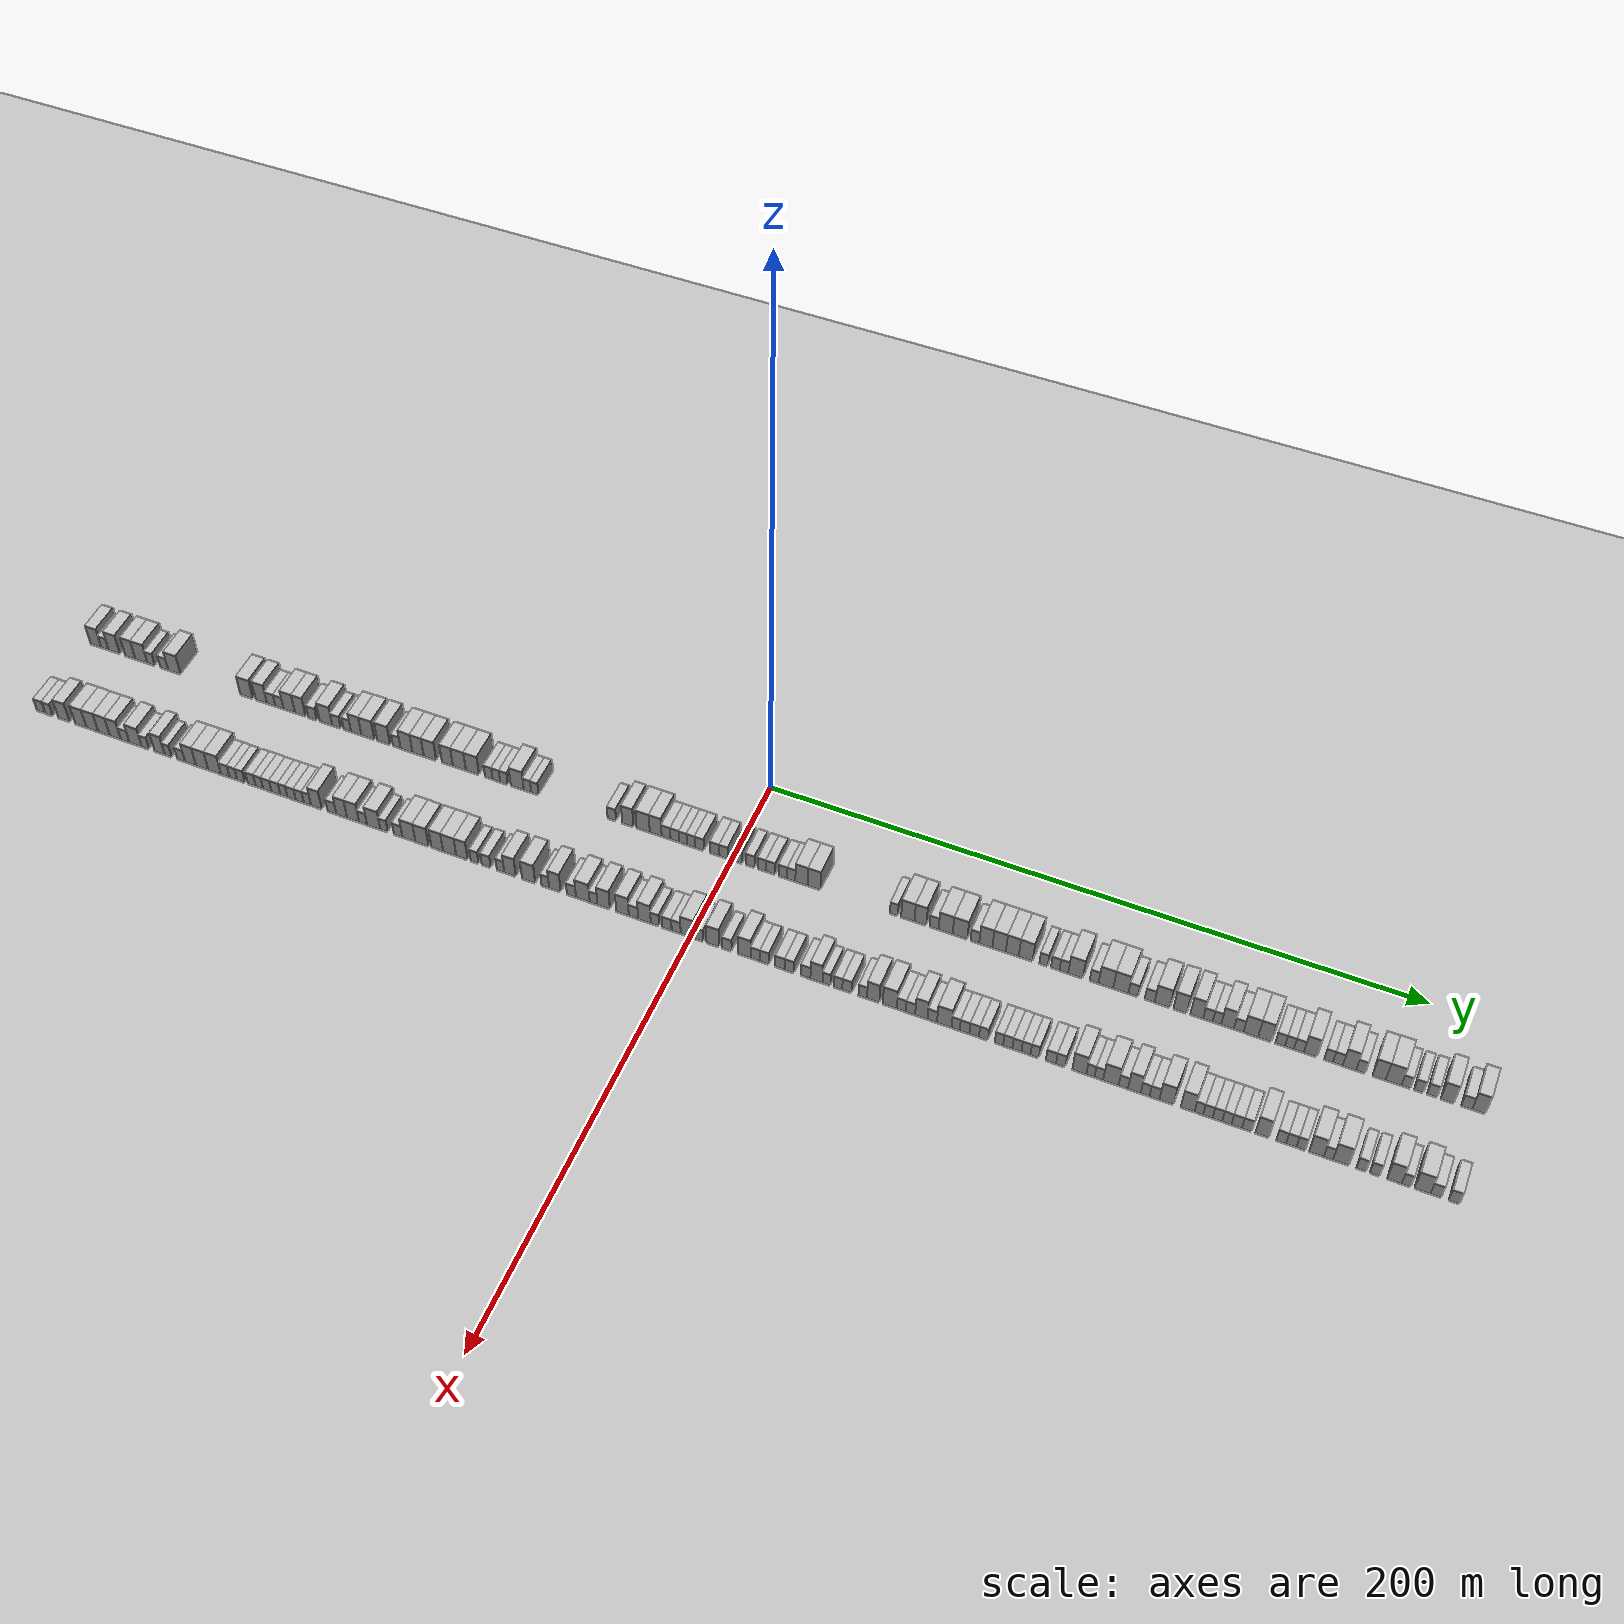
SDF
<?xml version="1.0" encoding="utf-8"?>

<sdf version="1.6">

   <world name="default">

      <gui fullscreen="0">

         <camera name="user_camera">

            <pose>-15 0 4.57585 0 0 0</pose>

            <view_controller>orbit</view_controller>

         </camera>

      </gui>

      <scene>

         <sky>

           <clouds>

             <speed>12</speed>

           </clouds>

         </sky>

         <ambient>0.4 0.4 0.4 1</ambient>

         <background>0.7 0.7 0.7 1</background>

         <shadows>1</shadows>

      </scene>

      <gravity>0 0 -9.8066</gravity>

      <magnetic_field>6e-06 2.3e-05 -4.2e-05</magnetic_field>

      <physics default="0" name="default_physics" type="ode">

         <ode>

            <solver>

               <type>quick</type>

               <iters>10</iters>

               <sor>1.0</sor>

               <use_dynamic_moi_rescaling>0</use_dynamic_moi_rescaling>

            </solver>

            <constraints>

               <cfm>0</cfm>

               <erp>0.2</erp>

               <contact_max_correcting_vel>100</contact_max_correcting_vel>

               <contact_surface_layer>0.001</contact_surface_layer>

            </constraints>

         </ode>

         <max_step_size>0.004</max_step_size>

         <real_time_factor>1</real_time_factor>

         <real_time_update_rate>250</real_time_update_rate>

      </physics>

      <light name="sun" type="directional">

         <cast_shadows>1</cast_shadows>

         <pose>0 0 10 0 0 0</pose>

         <diffuse>0.8 0.8 0.8 1</diffuse>

         <specular>0.2 0.2 0.2 1</specular>

         <attenuation>

            <range>1000</range>

            <constant>0.9</constant>

            <linear>0.01</linear>

            <quadratic>0.001</quadratic>

         </attenuation>

         <direction>-0.5 0.1 -0.9</direction>

      </light>

      <include>

         <name>ground_plane_1</name>

         <uri>model://HANNAS_ground_plane</uri>

         <pose>0 0 0  0 0 0</pose>

      </include>

      <include>

         <name>ground_plane_2</name>

         <uri>model://HANNAS_ground_plane</uri>

         <pose>100 0 0  0 0 0</pose>

      </include>

      <model name="building_1">

         <static>1</static>

         <pose frame="">25.0000 -218.0237 0 0.000000 0.000000 0.000000</pose>

         <link name="link">

            <pose frame="">0 0 4.50 0 0 0</pose>

            <collision name="collision">

               <geometry>

                  <box>

                     <size>10.0000 3.9525 9.0000</size>

                  </box>

               </geometry>

               <max_contacts>10</max_contacts>

               <surface>

                  <contact>

                     <ode/>

                  </contact>

                  <bounce/>

                  <friction>

                     <torsional>

                        <ode/>

                     </torsional>

                     <ode/>

                  </friction>

               </surface>

            </collision>

            <visual name="visual">

               <cast_shadows>0</cast_shadows>

               <geometry>

                  <box>

                     <size>10.0000 3.9525 9.0000</size>

                  </box>

               </geometry>

               <material>

                  <script>

                     <uri>model://HANNAS_wall/materials/scripts</uri>

                     <uri>model://HANNAS_wall/materials/textures</uri>

                     <name>vrc/HANNAS_wall</name>

                  </script>

               </material>

            </visual>

            <self_collide>0</self_collide>

            <enable_wind>0</enable_wind>

            <kinematic>0</kinematic>

         </link>

      </model>

      <model name="building_2">

         <static>1</static>

         <pose frame="">25.0000 -214.7297 0 0.000000 0.000000 0.000000</pose>

         <link name="link">

            <pose frame="">0 0 3.00 0 0 0</pose>

            <collision name="collision">

               <geometry>

                  <box>

                     <size>10.0000 2.6356 6.0000</size>

                  </box>

               </geometry>

               <max_contacts>10</max_contacts>

               <surface>

                  <contact>

                     <ode/>

                  </contact>

                  <bounce/>

                  <friction>

                     <torsional>

                        <ode/>

                     </torsional>

                     <ode/>

                  </friction>

               </surface>

            </collision>

            <visual name="visual">

               <cast_shadows>0</cast_shadows>

               <geometry>

                  <box>

                     <size>10.0000 2.6356 6.0000</size>

                  </box>

               </geometry>

               <material>

                  <script>

                     <uri>model://HANNAS_wall/materials/scripts</uri>

                     <uri>model://HANNAS_wall/materials/textures</uri>

                     <name>vrc/HANNAS_wall</name>

                  </script>

               </material>

            </visual>

            <self_collide>0</self_collide>

            <enable_wind>0</enable_wind>

            <kinematic>0</kinematic>

         </link>

      </model>

      <model name="building_3">

         <static>1</static>

         <pose frame="">25.0000 -211.3211 0 0.000000 0.000000 0.000000</pose>

         <link name="link">

            <pose frame="">0 0 4.50 0 0 0</pose>

            <collision name="collision">

               <geometry>

                  <box>

                     <size>10.0000 4.1815 9.0000</size>

                  </box>

               </geometry>

               <max_contacts>10</max_contacts>

               <surface>

                  <contact>

                     <ode/>

                  </contact>

                  <bounce/>

                  <friction>

                     <torsional>

                        <ode/>

                     </torsional>

                     <ode/>

                  </friction>

               </surface>

            </collision>

            <visual name="visual">

               <cast_shadows>0</cast_shadows>

               <geometry>

                  <box>

                     <size>10.0000 4.1815 9.0000</size>

                  </box>

               </geometry>

               <material>

                  <script>

                     <uri>model://HANNAS_wall/materials/scripts</uri>

                     <uri>model://HANNAS_wall/materials/textures</uri>

                     <name>vrc/HANNAS_wall</name>

                  </script>

               </material>

            </visual>

            <self_collide>0</self_collide>

            <enable_wind>0</enable_wind>

            <kinematic>0</kinematic>

         </link>

      </model>

      <model name="building_4">

         <static>1</static>

         <pose frame="">25.0000 -205.3935 0 0.000000 0.000000 0.000000</pose>

         <link name="link">

            <pose frame="">0 0 4.50 0 0 0</pose>

            <collision name="collision">

               <geometry>

                  <box>

                     <size>10.0000 3.6737 9.0000</size>

                  </box>

               </geometry>

               <max_contacts>10</max_contacts>

               <surface>

                  <contact>

                     <ode/>

                  </contact>

                  <bounce/>

                  <friction>

                     <torsional>

                        <ode/>

                     </torsional>

                     <ode/>

                  </friction>

               </surface>

            </collision>

            <visual name="visual">

               <cast_shadows>0</cast_shadows>

               <geometry>

                  <box>

                     <size>10.0000 3.6737 9.0000</size>

                  </box>

               </geometry>

               <material>

                  <script>

                     <uri>model://HANNAS_wall/materials/scripts</uri>

                     <uri>model://HANNAS_wall/materials/textures</uri>

                     <name>vrc/HANNAS_wall</name>

                  </script>

               </material>

            </visual>

            <self_collide>0</self_collide>

            <enable_wind>0</enable_wind>

            <kinematic>0</kinematic>

         </link>

      </model>

      <model name="building_5">

         <static>1</static>

         <pose frame="">25.0000 -201.3614 0 0.000000 0.000000 0.000000</pose>

         <link name="link">

            <pose frame="">0 0 4.50 0 0 0</pose>

            <collision name="collision">

               <geometry>

                  <box>

                     <size>10.0000 4.3906 9.0000</size>

                  </box>

               </geometry>

               <max_contacts>10</max_contacts>

               <surface>

                  <contact>

                     <ode/>

                  </contact>

                  <bounce/>

                  <friction>

                     <torsional>

                        <ode/>

                     </torsional>

                     <ode/>

                  </friction>

               </surface>

            </collision>

            <visual name="visual">

               <cast_shadows>0</cast_shadows>

               <geometry>

                  <box>

                     <size>10.0000 4.3906 9.0000</size>

                  </box>

               </geometry>

               <material>

                  <script>

                     <uri>model://HANNAS_wall/materials/scripts</uri>

                     <uri>model://HANNAS_wall/materials/textures</uri>

                     <name>vrc/HANNAS_wall</name>

                  </script>

               </material>

            </visual>

            <self_collide>0</self_collide>

            <enable_wind>0</enable_wind>

            <kinematic>0</kinematic>

         </link>

      </model>

      <model name="building_6">

         <static>1</static>

         <pose frame="">25.0000 -197.8209 0 0.000000 0.000000 0.000000</pose>

         <link name="link">

            <pose frame="">0 0 3.00 0 0 0</pose>

            <collision name="collision">

               <geometry>

                  <box>

                     <size>10.0000 2.6903 6.0000</size>

                  </box>

               </geometry>

               <max_contacts>10</max_contacts>

               <surface>

                  <contact>

                     <ode/>

                  </contact>

                  <bounce/>

                  <friction>

                     <torsional>

                        <ode/>

                     </torsional>

                     <ode/>

                  </friction>

               </surface>

            </collision>

            <visual name="visual">

               <cast_shadows>0</cast_shadows>

               <geometry>

                  <box>

                     <size>10.0000 2.6903 6.0000</size>

                  </box>

               </geometry>

               <material>

                  <script>

                     <uri>model://HANNAS_wall/materials/scripts</uri>

                     <uri>model://HANNAS_wall/materials/textures</uri>

                     <name>vrc/HANNAS_wall</name>

                  </script>

               </material>

            </visual>

            <self_collide>0</self_collide>

            <enable_wind>0</enable_wind>

            <kinematic>0</kinematic>

         </link>

      </model>

      <model name="building_7">

         <static>1</static>

         <pose frame="">25.0000 -193.0560 0 0.000000 0.000000 0.000000</pose>

         <link name="link">

            <pose frame="">0 0 3.00 0 0 0</pose>

            <collision name="collision">

               <geometry>

                  <box>

                     <size>10.0000 2.8395 6.0000</size>

                  </box>

               </geometry>

               <max_contacts>10</max_contacts>

               <surface>

                  <contact>

                     <ode/>

                  </contact>

                  <bounce/>

                  <friction>

                     <torsional>

                        <ode/>

                     </torsional>

                     <ode/>

                  </friction>

               </surface>

            </collision>

            <visual name="visual">

               <cast_shadows>0</cast_shadows>

               <geometry>

                  <box>

                     <size>10.0000 2.8395 6.0000</size>

                  </box>

               </geometry>

               <material>

                  <script>

                     <uri>model://HANNAS_wall/materials/scripts</uri>

                     <uri>model://HANNAS_wall/materials/textures</uri>

                     <name>vrc/HANNAS_wall</name>

                  </script>

               </material>

            </visual>

            <self_collide>0</self_collide>

            <enable_wind>0</enable_wind>

            <kinematic>0</kinematic>

         </link>

      </model>

      <model name="building_8">

         <static>1</static>

         <pose frame="">25.0000 -189.3936 0 0.000000 0.000000 0.000000</pose>

         <link name="link">

            <pose frame="">0 0 4.50 0 0 0</pose>

            <collision name="collision">

               <geometry>

                  <box>

                     <size>10.0000 4.4855 9.0000</size>

                  </box>

               </geometry>

               <max_contacts>10</max_contacts>

               <surface>

                  <contact>

                     <ode/>

                  </contact>

                  <bounce/>

                  <friction>

                     <torsional>

                        <ode/>

                     </torsional>

                     <ode/>

                  </friction>

               </surface>

            </collision>

            <visual name="visual">

               <cast_shadows>0</cast_shadows>

               <geometry>

                  <box>

                     <size>10.0000 4.4855 9.0000</size>

                  </box>

               </geometry>

               <material>

                  <script>

                     <uri>model://HANNAS_wall/materials/scripts</uri>

                     <uri>model://HANNAS_wall/materials/textures</uri>

                     <name>vrc/HANNAS_wall</name>

                  </script>

               </material>

            </visual>

            <self_collide>0</self_collide>

            <enable_wind>0</enable_wind>

            <kinematic>0</kinematic>

         </link>

      </model>

      <model name="building_9">

         <static>1</static>

         <pose frame="">25.0000 -163.4906 0 0.000000 0.000000 0.000000</pose>

         <link name="link">

            <pose frame="">0 0 4.50 0 0 0</pose>

            <collision name="collision">

               <geometry>

                  <box>

                     <size>10.0000 4.4402 9.0000</size>

                  </box>

               </geometry>

               <max_contacts>10</max_contacts>

               <surface>

                  <contact>

                     <ode/>

                  </contact>

                  <bounce/>

                  <friction>

                     <torsional>

                        <ode/>

                     </torsional>

                     <ode/>

                  </friction>

               </surface>

            </collision>

            <visual name="visual">

               <cast_shadows>0</cast_shadows>

               <geometry>

                  <box>

                     <size>10.0000 4.4402 9.0000</size>

                  </box>

               </geometry>

               <material>

                  <script>

                     <uri>model://HANNAS_wall/materials/scripts</uri>

                     <uri>model://HANNAS_wall/materials/textures</uri>

                     <name>vrc/HANNAS_wall</name>

                  </script>

               </material>

            </visual>

            <self_collide>0</self_collide>

            <enable_wind>0</enable_wind>

            <kinematic>0</kinematic>

         </link>

      </model>

      <model name="building_10">

         <static>1</static>

         <pose frame="">25.0000 -158.2627 0 0.000000 0.000000 0.000000</pose>

         <link name="link">

            <pose frame="">0 0 4.50 0 0 0</pose>

            <collision name="collision">

               <geometry>

                  <box>

                     <size>10.0000 4.0157 9.0000</size>

                  </box>

               </geometry>

               <max_contacts>10</max_contacts>

               <surface>

                  <contact>

                     <ode/>

                  </contact>

                  <bounce/>

                  <friction>

                     <torsional>

                        <ode/>

                     </torsional>

                     <ode/>

                  </friction>

               </surface>

            </collision>

            <visual name="visual">

               <cast_shadows>0</cast_shadows>

               <geometry>

                  <box>

                     <size>10.0000 4.0157 9.0000</size>

                  </box>

               </geometry>

               <material>

                  <script>

                     <uri>model://HANNAS_wall/materials/scripts</uri>

                     <uri>model://HANNAS_wall/materials/textures</uri>

                     <name>vrc/HANNAS_wall</name>

                  </script>

               </material>

            </visual>

            <self_collide>0</self_collide>

            <enable_wind>0</enable_wind>

            <kinematic>0</kinematic>

         </link>

      </model>

      <model name="building_11">

         <static>1</static>

         <pose frame="">25.0000 -154.7772 0 0.000000 0.000000 0.000000</pose>

         <link name="link">

            <pose frame="">0 0 3.00 0 0 0</pose>

            <collision name="collision">

               <geometry>

                  <box>

                     <size>10.0000 2.9553 6.0000</size>

                  </box>

               </geometry>

               <max_contacts>10</max_contacts>

               <surface>

                  <contact>

                     <ode/>

                  </contact>

                  <bounce/>

                  <friction>

                     <torsional>

                        <ode/>

                     </torsional>

                     <ode/>

                  </friction>

               </surface>

            </collision>

            <visual name="visual">

               <cast_shadows>0</cast_shadows>

               <geometry>

                  <box>

                     <size>10.0000 2.9553 6.0000</size>

                  </box>

               </geometry>

               <material>

                  <script>

                     <uri>model://HANNAS_wall/materials/scripts</uri>

                     <uri>model://HANNAS_wall/materials/textures</uri>

                     <name>vrc/HANNAS_wall</name>

                  </script>

               </material>

            </visual>

            <self_collide>0</self_collide>

            <enable_wind>0</enable_wind>

            <kinematic>0</kinematic>

         </link>

      </model>

      <model name="building_12">

         <static>1</static>

         <pose frame="">25.0000 -151.8430 0 0.000000 0.000000 0.000000</pose>

         <link name="link">

            <pose frame="">0 0 3.00 0 0 0</pose>

            <collision name="collision">

               <geometry>

                  <box>

                     <size>10.0000 2.9130 6.0000</size>

                  </box>

               </geometry>

               <max_contacts>10</max_contacts>

               <surface>

                  <contact>

                     <ode/>

                  </contact>

                  <bounce/>

                  <friction>

                     <torsional>

                        <ode/>

                     </torsional>

                     <ode/>

                  </friction>

               </surface>

            </collision>

            <visual name="visual">

               <cast_shadows>0</cast_shadows>

               <geometry>

                  <box>

                     <size>10.0000 2.9130 6.0000</size>

                  </box>

               </geometry>

               <material>

                  <script>

                     <uri>model://HANNAS_wall/materials/scripts</uri>

                     <uri>model://HANNAS_wall/materials/textures</uri>

                     <name>vrc/HANNAS_wall</name>

                  </script>

               </material>

            </visual>

            <self_collide>0</self_collide>

            <enable_wind>0</enable_wind>

            <kinematic>0</kinematic>

         </link>

      </model>

      <model name="building_13">

         <static>1</static>

         <pose frame="">25.0000 -148.3848 0 0.000000 0.000000 0.000000</pose>

         <link name="link">

            <pose frame="">0 0 4.50 0 0 0</pose>

            <collision name="collision">

               <geometry>

                  <box>

                     <size>10.0000 4.0035 9.0000</size>

                  </box>

               </geometry>

               <max_contacts>10</max_contacts>

               <surface>

                  <contact>

                     <ode/>

                  </contact>

                  <bounce/>

                  <friction>

                     <torsional>

                        <ode/>

                     </torsional>

                     <ode/>

                  </friction>

               </surface>

            </collision>

            <visual name="visual">

               <cast_shadows>0</cast_shadows>

               <geometry>

                  <box>

                     <size>10.0000 4.0035 9.0000</size>

                  </box>

               </geometry>

               <material>

                  <script>

                     <uri>model://HANNAS_wall/materials/scripts</uri>

                     <uri>model://HANNAS_wall/materials/textures</uri>

                     <name>vrc/HANNAS_wall</name>

                  </script>

               </material>

            </visual>

            <self_collide>0</self_collide>

            <enable_wind>0</enable_wind>

            <kinematic>0</kinematic>

         </link>

      </model>

      <model name="building_14">

         <static>1</static>

         <pose frame="">25.0000 -144.5421 0 0.000000 0.000000 0.000000</pose>

         <link name="link">

            <pose frame="">0 0 4.50 0 0 0</pose>

            <collision name="collision">

               <geometry>

                  <box>

                     <size>10.0000 3.6819 9.0000</size>

                  </box>

               </geometry>

               <max_contacts>10</max_contacts>

               <surface>

                  <contact>

                     <ode/>

                  </contact>

                  <bounce/>

                  <friction>

                     <torsional>

                        <ode/>

                     </torsional>

                     <ode/>

                  </friction>

               </surface>

            </collision>

            <visual name="visual">

               <cast_shadows>0</cast_shadows>

               <geometry>

                  <box>

                     <size>10.0000 3.6819 9.0000</size>

                  </box>

               </geometry>

               <material>

                  <script>

                     <uri>model://HANNAS_wall/materials/scripts</uri>

                     <uri>model://HANNAS_wall/materials/textures</uri>

                     <name>vrc/HANNAS_wall</name>

                  </script>

               </material>

            </visual>

            <self_collide>0</self_collide>

            <enable_wind>0</enable_wind>

            <kinematic>0</kinematic>

         </link>

      </model>

      <model name="building_15">

         <static>1</static>

         <pose frame="">25.0000 -140.2156 0 0.000000 0.000000 0.000000</pose>

         <link name="link">

            <pose frame="">0 0 3.00 0 0 0</pose>

            <collision name="collision">

               <geometry>

                  <box>

                     <size>10.0000 2.9711 6.0000</size>

                  </box>

               </geometry>

               <max_contacts>10</max_contacts>

               <surface>

                  <contact>

                     <ode/>

                  </contact>

                  <bounce/>

                  <friction>

                     <torsional>

                        <ode/>

                     </torsional>

                     <ode/>

                  </friction>

               </surface>

            </collision>

            <visual name="visual">

               <cast_shadows>0</cast_shadows>

               <geometry>

                  <box>

                     <size>10.0000 2.9711 6.0000</size>

                  </box>

               </geometry>

               <material>

                  <script>

                     <uri>model://HANNAS_wall/materials/scripts</uri>

                     <uri>model://HANNAS_wall/materials/textures</uri>

                     <name>vrc/HANNAS_wall</name>

                  </script>

               </material>

            </visual>

            <self_collide>0</self_collide>

            <enable_wind>0</enable_wind>

            <kinematic>0</kinematic>

         </link>

      </model>

      <model name="building_16">

         <static>1</static>

         <pose frame="">25.0000 -135.5298 0 0.000000 0.000000 0.000000</pose>

         <link name="link">

            <pose frame="">0 0 4.50 0 0 0</pose>

            <collision name="collision">

               <geometry>

                  <box>

                     <size>10.0000 4.4004 9.0000</size>

                  </box>

               </geometry>

               <max_contacts>10</max_contacts>

               <surface>

                  <contact>

                     <ode/>

                  </contact>

                  <bounce/>

                  <friction>

                     <torsional>

                        <ode/>

                     </torsional>

                     <ode/>

                  </friction>

               </surface>

            </collision>

            <visual name="visual">

               <cast_shadows>0</cast_shadows>

               <geometry>

                  <box>

                     <size>10.0000 4.4004 9.0000</size>

                  </box>

               </geometry>

               <material>

                  <script>

                     <uri>model://HANNAS_wall/materials/scripts</uri>

                     <uri>model://HANNAS_wall/materials/textures</uri>

                     <name>vrc/HANNAS_wall</name>

                  </script>

               </material>

            </visual>

            <self_collide>0</self_collide>

            <enable_wind>0</enable_wind>

            <kinematic>0</kinematic>

         </link>

      </model>

      <model name="building_17">

         <static>1</static>

         <pose frame="">25.0000 -131.8402 0 0.000000 0.000000 0.000000</pose>

         <link name="link">

            <pose frame="">0 0 3.00 0 0 0</pose>

            <collision name="collision">

               <geometry>

                  <box>

                     <size>10.0000 2.9789 6.0000</size>

                  </box>

               </geometry>

               <max_contacts>10</max_contacts>

               <surface>

                  <contact>

                     <ode/>

                  </contact>

                  <bounce/>

                  <friction>

                     <torsional>

                        <ode/>

                     </torsional>

                     <ode/>

                  </friction>

               </surface>

            </collision>

            <visual name="visual">

               <cast_shadows>0</cast_shadows>

               <geometry>

                  <box>

                     <size>10.0000 2.9789 6.0000</size>

                  </box>

               </geometry>

               <material>

                  <script>

                     <uri>model://HANNAS_wall/materials/scripts</uri>

                     <uri>model://HANNAS_wall/materials/textures</uri>

                     <name>vrc/HANNAS_wall</name>

                  </script>

               </material>

            </visual>

            <self_collide>0</self_collide>

            <enable_wind>0</enable_wind>

            <kinematic>0</kinematic>

         </link>

      </model>

      <model name="building_18">

         <static>1</static>

         <pose frame="">25.0000 -128.0806 0 0.000000 0.000000 0.000000</pose>

         <link name="link">

            <pose frame="">0 0 3.00 0 0 0</pose>

            <collision name="collision">

               <geometry>

                  <box>

                     <size>10.0000 2.5402 6.0000</size>

                  </box>

               </geometry>

               <max_contacts>10</max_contacts>

               <surface>

                  <contact>

                     <ode/>

                  </contact>

                  <bounce/>

                  <friction>

                     <torsional>

                        <ode/>

                     </torsional>

                     <ode/>

                  </friction>

               </surface>

            </collision>

            <visual name="visual">

               <cast_shadows>0</cast_shadows>

               <geometry>

                  <box>

                     <size>10.0000 2.5402 6.0000</size>

                  </box>

               </geometry>

               <material>

                  <script>

                     <uri>model://HANNAS_wall/materials/scripts</uri>

                     <uri>model://HANNAS_wall/materials/textures</uri>

                     <name>vrc/HANNAS_wall</name>

                  </script>

               </material>

            </visual>

            <self_collide>0</self_collide>

            <enable_wind>0</enable_wind>

            <kinematic>0</kinematic>

         </link>

      </model>

      <model name="building_19">

         <static>1</static>

         <pose frame="">25.0000 -125.0010 0 0.000000 0.000000 0.000000</pose>

         <link name="link">

            <pose frame="">0 0 4.50 0 0 0</pose>

            <collision name="collision">

               <geometry>

                  <box>

                     <size>10.0000 3.6189 9.0000</size>

                  </box>

               </geometry>

               <max_contacts>10</max_contacts>

               <surface>

                  <contact>

                     <ode/>

                  </contact>

                  <bounce/>

                  <friction>

                     <torsional>

                        <ode/>

                     </torsional>

                     <ode/>

                  </friction>

               </surface>

            </collision>

            <visual name="visual">

               <cast_shadows>0</cast_shadows>

               <geometry>

                  <box>

                     <size>10.0000 3.6189 9.0000</size>

                  </box>

               </geometry>

               <material>

                  <script>

                     <uri>model://HANNAS_wall/materials/scripts</uri>

                     <uri>model://HANNAS_wall/materials/textures</uri>

                     <name>vrc/HANNAS_wall</name>

                  </script>

               </material>

            </visual>

            <self_collide>0</self_collide>

            <enable_wind>0</enable_wind>

            <kinematic>0</kinematic>

         </link>

      </model>

      <model name="building_20">

         <static>1</static>

         <pose frame="">25.0000 -120.9565 0 0.000000 0.000000 0.000000</pose>

         <link name="link">

            <pose frame="">0 0 4.50 0 0 0</pose>

            <collision name="collision">

               <geometry>

                  <box>

                     <size>10.0000 4.4701 9.0000</size>

                  </box>

               </geometry>

               <max_contacts>10</max_contacts>

               <surface>

                  <contact>

                     <ode/>

                  </contact>

                  <bounce/>

                  <friction>

                     <torsional>

                        <ode/>

                     </torsional>

                     <ode/>

                  </friction>

               </surface>

            </collision>

            <visual name="visual">

               <cast_shadows>0</cast_shadows>

               <geometry>

                  <box>

                     <size>10.0000 4.4701 9.0000</size>

                  </box>

               </geometry>

               <material>

                  <script>

                     <uri>model://HANNAS_wall/materials/scripts</uri>

                     <uri>model://HANNAS_wall/materials/textures</uri>

                     <name>vrc/HANNAS_wall</name>

                  </script>

               </material>

            </visual>

            <self_collide>0</self_collide>

            <enable_wind>0</enable_wind>

            <kinematic>0</kinematic>

         </link>

      </model>

      <model name="building_21">

         <static>1</static>

         <pose frame="">25.0000 -115.5185 0 0.000000 0.000000 0.000000</pose>

         <link name="link">

            <pose frame="">0 0 4.50 0 0 0</pose>

            <collision name="collision">

               <geometry>

                  <box>

                     <size>10.0000 4.4060 9.0000</size>

                  </box>

               </geometry>

               <max_contacts>10</max_contacts>

               <surface>

                  <contact>

                     <ode/>

                  </contact>

                  <bounce/>

                  <friction>

                     <torsional>

                        <ode/>

                     </torsional>

                     <ode/>

                  </friction>

               </surface>

            </collision>

            <visual name="visual">

               <cast_shadows>0</cast_shadows>

               <geometry>

                  <box>

                     <size>10.0000 4.4060 9.0000</size>

                  </box>

               </geometry>

               <material>

                  <script>

                     <uri>model://HANNAS_wall/materials/scripts</uri>

                     <uri>model://HANNAS_wall/materials/textures</uri>

                     <name>vrc/HANNAS_wall</name>

                  </script>

               </material>

            </visual>

            <self_collide>0</self_collide>

            <enable_wind>0</enable_wind>

            <kinematic>0</kinematic>

         </link>

      </model>

      <model name="building_22">

         <static>1</static>

         <pose frame="">25.0000 -111.0188 0 0.000000 0.000000 0.000000</pose>

         <link name="link">

            <pose frame="">0 0 3.00 0 0 0</pose>

            <collision name="collision">

               <geometry>

                  <box>

                     <size>10.0000 2.5934 6.0000</size>

                  </box>

               </geometry>

               <max_contacts>10</max_contacts>

               <surface>

                  <contact>

                     <ode/>

                  </contact>

                  <bounce/>

                  <friction>

                     <torsional>

                        <ode/>

                     </torsional>

                     <ode/>

                  </friction>

               </surface>

            </collision>

            <visual name="visual">

               <cast_shadows>0</cast_shadows>

               <geometry>

                  <box>

                     <size>10.0000 2.5934 6.0000</size>

                  </box>

               </geometry>

               <material>

                  <script>

                     <uri>model://HANNAS_wall/materials/scripts</uri>

                     <uri>model://HANNAS_wall/materials/textures</uri>

                     <name>vrc/HANNAS_wall</name>

                  </script>

               </material>

            </visual>

            <self_collide>0</self_collide>

            <enable_wind>0</enable_wind>

            <kinematic>0</kinematic>

         </link>

      </model>

      <model name="building_23">

         <static>1</static>

         <pose frame="">25.0000 -107.6772 0 0.000000 0.000000 0.000000</pose>

         <link name="link">

            <pose frame="">0 0 4.50 0 0 0</pose>

            <collision name="collision">

               <geometry>

                  <box>

                     <size>10.0000 4.0898 9.0000</size>

                  </box>

               </geometry>

               <max_contacts>10</max_contacts>

               <surface>

                  <contact>

                     <ode/>

                  </contact>

                  <bounce/>

                  <friction>

                     <torsional>

                        <ode/>

                     </torsional>

                     <ode/>

                  </friction>

               </surface>

            </collision>

            <visual name="visual">

               <cast_shadows>0</cast_shadows>

               <geometry>

                  <box>

                     <size>10.0000 4.0898 9.0000</size>

                  </box>

               </geometry>

               <material>

                  <script>

                     <uri>model://HANNAS_wall/materials/scripts</uri>

                     <uri>model://HANNAS_wall/materials/textures</uri>

                     <name>vrc/HANNAS_wall</name>

                  </script>

               </material>

            </visual>

            <self_collide>0</self_collide>

            <enable_wind>0</enable_wind>

            <kinematic>0</kinematic>

         </link>

      </model>

      <model name="building_24">

         <static>1</static>

         <pose frame="">25.0000 -103.7062 0 0.000000 0.000000 0.000000</pose>

         <link name="link">

            <pose frame="">0 0 4.50 0 0 0</pose>

            <collision name="collision">

               <geometry>

                  <box>

                     <size>10.0000 3.8522 9.0000</size>

                  </box>

               </geometry>

               <max_contacts>10</max_contacts>

               <surface>

                  <contact>

                     <ode/>

                  </contact>

                  <bounce/>

                  <friction>

                     <torsional>

                        <ode/>

                     </torsional>

                     <ode/>

                  </friction>

               </surface>

            </collision>

            <visual name="visual">

               <cast_shadows>0</cast_shadows>

               <geometry>

                  <box>

                     <size>10.0000 3.8522 9.0000</size>

                  </box>

               </geometry>

               <material>

                  <script>

                     <uri>model://HANNAS_wall/materials/scripts</uri>

                     <uri>model://HANNAS_wall/materials/textures</uri>

                     <name>vrc/HANNAS_wall</name>

                  </script>

               </material>

            </visual>

            <self_collide>0</self_collide>

            <enable_wind>0</enable_wind>

            <kinematic>0</kinematic>

         </link>

      </model>

      <model name="building_25">

         <static>1</static>

         <pose frame="">25.0000 -99.6656 0 0.000000 0.000000 0.000000</pose>

         <link name="link">

            <pose frame="">0 0 4.50 0 0 0</pose>

            <collision name="collision">

               <geometry>

                  <box>

                     <size>10.0000 4.2291 9.0000</size>

                  </box>

               </geometry>

               <max_contacts>10</max_contacts>

               <surface>

                  <contact>

                     <ode/>

                  </contact>

                  <bounce/>

                  <friction>

                     <torsional>

                        <ode/>

                     </torsional>

                     <ode/>

                  </friction>

               </surface>

            </collision>

            <visual name="visual">

               <cast_shadows>0</cast_shadows>

               <geometry>

                  <box>

                     <size>10.0000 4.2291 9.0000</size>

                  </box>

               </geometry>

               <material>

                  <script>

                     <uri>model://HANNAS_wall/materials/scripts</uri>

                     <uri>model://HANNAS_wall/materials/textures</uri>

                     <name>vrc/HANNAS_wall</name>

                  </script>

               </material>

            </visual>

            <self_collide>0</self_collide>

            <enable_wind>0</enable_wind>

            <kinematic>0</kinematic>

         </link>

      </model>

      <model name="building_26">

         <static>1</static>

         <pose frame="">25.0000 -93.7013 0 0.000000 0.000000 0.000000</pose>

         <link name="link">

            <pose frame="">0 0 4.50 0 0 0</pose>

            <collision name="collision">

               <geometry>

                  <box>

                     <size>10.0000 3.6995 9.0000</size>

                  </box>

               </geometry>

               <max_contacts>10</max_contacts>

               <surface>

                  <contact>

                     <ode/>

                  </contact>

                  <bounce/>

                  <friction>

                     <torsional>

                        <ode/>

                     </torsional>

                     <ode/>

                  </friction>

               </surface>

            </collision>

            <visual name="visual">

               <cast_shadows>0</cast_shadows>

               <geometry>

                  <box>

                     <size>10.0000 3.6995 9.0000</size>

                  </box>

               </geometry>

               <material>

                  <script>

                     <uri>model://HANNAS_wall/materials/scripts</uri>

                     <uri>model://HANNAS_wall/materials/textures</uri>

                     <name>vrc/HANNAS_wall</name>

                  </script>

               </material>

            </visual>

            <self_collide>0</self_collide>

            <enable_wind>0</enable_wind>

            <kinematic>0</kinematic>

         </link>

      </model>

      <model name="building_27">

         <static>1</static>

         <pose frame="">25.0000 -89.6552 0 0.000000 0.000000 0.000000</pose>

         <link name="link">

            <pose frame="">0 0 4.50 0 0 0</pose>

            <collision name="collision">

               <geometry>

                  <box>

                     <size>10.0000 4.3927 9.0000</size>

                  </box>

               </geometry>

               <max_contacts>10</max_contacts>

               <surface>

                  <contact>

                     <ode/>

                  </contact>

                  <bounce/>

                  <friction>

                     <torsional>

                        <ode/>

                     </torsional>

                     <ode/>

                  </friction>

               </surface>

            </collision>

            <visual name="visual">

               <cast_shadows>0</cast_shadows>

               <geometry>

                  <box>

                     <size>10.0000 4.3927 9.0000</size>

                  </box>

               </geometry>

               <material>

                  <script>

                     <uri>model://HANNAS_wall/materials/scripts</uri>

                     <uri>model://HANNAS_wall/materials/textures</uri>

                     <name>vrc/HANNAS_wall</name>

                  </script>

               </material>

            </visual>

            <self_collide>0</self_collide>

            <enable_wind>0</enable_wind>

            <kinematic>0</kinematic>

         </link>

      </model>

      <model name="building_28">

         <static>1</static>

         <pose frame="">25.0000 -85.2483 0 0.000000 0.000000 0.000000</pose>

         <link name="link">

            <pose frame="">0 0 4.50 0 0 0</pose>

            <collision name="collision">

               <geometry>

                  <box>

                     <size>10.0000 4.4211 9.0000</size>

                  </box>

               </geometry>

               <max_contacts>10</max_contacts>

               <surface>

                  <contact>

                     <ode/>

                  </contact>

                  <bounce/>

                  <friction>

                     <torsional>

                        <ode/>

                     </torsional>

                     <ode/>

                  </friction>

               </surface>

            </collision>

            <visual name="visual">

               <cast_shadows>0</cast_shadows>

               <geometry>

                  <box>

                     <size>10.0000 4.4211 9.0000</size>

                  </box>

               </geometry>

               <material>

                  <script>

                     <uri>model://HANNAS_wall/materials/scripts</uri>

                     <uri>model://HANNAS_wall/materials/textures</uri>

                     <name>vrc/HANNAS_wall</name>

                  </script>

               </material>

            </visual>

            <self_collide>0</self_collide>

            <enable_wind>0</enable_wind>

            <kinematic>0</kinematic>

         </link>

      </model>

      <model name="building_29">

         <static>1</static>

         <pose frame="">25.0000 -79.7500 0 0.000000 0.000000 0.000000</pose>

         <link name="link">

            <pose frame="">0 0 3.00 0 0 0</pose>

            <collision name="collision">

               <geometry>

                  <box>

                     <size>10.0000 2.5753 6.0000</size>

                  </box>

               </geometry>

               <max_contacts>10</max_contacts>

               <surface>

                  <contact>

                     <ode/>

                  </contact>

                  <bounce/>

                  <friction>

                     <torsional>

                        <ode/>

                     </torsional>

                     <ode/>

                  </friction>

               </surface>

            </collision>

            <visual name="visual">

               <cast_shadows>0</cast_shadows>

               <geometry>

                  <box>

                     <size>10.0000 2.5753 6.0000</size>

                  </box>

               </geometry>

               <material>

                  <script>

                     <uri>model://HANNAS_wall/materials/scripts</uri>

                     <uri>model://HANNAS_wall/materials/textures</uri>

                     <name>vrc/HANNAS_wall</name>

                  </script>

               </material>

            </visual>

            <self_collide>0</self_collide>

            <enable_wind>0</enable_wind>

            <kinematic>0</kinematic>

         </link>

      </model>

      <model name="building_30">

         <static>1</static>

         <pose frame="">25.0000 -77.1919 0 0.000000 0.000000 0.000000</pose>

         <link name="link">

            <pose frame="">0 0 3.00 0 0 0</pose>

            <collision name="collision">

               <geometry>

                  <box>

                     <size>10.0000 2.5410 6.0000</size>

                  </box>

               </geometry>

               <max_contacts>10</max_contacts>

               <surface>

                  <contact>

                     <ode/>

                  </contact>

                  <bounce/>

                  <friction>

                     <torsional>

                        <ode/>

                     </torsional>

                     <ode/>

                  </friction>

               </surface>

            </collision>

            <visual name="visual">

               <cast_shadows>0</cast_shadows>

               <geometry>

                  <box>

                     <size>10.0000 2.5410 6.0000</size>

                  </box>

               </geometry>

               <material>

                  <script>

                     <uri>model://HANNAS_wall/materials/scripts</uri>

                     <uri>model://HANNAS_wall/materials/textures</uri>

                     <name>vrc/HANNAS_wall</name>

                  </script>

               </material>

            </visual>

            <self_collide>0</self_collide>

            <enable_wind>0</enable_wind>

            <kinematic>0</kinematic>

         </link>

      </model>

      <model name="building_31">

         <static>1</static>

         <pose frame="">25.0000 -74.6405 0 0.000000 0.000000 0.000000</pose>

         <link name="link">

            <pose frame="">0 0 3.00 0 0 0</pose>

            <collision name="collision">

               <geometry>

                  <box>

                     <size>10.0000 2.5617 6.0000</size>

                  </box>

               </geometry>

               <max_contacts>10</max_contacts>

               <surface>

                  <contact>

                     <ode/>

                  </contact>

                  <bounce/>

                  <friction>

                     <torsional>

                        <ode/>

                     </torsional>

                     <ode/>

                  </friction>

               </surface>

            </collision>

            <visual name="visual">

               <cast_shadows>0</cast_shadows>

               <geometry>

                  <box>

                     <size>10.0000 2.5617 6.0000</size>

                  </box>

               </geometry>

               <material>

                  <script>

                     <uri>model://HANNAS_wall/materials/scripts</uri>

                     <uri>model://HANNAS_wall/materials/textures</uri>

                     <name>vrc/HANNAS_wall</name>

                  </script>

               </material>

            </visual>

            <self_collide>0</self_collide>

            <enable_wind>0</enable_wind>

            <kinematic>0</kinematic>

         </link>

      </model>

      <model name="building_32">

         <static>1</static>

         <pose frame="">25.0000 -70.1824 0 0.000000 0.000000 0.000000</pose>

         <link name="link">

            <pose frame="">0 0 4.50 0 0 0</pose>

            <collision name="collision">

               <geometry>

                  <box>

                     <size>10.0000 4.3544 9.0000</size>

                  </box>

               </geometry>

               <max_contacts>10</max_contacts>

               <surface>

                  <contact>

                     <ode/>

                  </contact>

                  <bounce/>

                  <friction>

                     <torsional>

                        <ode/>

                     </torsional>

                     <ode/>

                  </friction>

               </surface>

            </collision>

            <visual name="visual">

               <cast_shadows>0</cast_shadows>

               <geometry>

                  <box>

                     <size>10.0000 4.3544 9.0000</size>

                  </box>

               </geometry>

               <material>

                  <script>

                     <uri>model://HANNAS_wall/materials/scripts</uri>

                     <uri>model://HANNAS_wall/materials/textures</uri>

                     <name>vrc/HANNAS_wall</name>

                  </script>

               </material>

            </visual>

            <self_collide>0</self_collide>

            <enable_wind>0</enable_wind>

            <kinematic>0</kinematic>

         </link>

      </model>

      <model name="building_33">

         <static>1</static>

         <pose frame="">25.0000 -66.7747 0 0.000000 0.000000 0.000000</pose>

         <link name="link">

            <pose frame="">0 0 3.00 0 0 0</pose>

            <collision name="collision">

               <geometry>

                  <box>

                     <size>10.0000 2.4610 6.0000</size>

                  </box>

               </geometry>

               <max_contacts>10</max_contacts>

               <surface>

                  <contact>

                     <ode/>

                  </contact>

                  <bounce/>

                  <friction>

                     <torsional>

                        <ode/>

                     </torsional>

                     <ode/>

                  </friction>

               </surface>

            </collision>

            <visual name="visual">

               <cast_shadows>0</cast_shadows>

               <geometry>

                  <box>

                     <size>10.0000 2.4610 6.0000</size>

                  </box>

               </geometry>

               <material>

                  <script>

                     <uri>model://HANNAS_wall/materials/scripts</uri>

                     <uri>model://HANNAS_wall/materials/textures</uri>

                     <name>vrc/HANNAS_wall</name>

                  </script>

               </material>

            </visual>

            <self_collide>0</self_collide>

            <enable_wind>0</enable_wind>

            <kinematic>0</kinematic>

         </link>

      </model>

      <model name="building_34">

         <static>1</static>

         <pose frame="">25.0000 -64.3148 0 0.000000 0.000000 0.000000</pose>

         <link name="link">

            <pose frame="">0 0 3.00 0 0 0</pose>

            <collision name="collision">

               <geometry>

                  <box>

                     <size>10.0000 2.4590 6.0000</size>

                  </box>

               </geometry>

               <max_contacts>10</max_contacts>

               <surface>

                  <contact>

                     <ode/>

                  </contact>

                  <bounce/>

                  <friction>

                     <torsional>

                        <ode/>

                     </torsional>

                     <ode/>

                  </friction>

               </surface>

            </collision>

            <visual name="visual">

               <cast_shadows>0</cast_shadows>

               <geometry>

                  <box>

                     <size>10.0000 2.4590 6.0000</size>

                  </box>

               </geometry>

               <material>

                  <script>

                     <uri>model://HANNAS_wall/materials/scripts</uri>

                     <uri>model://HANNAS_wall/materials/textures</uri>

                     <name>vrc/HANNAS_wall</name>

                  </script>

               </material>

            </visual>

            <self_collide>0</self_collide>

            <enable_wind>0</enable_wind>

            <kinematic>0</kinematic>

         </link>

      </model>

      <model name="building_35">

         <static>1</static>

         <pose frame="">25.0000 -38.9038 0 0.000000 0.000000 0.000000</pose>

         <link name="link">

            <pose frame="">0 0 3.00 0 0 0</pose>

            <collision name="collision">

               <geometry>

                  <box>

                     <size>10.0000 2.7877 6.0000</size>

                  </box>

               </geometry>

               <max_contacts>10</max_contacts>

               <surface>

                  <contact>

                     <ode/>

                  </contact>

                  <bounce/>

                  <friction>

                     <torsional>

                        <ode/>

                     </torsional>

                     <ode/>

                  </friction>

               </surface>

            </collision>

            <visual name="visual">

               <cast_shadows>0</cast_shadows>

               <geometry>

                  <box>

                     <size>10.0000 2.7877 6.0000</size>

                  </box>

               </geometry>

               <material>

                  <script>

                     <uri>model://HANNAS_wall/materials/scripts</uri>

                     <uri>model://HANNAS_wall/materials/textures</uri>

                     <name>vrc/HANNAS_wall</name>

                  </script>

               </material>

            </visual>

            <self_collide>0</self_collide>

            <enable_wind>0</enable_wind>

            <kinematic>0</kinematic>

         </link>

      </model>

      <model name="building_36">

         <static>1</static>

         <pose frame="">25.0000 -33.6830 0 0.000000 0.000000 0.000000</pose>

         <link name="link">

            <pose frame="">0 0 4.50 0 0 0</pose>

            <collision name="collision">

               <geometry>

                  <box>

                     <size>10.0000 3.6540 9.0000</size>

                  </box>

               </geometry>

               <max_contacts>10</max_contacts>

               <surface>

                  <contact>

                     <ode/>

                  </contact>

                  <bounce/>

                  <friction>

                     <torsional>

                        <ode/>

                     </torsional>

                     <ode/>

                  </friction>

               </surface>

            </collision>

            <visual name="visual">

               <cast_shadows>0</cast_shadows>

               <geometry>

                  <box>

                     <size>10.0000 3.6540 9.0000</size>

                  </box>

               </geometry>

               <material>

                  <script>

                     <uri>model://HANNAS_wall/materials/scripts</uri>

                     <uri>model://HANNAS_wall/materials/textures</uri>

                     <name>vrc/HANNAS_wall</name>

                  </script>

               </material>

            </visual>

            <self_collide>0</self_collide>

            <enable_wind>0</enable_wind>

            <kinematic>0</kinematic>

         </link>

      </model>

      <model name="building_37">

         <static>1</static>

         <pose frame="">25.0000 -28.6981 0 0.000000 0.000000 0.000000</pose>

         <link name="link">

            <pose frame="">0 0 4.50 0 0 0</pose>

            <collision name="collision">

               <geometry>

                  <box>

                     <size>10.0000 4.3158 9.0000</size>

                  </box>

               </geometry>

               <max_contacts>10</max_contacts>

               <surface>

                  <contact>

                     <ode/>

                  </contact>

                  <bounce/>

                  <friction>

                     <torsional>

                        <ode/>

                     </torsional>

                     <ode/>

                  </friction>

               </surface>

            </collision>

            <visual name="visual">

               <cast_shadows>0</cast_shadows>

               <geometry>

                  <box>

                     <size>10.0000 4.3158 9.0000</size>

                  </box>

               </geometry>

               <material>

                  <script>

                     <uri>model://HANNAS_wall/materials/scripts</uri>

                     <uri>model://HANNAS_wall/materials/textures</uri>

                     <name>vrc/HANNAS_wall</name>

                  </script>

               </material>

            </visual>

            <self_collide>0</self_collide>

            <enable_wind>0</enable_wind>

            <kinematic>0</kinematic>

         </link>

      </model>

      <model name="building_38">

         <static>1</static>

         <pose frame="">25.0000 -24.6062 0 0.000000 0.000000 0.000000</pose>

         <link name="link">

            <pose frame="">0 0 4.50 0 0 0</pose>

            <collision name="collision">

               <geometry>

                  <box>

                     <size>10.0000 3.8679 9.0000</size>

                  </box>

               </geometry>

               <max_contacts>10</max_contacts>

               <surface>

                  <contact>

                     <ode/>

                  </contact>

                  <bounce/>

                  <friction>

                     <torsional>

                        <ode/>

                     </torsional>

                     <ode/>

                  </friction>

               </surface>

            </collision>

            <visual name="visual">

               <cast_shadows>0</cast_shadows>

               <geometry>

                  <box>

                     <size>10.0000 3.8679 9.0000</size>

                  </box>

               </geometry>

               <material>

                  <script>

                     <uri>model://HANNAS_wall/materials/scripts</uri>

                     <uri>model://HANNAS_wall/materials/textures</uri>

                     <name>vrc/HANNAS_wall</name>

                  </script>

               </material>

            </visual>

            <self_collide>0</self_collide>

            <enable_wind>0</enable_wind>

            <kinematic>0</kinematic>

         </link>

      </model>

      <model name="building_39">

         <static>1</static>

         <pose frame="">25.0000 -21.2416 0 0.000000 0.000000 0.000000</pose>

         <link name="link">

            <pose frame="">0 0 3.00 0 0 0</pose>

            <collision name="collision">

               <geometry>

                  <box>

                     <size>10.0000 2.8612 6.0000</size>

                  </box>

               </geometry>

               <max_contacts>10</max_contacts>

               <surface>

                  <contact>

                     <ode/>

                  </contact>

                  <bounce/>

                  <friction>

                     <torsional>

                        <ode/>

                     </torsional>

                     <ode/>

                  </friction>

               </surface>

            </collision>

            <visual name="visual">

               <cast_shadows>0</cast_shadows>

               <geometry>

                  <box>

                     <size>10.0000 2.8612 6.0000</size>

                  </box>

               </geometry>

               <material>

                  <script>

                     <uri>model://HANNAS_wall/materials/scripts</uri>

                     <uri>model://HANNAS_wall/materials/textures</uri>

                     <name>vrc/HANNAS_wall</name>

                  </script>

               </material>

            </visual>

            <self_collide>0</self_collide>

            <enable_wind>0</enable_wind>

            <kinematic>0</kinematic>

         </link>

      </model>

      <model name="building_40">

         <static>1</static>

         <pose frame="">25.0000 -18.3810 0 0.000000 0.000000 0.000000</pose>

         <link name="link">

            <pose frame="">0 0 3.00 0 0 0</pose>

            <collision name="collision">

               <geometry>

                  <box>

                     <size>10.0000 2.8601 6.0000</size>

                  </box>

               </geometry>

               <max_contacts>10</max_contacts>

               <surface>

                  <contact>

                     <ode/>

                  </contact>

                  <bounce/>

                  <friction>

                     <torsional>

                        <ode/>

                     </torsional>

                     <ode/>

                  </friction>

               </surface>

            </collision>

            <visual name="visual">

               <cast_shadows>0</cast_shadows>

               <geometry>

                  <box>

                     <size>10.0000 2.8601 6.0000</size>

                  </box>

               </geometry>

               <material>

                  <script>

                     <uri>model://HANNAS_wall/materials/scripts</uri>

                     <uri>model://HANNAS_wall/materials/textures</uri>

                     <name>vrc/HANNAS_wall</name>

                  </script>

               </material>

            </visual>

            <self_collide>0</self_collide>

            <enable_wind>0</enable_wind>

            <kinematic>0</kinematic>

         </link>

      </model>

      <model name="building_41">

         <static>1</static>

         <pose frame="">25.0000 -15.7425 0 0.000000 0.000000 0.000000</pose>

         <link name="link">

            <pose frame="">0 0 3.00 0 0 0</pose>

            <collision name="collision">

               <geometry>

                  <box>

                     <size>10.0000 2.4168 6.0000</size>

                  </box>

               </geometry>

               <max_contacts>10</max_contacts>

               <surface>

                  <contact>

                     <ode/>

                  </contact>

                  <bounce/>

                  <friction>

                     <torsional>

                        <ode/>

                     </torsional>

                     <ode/>

                  </friction>

               </surface>

            </collision>

            <visual name="visual">

               <cast_shadows>0</cast_shadows>

               <geometry>

                  <box>

                     <size>10.0000 2.4168 6.0000</size>

                  </box>

               </geometry>

               <material>

                  <script>

                     <uri>model://HANNAS_wall/materials/scripts</uri>

                     <uri>model://HANNAS_wall/materials/textures</uri>

                     <name>vrc/HANNAS_wall</name>

                  </script>

               </material>

            </visual>

            <self_collide>0</self_collide>

            <enable_wind>0</enable_wind>

            <kinematic>0</kinematic>

         </link>

      </model>

      <model name="building_42">

         <static>1</static>

         <pose frame="">25.0000 -13.2547 0 0.000000 0.000000 0.000000</pose>

         <link name="link">

            <pose frame="">0 0 3.00 0 0 0</pose>

            <collision name="collision">

               <geometry>

                  <box>

                     <size>10.0000 2.5588 6.0000</size>

                  </box>

               </geometry>

               <max_contacts>10</max_contacts>

               <surface>

                  <contact>

                     <ode/>

                  </contact>

                  <bounce/>

                  <friction>

                     <torsional>

                        <ode/>

                     </torsional>

                     <ode/>

                  </friction>

               </surface>

            </collision>

            <visual name="visual">

               <cast_shadows>0</cast_shadows>

               <geometry>

                  <box>

                     <size>10.0000 2.5588 6.0000</size>

                  </box>

               </geometry>

               <material>

                  <script>

                     <uri>model://HANNAS_wall/materials/scripts</uri>

                     <uri>model://HANNAS_wall/materials/textures</uri>

                     <name>vrc/HANNAS_wall</name>

                  </script>

               </material>

            </visual>

            <self_collide>0</self_collide>

            <enable_wind>0</enable_wind>

            <kinematic>0</kinematic>

         </link>

      </model>

      <model name="building_43">

         <static>1</static>

         <pose frame="">25.0000 -10.5216 0 0.000000 0.000000 0.000000</pose>

         <link name="link">

            <pose frame="">0 0 3.00 0 0 0</pose>

            <collision name="collision">

               <geometry>

                  <box>

                     <size>10.0000 2.9074 6.0000</size>

                  </box>

               </geometry>

               <max_contacts>10</max_contacts>

               <surface>

                  <contact>

                     <ode/>

                  </contact>

                  <bounce/>

                  <friction>

                     <torsional>

                        <ode/>

                     </torsional>

                     <ode/>

                  </friction>

               </surface>

            </collision>

            <visual name="visual">

               <cast_shadows>0</cast_shadows>

               <geometry>

                  <box>

                     <size>10.0000 2.9074 6.0000</size>

                  </box>

               </geometry>

               <material>

                  <script>

                     <uri>model://HANNAS_wall/materials/scripts</uri>

                     <uri>model://HANNAS_wall/materials/textures</uri>

                     <name>vrc/HANNAS_wall</name>

                  </script>

               </material>

            </visual>

            <self_collide>0</self_collide>

            <enable_wind>0</enable_wind>

            <kinematic>0</kinematic>

         </link>

      </model>

      <model name="building_44">

         <static>1</static>

         <pose frame="">25.0000 -5.5782 0 0.000000 0.000000 0.000000</pose>

         <link name="link">

            <pose frame="">0 0 3.00 0 0 0</pose>

            <collision name="collision">

               <geometry>

                  <box>

                     <size>10.0000 2.9794 6.0000</size>

                  </box>

               </geometry>

               <max_contacts>10</max_contacts>

               <surface>

                  <contact>

                     <ode/>

                  </contact>

                  <bounce/>

                  <friction>

                     <torsional>

                        <ode/>

                     </torsional>

                     <ode/>

                  </friction>

               </surface>

            </collision>

            <visual name="visual">

               <cast_shadows>0</cast_shadows>

               <geometry>

                  <box>

                     <size>10.0000 2.9794 6.0000</size>

                  </box>

               </geometry>

               <material>

                  <script>

                     <uri>model://HANNAS_wall/materials/scripts</uri>

                     <uri>model://HANNAS_wall/materials/textures</uri>

                     <name>vrc/HANNAS_wall</name>

                  </script>

               </material>

            </visual>

            <self_collide>0</self_collide>

            <enable_wind>0</enable_wind>

            <kinematic>0</kinematic>

         </link>

      </model>

      <model name="building_45">

         <static>1</static>

         <pose frame="">25.0000 -2.7272 0 0.000000 0.000000 0.000000</pose>

         <link name="link">

            <pose frame="">0 0 3.00 0 0 0</pose>

            <collision name="collision">

               <geometry>

                  <box>

                     <size>10.0000 2.7225 6.0000</size>

                  </box>

               </geometry>

               <max_contacts>10</max_contacts>

               <surface>

                  <contact>

                     <ode/>

                  </contact>

                  <bounce/>

                  <friction>

                     <torsional>

                        <ode/>

                     </torsional>

                     <ode/>

                  </friction>

               </surface>

            </collision>

            <visual name="visual">

               <cast_shadows>0</cast_shadows>

               <geometry>

                  <box>

                     <size>10.0000 2.7225 6.0000</size>

                  </box>

               </geometry>

               <material>

                  <script>

                     <uri>model://HANNAS_wall/materials/scripts</uri>

                     <uri>model://HANNAS_wall/materials/textures</uri>

                     <name>vrc/HANNAS_wall</name>

                  </script>

               </material>

            </visual>

            <self_collide>0</self_collide>

            <enable_wind>0</enable_wind>

            <kinematic>0</kinematic>

         </link>

      </model>

      <model name="building_46">

         <static>1</static>

         <pose frame="">25.0000 1.9381 0 0.000000 0.000000 0.000000</pose>

         <link name="link">

            <pose frame="">0 0 3.00 0 0 0</pose>

            <collision name="collision">

               <geometry>

                  <box>

                     <size>10.0000 2.6081 6.0000</size>

                  </box>

               </geometry>

               <max_contacts>10</max_contacts>

               <surface>

                  <contact>

                     <ode/>

                  </contact>

                  <bounce/>

                  <friction>

                     <torsional>

                        <ode/>

                     </torsional>

                     <ode/>

                  </friction>

               </surface>

            </collision>

            <visual name="visual">

               <cast_shadows>0</cast_shadows>

               <geometry>

                  <box>

                     <size>10.0000 2.6081 6.0000</size>

                  </box>

               </geometry>

               <material>

                  <script>

                     <uri>model://HANNAS_wall/materials/scripts</uri>

                     <uri>model://HANNAS_wall/materials/textures</uri>

                     <name>vrc/HANNAS_wall</name>

                  </script>

               </material>

            </visual>

            <self_collide>0</self_collide>

            <enable_wind>0</enable_wind>

            <kinematic>0</kinematic>

         </link>

      </model>

      <model name="building_47">

         <static>1</static>

         <pose frame="">25.0000 5.6849 0 0.000000 0.000000 0.000000</pose>

         <link name="link">

            <pose frame="">0 0 3.00 0 0 0</pose>

            <collision name="collision">

               <geometry>

                  <box>

                     <size>10.0000 2.8855 6.0000</size>

                  </box>

               </geometry>

               <max_contacts>10</max_contacts>

               <surface>

                  <contact>

                     <ode/>

                  </contact>

                  <bounce/>

                  <friction>

                     <torsional>

                        <ode/>

                     </torsional>

                     <ode/>

                  </friction>

               </surface>

            </collision>

            <visual name="visual">

               <cast_shadows>0</cast_shadows>

               <geometry>

                  <box>

                     <size>10.0000 2.8855 6.0000</size>

                  </box>

               </geometry>

               <material>

                  <script>

                     <uri>model://HANNAS_wall/materials/scripts</uri>

                     <uri>model://HANNAS_wall/materials/textures</uri>

                     <name>vrc/HANNAS_wall</name>

                  </script>

               </material>

            </visual>

            <self_collide>0</self_collide>

            <enable_wind>0</enable_wind>

            <kinematic>0</kinematic>

         </link>

      </model>

      <model name="building_48">

         <static>1</static>

         <pose frame="">25.0000 9.4006 0 0.000000 0.000000 0.000000</pose>

         <link name="link">

            <pose frame="">0 0 3.00 0 0 0</pose>

            <collision name="collision">

               <geometry>

                  <box>

                     <size>10.0000 2.5460 6.0000</size>

                  </box>

               </geometry>

               <max_contacts>10</max_contacts>

               <surface>

                  <contact>

                     <ode/>

                  </contact>

                  <bounce/>

                  <friction>

                     <torsional>

                        <ode/>

                     </torsional>

                     <ode/>

                  </friction>

               </surface>

            </collision>

            <visual name="visual">

               <cast_shadows>0</cast_shadows>

               <geometry>

                  <box>

                     <size>10.0000 2.5460 6.0000</size>

                  </box>

               </geometry>

               <material>

                  <script>

                     <uri>model://HANNAS_wall/materials/scripts</uri>

                     <uri>model://HANNAS_wall/materials/textures</uri>

                     <name>vrc/HANNAS_wall</name>

                  </script>

               </material>

            </visual>

            <self_collide>0</self_collide>

            <enable_wind>0</enable_wind>

            <kinematic>0</kinematic>

         </link>

      </model>

      <model name="building_49">

         <static>1</static>

         <pose frame="">25.0000 12.1602 0 0.000000 0.000000 0.000000</pose>

         <link name="link">

            <pose frame="">0 0 3.00 0 0 0</pose>

            <collision name="collision">

               <geometry>

                  <box>

                     <size>10.0000 2.9734 6.0000</size>

                  </box>

               </geometry>

               <max_contacts>10</max_contacts>

               <surface>

                  <contact>

                     <ode/>

                  </contact>

                  <bounce/>

                  <friction>

                     <torsional>

                        <ode/>

                     </torsional>

                     <ode/>

                  </friction>

               </surface>

            </collision>

            <visual name="visual">

               <cast_shadows>0</cast_shadows>

               <geometry>

                  <box>

                     <size>10.0000 2.9734 6.0000</size>

                  </box>

               </geometry>

               <material>

                  <script>

                     <uri>model://HANNAS_wall/materials/scripts</uri>

                     <uri>model://HANNAS_wall/materials/textures</uri>

                     <name>vrc/HANNAS_wall</name>

                  </script>

               </material>

            </visual>

            <self_collide>0</self_collide>

            <enable_wind>0</enable_wind>

            <kinematic>0</kinematic>

         </link>

      </model>

      <model name="building_50">

         <static>1</static>

         <pose frame="">25.0000 16.0455 0 0.000000 0.000000 0.000000</pose>

         <link name="link">

            <pose frame="">0 0 3.00 0 0 0</pose>

            <collision name="collision">

               <geometry>

                  <box>

                     <size>10.0000 2.7973 6.0000</size>

                  </box>

               </geometry>

               <max_contacts>10</max_contacts>

               <surface>

                  <contact>

                     <ode/>

                  </contact>

                  <bounce/>

                  <friction>

                     <torsional>

                        <ode/>

                     </torsional>

                     <ode/>

                  </friction>

               </surface>

            </collision>

            <visual name="visual">

               <cast_shadows>0</cast_shadows>

               <geometry>

                  <box>

                     <size>10.0000 2.7973 6.0000</size>

                  </box>

               </geometry>

               <material>

                  <script>

                     <uri>model://HANNAS_wall/materials/scripts</uri>

                     <uri>model://HANNAS_wall/materials/textures</uri>

                     <name>vrc/HANNAS_wall</name>

                  </script>

               </material>

            </visual>

            <self_collide>0</self_collide>

            <enable_wind>0</enable_wind>

            <kinematic>0</kinematic>

         </link>

      </model>

      <model name="building_51">

         <static>1</static>

         <pose frame="">25.0000 18.7045 0 0.000000 0.000000 0.000000</pose>

         <link name="link">

            <pose frame="">0 0 3.00 0 0 0</pose>

            <collision name="collision">

               <geometry>

                  <box>

                     <size>10.0000 2.5208 6.0000</size>

                  </box>

               </geometry>

               <max_contacts>10</max_contacts>

               <surface>

                  <contact>

                     <ode/>

                  </contact>

                  <bounce/>

                  <friction>

                     <torsional>

                        <ode/>

                     </torsional>

                     <ode/>

                  </friction>

               </surface>

            </collision>

            <visual name="visual">

               <cast_shadows>0</cast_shadows>

               <geometry>

                  <box>

                     <size>10.0000 2.5208 6.0000</size>

                  </box>

               </geometry>

               <material>

                  <script>

                     <uri>model://HANNAS_wall/materials/scripts</uri>

                     <uri>model://HANNAS_wall/materials/textures</uri>

                     <name>vrc/HANNAS_wall</name>

                  </script>

               </material>

            </visual>

            <self_collide>0</self_collide>

            <enable_wind>0</enable_wind>

            <kinematic>0</kinematic>

         </link>

      </model>

      <model name="building_52">

         <static>1</static>

         <pose frame="">25.0000 21.9266 0 0.000000 0.000000 0.000000</pose>

         <link name="link">

            <pose frame="">0 0 4.50 0 0 0</pose>

            <collision name="collision">

               <geometry>

                  <box>

                     <size>10.0000 3.9233 9.0000</size>

                  </box>

               </geometry>

               <max_contacts>10</max_contacts>

               <surface>

                  <contact>

                     <ode/>

                  </contact>

                  <bounce/>

                  <friction>

                     <torsional>

                        <ode/>

                     </torsional>

                     <ode/>

                  </friction>

               </surface>

            </collision>

            <visual name="visual">

               <cast_shadows>0</cast_shadows>

               <geometry>

                  <box>

                     <size>10.0000 3.9233 9.0000</size>

                  </box>

               </geometry>

               <material>

                  <script>

                     <uri>model://HANNAS_wall/materials/scripts</uri>

                     <uri>model://HANNAS_wall/materials/textures</uri>

                     <name>vrc/HANNAS_wall</name>

                  </script>

               </material>

            </visual>

            <self_collide>0</self_collide>

            <enable_wind>0</enable_wind>

            <kinematic>0</kinematic>

         </link>

      </model>

      <model name="building_53">

         <static>1</static>

         <pose frame="">25.0000 25.9322 0 0.000000 0.000000 0.000000</pose>

         <link name="link">

            <pose frame="">0 0 4.50 0 0 0</pose>

            <collision name="collision">

               <geometry>

                  <box>

                     <size>10.0000 4.0879 9.0000</size>

                  </box>

               </geometry>

               <max_contacts>10</max_contacts>

               <surface>

                  <contact>

                     <ode/>

                  </contact>

                  <bounce/>

                  <friction>

                     <torsional>

                        <ode/>

                     </torsional>

                     <ode/>

                  </friction>

               </surface>

            </collision>

            <visual name="visual">

               <cast_shadows>0</cast_shadows>

               <geometry>

                  <box>

                     <size>10.0000 4.0879 9.0000</size>

                  </box>

               </geometry>

               <material>

                  <script>

                     <uri>model://HANNAS_wall/materials/scripts</uri>

                     <uri>model://HANNAS_wall/materials/textures</uri>

                     <name>vrc/HANNAS_wall</name>

                  </script>

               </material>

            </visual>

            <self_collide>0</self_collide>

            <enable_wind>0</enable_wind>

            <kinematic>0</kinematic>

         </link>

      </model>

      <model name="building_54">

         <static>1</static>

         <pose frame="">25.0000 50.6213 0 0.000000 0.000000 0.000000</pose>

         <link name="link">

            <pose frame="">0 0 3.00 0 0 0</pose>

            <collision name="collision">

               <geometry>

                  <box>

                     <size>10.0000 2.4302 6.0000</size>

                  </box>

               </geometry>

               <max_contacts>10</max_contacts>

               <surface>

                  <contact>

                     <ode/>

                  </contact>

                  <bounce/>

                  <friction>

                     <torsional>

                        <ode/>

                     </torsional>

                     <ode/>

                  </friction>

               </surface>

            </collision>

            <visual name="visual">

               <cast_shadows>0</cast_shadows>

               <geometry>

                  <box>

                     <size>10.0000 2.4302 6.0000</size>

                  </box>

               </geometry>

               <material>

                  <script>

                     <uri>model://HANNAS_wall/materials/scripts</uri>

                     <uri>model://HANNAS_wall/materials/textures</uri>

                     <name>vrc/HANNAS_wall</name>

                  </script>

               </material>

            </visual>

            <self_collide>0</self_collide>

            <enable_wind>0</enable_wind>

            <kinematic>0</kinematic>

         </link>

      </model>

      <model name="building_55">

         <static>1</static>

         <pose frame="">25.0000 54.8853 0 0.000000 0.000000 0.000000</pose>

         <link name="link">

            <pose frame="">0 0 4.50 0 0 0</pose>

            <collision name="collision">

               <geometry>

                  <box>

                     <size>10.0000 4.0978 9.0000</size>

                  </box>

               </geometry>

               <max_contacts>10</max_contacts>

               <surface>

                  <contact>

                     <ode/>

                  </contact>

                  <bounce/>

                  <friction>

                     <torsional>

                        <ode/>

                     </torsional>

                     <ode/>

                  </friction>

               </surface>

            </collision>

            <visual name="visual">

               <cast_shadows>0</cast_shadows>

               <geometry>

                  <box>

                     <size>10.0000 4.0978 9.0000</size>

                  </box>

               </geometry>

               <material>

                  <script>

                     <uri>model://HANNAS_wall/materials/scripts</uri>

                     <uri>model://HANNAS_wall/materials/textures</uri>

                     <name>vrc/HANNAS_wall</name>

                  </script>

               </material>

            </visual>

            <self_collide>0</self_collide>

            <enable_wind>0</enable_wind>

            <kinematic>0</kinematic>

         </link>

      </model>

      <model name="building_56">

         <static>1</static>

         <pose frame="">25.0000 58.7372 0 0.000000 0.000000 0.000000</pose>

         <link name="link">

            <pose frame="">0 0 4.50 0 0 0</pose>

            <collision name="collision">

               <geometry>

                  <box>

                     <size>10.0000 3.6061 9.0000</size>

                  </box>

               </geometry>

               <max_contacts>10</max_contacts>

               <surface>

                  <contact>

                     <ode/>

                  </contact>

                  <bounce/>

                  <friction>

                     <torsional>

                        <ode/>

                     </torsional>

                     <ode/>

                  </friction>

               </surface>

            </collision>

            <visual name="visual">

               <cast_shadows>0</cast_shadows>

               <geometry>

                  <box>

                     <size>10.0000 3.6061 9.0000</size>

                  </box>

               </geometry>

               <material>

                  <script>

                     <uri>model://HANNAS_wall/materials/scripts</uri>

                     <uri>model://HANNAS_wall/materials/textures</uri>

                     <name>vrc/HANNAS_wall</name>

                  </script>

               </material>

            </visual>

            <self_collide>0</self_collide>

            <enable_wind>0</enable_wind>

            <kinematic>0</kinematic>

         </link>

      </model>

      <model name="building_57">

         <static>1</static>

         <pose frame="">25.0000 62.9265 0 0.000000 0.000000 0.000000</pose>

         <link name="link">

            <pose frame="">0 0 3.00 0 0 0</pose>

            <collision name="collision">

               <geometry>

                  <box>

                     <size>10.0000 2.7724 6.0000</size>

                  </box>

               </geometry>

               <max_contacts>10</max_contacts>

               <surface>

                  <contact>

                     <ode/>

                  </contact>

                  <bounce/>

                  <friction>

                     <torsional>

                        <ode/>

                     </torsional>

                     <ode/>

                  </friction>

               </surface>

            </collision>

            <visual name="visual">

               <cast_shadows>0</cast_shadows>

               <geometry>

                  <box>

                     <size>10.0000 2.7724 6.0000</size>

                  </box>

               </geometry>

               <material>

                  <script>

                     <uri>model://HANNAS_wall/materials/scripts</uri>

                     <uri>model://HANNAS_wall/materials/textures</uri>

                     <name>vrc/HANNAS_wall</name>

                  </script>

               </material>

            </visual>

            <self_collide>0</self_collide>

            <enable_wind>0</enable_wind>

            <kinematic>0</kinematic>

         </link>

      </model>

      <model name="building_58">

         <static>1</static>

         <pose frame="">25.0000 66.4284 0 0.000000 0.000000 0.000000</pose>

         <link name="link">

            <pose frame="">0 0 4.50 0 0 0</pose>

            <collision name="collision">

               <geometry>

                  <box>

                     <size>10.0000 4.2313 9.0000</size>

                  </box>

               </geometry>

               <max_contacts>10</max_contacts>

               <surface>

                  <contact>

                     <ode/>

                  </contact>

                  <bounce/>

                  <friction>

                     <torsional>

                        <ode/>

                     </torsional>

                     <ode/>

                  </friction>

               </surface>

            </collision>

            <visual name="visual">

               <cast_shadows>0</cast_shadows>

               <geometry>

                  <box>

                     <size>10.0000 4.2313 9.0000</size>

                  </box>

               </geometry>

               <material>

                  <script>

                     <uri>model://HANNAS_wall/materials/scripts</uri>

                     <uri>model://HANNAS_wall/materials/textures</uri>

                     <name>vrc/HANNAS_wall</name>

                  </script>

               </material>

            </visual>

            <self_collide>0</self_collide>

            <enable_wind>0</enable_wind>

            <kinematic>0</kinematic>

         </link>

      </model>

      <model name="building_59">

         <static>1</static>

         <pose frame="">25.0000 70.7863 0 0.000000 0.000000 0.000000</pose>

         <link name="link">

            <pose frame="">0 0 4.50 0 0 0</pose>

            <collision name="collision">

               <geometry>

                  <box>

                     <size>10.0000 4.4846 9.0000</size>

                  </box>

               </geometry>

               <max_contacts>10</max_contacts>

               <surface>

                  <contact>

                     <ode/>

                  </contact>

                  <bounce/>

                  <friction>

                     <torsional>

                        <ode/>

                     </torsional>

                     <ode/>

                  </friction>

               </surface>

            </collision>

            <visual name="visual">

               <cast_shadows>0</cast_shadows>

               <geometry>

                  <box>

                     <size>10.0000 4.4846 9.0000</size>

                  </box>

               </geometry>

               <material>

                  <script>

                     <uri>model://HANNAS_wall/materials/scripts</uri>

                     <uri>model://HANNAS_wall/materials/textures</uri>

                     <name>vrc/HANNAS_wall</name>

                  </script>

               </material>

            </visual>

            <self_collide>0</self_collide>

            <enable_wind>0</enable_wind>

            <kinematic>0</kinematic>

         </link>

      </model>

      <model name="building_60">

         <static>1</static>

         <pose frame="">25.0000 75.3295 0 0.000000 0.000000 0.000000</pose>

         <link name="link">

            <pose frame="">0 0 3.00 0 0 0</pose>

            <collision name="collision">

               <geometry>

                  <box>

                     <size>10.0000 2.6019 6.0000</size>

                  </box>

               </geometry>

               <max_contacts>10</max_contacts>

               <surface>

                  <contact>

                     <ode/>

                  </contact>

                  <bounce/>

                  <friction>

                     <torsional>

                        <ode/>

                     </torsional>

                     <ode/>

                  </friction>

               </surface>

            </collision>

            <visual name="visual">

               <cast_shadows>0</cast_shadows>

               <geometry>

                  <box>

                     <size>10.0000 2.6019 6.0000</size>

                  </box>

               </geometry>

               <material>

                  <script>

                     <uri>model://HANNAS_wall/materials/scripts</uri>

                     <uri>model://HANNAS_wall/materials/textures</uri>

                     <name>vrc/HANNAS_wall</name>

                  </script>

               </material>

            </visual>

            <self_collide>0</self_collide>

            <enable_wind>0</enable_wind>

            <kinematic>0</kinematic>

         </link>

      </model>

      <model name="building_61">

         <static>1</static>

         <pose frame="">25.0000 78.6148 0 0.000000 0.000000 0.000000</pose>

         <link name="link">

            <pose frame="">0 0 4.50 0 0 0</pose>

            <collision name="collision">

               <geometry>

                  <box>

                     <size>10.0000 3.9686 9.0000</size>

                  </box>

               </geometry>

               <max_contacts>10</max_contacts>

               <surface>

                  <contact>

                     <ode/>

                  </contact>

                  <bounce/>

                  <friction>

                     <torsional>

                        <ode/>

                     </torsional>

                     <ode/>

                  </friction>

               </surface>

            </collision>

            <visual name="visual">

               <cast_shadows>0</cast_shadows>

               <geometry>

                  <box>

                     <size>10.0000 3.9686 9.0000</size>

                  </box>

               </geometry>

               <material>

                  <script>

                     <uri>model://HANNAS_wall/materials/scripts</uri>

                     <uri>model://HANNAS_wall/materials/textures</uri>

                     <name>vrc/HANNAS_wall</name>

                  </script>

               </material>

            </visual>

            <self_collide>0</self_collide>

            <enable_wind>0</enable_wind>

            <kinematic>0</kinematic>

         </link>

      </model>

      <model name="building_62">

         <static>1</static>

         <pose frame="">25.0000 82.6058 0 0.000000 0.000000 0.000000</pose>

         <link name="link">

            <pose frame="">0 0 4.50 0 0 0</pose>

            <collision name="collision">

               <geometry>

                  <box>

                     <size>10.0000 4.0133 9.0000</size>

                  </box>

               </geometry>

               <max_contacts>10</max_contacts>

               <surface>

                  <contact>

                     <ode/>

                  </contact>

                  <bounce/>

                  <friction>

                     <torsional>

                        <ode/>

                     </torsional>

                     <ode/>

                  </friction>

               </surface>

            </collision>

            <visual name="visual">

               <cast_shadows>0</cast_shadows>

               <geometry>

                  <box>

                     <size>10.0000 4.0133 9.0000</size>

                  </box>

               </geometry>

               <material>

                  <script>

                     <uri>model://HANNAS_wall/materials/scripts</uri>

                     <uri>model://HANNAS_wall/materials/textures</uri>

                     <name>vrc/HANNAS_wall</name>

                  </script>

               </material>

            </visual>

            <self_collide>0</self_collide>

            <enable_wind>0</enable_wind>

            <kinematic>0</kinematic>

         </link>

      </model>

      <model name="building_63">

         <static>1</static>

         <pose frame="">25.0000 86.5695 0 0.000000 0.000000 0.000000</pose>

         <link name="link">

            <pose frame="">0 0 4.50 0 0 0</pose>

            <collision name="collision">

               <geometry>

                  <box>

                     <size>10.0000 3.9142 9.0000</size>

                  </box>

               </geometry>

               <max_contacts>10</max_contacts>

               <surface>

                  <contact>

                     <ode/>

                  </contact>

                  <bounce/>

                  <friction>

                     <torsional>

                        <ode/>

                     </torsional>

                     <ode/>

                  </friction>

               </surface>

            </collision>

            <visual name="visual">

               <cast_shadows>0</cast_shadows>

               <geometry>

                  <box>

                     <size>10.0000 3.9142 9.0000</size>

                  </box>

               </geometry>

               <material>

                  <script>

                     <uri>model://HANNAS_wall/materials/scripts</uri>

                     <uri>model://HANNAS_wall/materials/textures</uri>

                     <name>vrc/HANNAS_wall</name>

                  </script>

               </material>

            </visual>

            <self_collide>0</self_collide>

            <enable_wind>0</enable_wind>

            <kinematic>0</kinematic>

         </link>

      </model>

      <model name="building_64">

         <static>1</static>

         <pose frame="">25.0000 90.6085 0 0.000000 0.000000 0.000000</pose>

         <link name="link">

            <pose frame="">0 0 4.50 0 0 0</pose>

            <collision name="collision">

               <geometry>

                  <box>

                     <size>10.0000 4.1637 9.0000</size>

                  </box>

               </geometry>

               <max_contacts>10</max_contacts>

               <surface>

                  <contact>

                     <ode/>

                  </contact>

                  <bounce/>

                  <friction>

                     <torsional>

                        <ode/>

                     </torsional>

                     <ode/>

                  </friction>

               </surface>

            </collision>

            <visual name="visual">

               <cast_shadows>0</cast_shadows>

               <geometry>

                  <box>

                     <size>10.0000 4.1637 9.0000</size>

                  </box>

               </geometry>

               <material>

                  <script>

                     <uri>model://HANNAS_wall/materials/scripts</uri>

                     <uri>model://HANNAS_wall/materials/textures</uri>

                     <name>vrc/HANNAS_wall</name>

                  </script>

               </material>

            </visual>

            <self_collide>0</self_collide>

            <enable_wind>0</enable_wind>

            <kinematic>0</kinematic>

         </link>

      </model>

      <model name="building_65">

         <static>1</static>

         <pose frame="">25.0000 95.9284 0 0.000000 0.000000 0.000000</pose>

         <link name="link">

            <pose frame="">0 0 3.00 0 0 0</pose>

            <collision name="collision">

               <geometry>

                  <box>

                     <size>10.0000 2.4761 6.0000</size>

                  </box>

               </geometry>

               <max_contacts>10</max_contacts>

               <surface>

                  <contact>

                     <ode/>

                  </contact>

                  <bounce/>

                  <friction>

                     <torsional>

                        <ode/>

                     </torsional>

                     <ode/>

                  </friction>

               </surface>

            </collision>

            <visual name="visual">

               <cast_shadows>0</cast_shadows>

               <geometry>

                  <box>

                     <size>10.0000 2.4761 6.0000</size>

                  </box>

               </geometry>

               <material>

                  <script>

                     <uri>model://HANNAS_wall/materials/scripts</uri>

                     <uri>model://HANNAS_wall/materials/textures</uri>

                     <name>vrc/HANNAS_wall</name>

                  </script>

               </material>

            </visual>

            <self_collide>0</self_collide>

            <enable_wind>0</enable_wind>

            <kinematic>0</kinematic>

         </link>

      </model>

      <model name="building_66">

         <static>1</static>

         <pose frame="">25.0000 99.4283 0 0.000000 0.000000 0.000000</pose>

         <link name="link">

            <pose frame="">0 0 3.00 0 0 0</pose>

            <collision name="collision">

               <geometry>

                  <box>

                     <size>10.0000 2.5238 6.0000</size>

                  </box>

               </geometry>

               <max_contacts>10</max_contacts>

               <surface>

                  <contact>

                     <ode/>

                  </contact>

                  <bounce/>

                  <friction>

                     <torsional>

                        <ode/>

                     </torsional>

                     <ode/>

                  </friction>

               </surface>

            </collision>

            <visual name="visual">

               <cast_shadows>0</cast_shadows>

               <geometry>

                  <box>

                     <size>10.0000 2.5238 6.0000</size>

                  </box>

               </geometry>

               <material>

                  <script>

                     <uri>model://HANNAS_wall/materials/scripts</uri>

                     <uri>model://HANNAS_wall/materials/textures</uri>

                     <name>vrc/HANNAS_wall</name>

                  </script>

               </material>

            </visual>

            <self_collide>0</self_collide>

            <enable_wind>0</enable_wind>

            <kinematic>0</kinematic>

         </link>

      </model>

      <model name="building_67">

         <static>1</static>

         <pose frame="">25.0000 101.9877 0 0.000000 0.000000 0.000000</pose>

         <link name="link">

            <pose frame="">0 0 3.00 0 0 0</pose>

            <collision name="collision">

               <geometry>

                  <box>

                     <size>10.0000 2.5949 6.0000</size>

                  </box>

               </geometry>

               <max_contacts>10</max_contacts>

               <surface>

                  <contact>

                     <ode/>

                  </contact>

                  <bounce/>

                  <friction>

                     <torsional>

                        <ode/>

                     </torsional>

                     <ode/>

                  </friction>

               </surface>

            </collision>

            <visual name="visual">

               <cast_shadows>0</cast_shadows>

               <geometry>

                  <box>

                     <size>10.0000 2.5949 6.0000</size>

                  </box>

               </geometry>

               <material>

                  <script>

                     <uri>model://HANNAS_wall/materials/scripts</uri>

                     <uri>model://HANNAS_wall/materials/textures</uri>

                     <name>vrc/HANNAS_wall</name>

                  </script>

               </material>

            </visual>

            <self_collide>0</self_collide>

            <enable_wind>0</enable_wind>

            <kinematic>0</kinematic>

         </link>

      </model>

      <model name="building_68">

         <static>1</static>

         <pose frame="">25.0000 105.4654 0 0.000000 0.000000 0.000000</pose>

         <link name="link">

            <pose frame="">0 0 4.50 0 0 0</pose>

            <collision name="collision">

               <geometry>

                  <box>

                     <size>10.0000 4.3605 9.0000</size>

                  </box>

               </geometry>

               <max_contacts>10</max_contacts>

               <surface>

                  <contact>

                     <ode/>

                  </contact>

                  <bounce/>

                  <friction>

                     <torsional>

                        <ode/>

                     </torsional>

                     <ode/>

                  </friction>

               </surface>

            </collision>

            <visual name="visual">

               <cast_shadows>0</cast_shadows>

               <geometry>

                  <box>

                     <size>10.0000 4.3605 9.0000</size>

                  </box>

               </geometry>

               <material>

                  <script>

                     <uri>model://HANNAS_wall/materials/scripts</uri>

                     <uri>model://HANNAS_wall/materials/textures</uri>

                     <name>vrc/HANNAS_wall</name>

                  </script>

               </material>

            </visual>

            <self_collide>0</self_collide>

            <enable_wind>0</enable_wind>

            <kinematic>0</kinematic>

         </link>

      </model>

      <model name="building_69">

         <static>1</static>

         <pose frame="">25.0000 110.9525 0 0.000000 0.000000 0.000000</pose>

         <link name="link">

            <pose frame="">0 0 3.00 0 0 0</pose>

            <collision name="collision">

               <geometry>

                  <box>

                     <size>10.0000 2.6136 6.0000</size>

                  </box>

               </geometry>

               <max_contacts>10</max_contacts>

               <surface>

                  <contact>

                     <ode/>

                  </contact>

                  <bounce/>

                  <friction>

                     <torsional>

                        <ode/>

                     </torsional>

                     <ode/>

                  </friction>

               </surface>

            </collision>

            <visual name="visual">

               <cast_shadows>0</cast_shadows>

               <geometry>

                  <box>

                     <size>10.0000 2.6136 6.0000</size>

                  </box>

               </geometry>

               <material>

                  <script>

                     <uri>model://HANNAS_wall/materials/scripts</uri>

                     <uri>model://HANNAS_wall/materials/textures</uri>

                     <name>vrc/HANNAS_wall</name>

                  </script>

               </material>

            </visual>

            <self_collide>0</self_collide>

            <enable_wind>0</enable_wind>

            <kinematic>0</kinematic>

         </link>

      </model>

      <model name="building_70">

         <static>1</static>

         <pose frame="">25.0000 114.4066 0 0.000000 0.000000 0.000000</pose>

         <link name="link">

            <pose frame="">0 0 4.50 0 0 0</pose>

            <collision name="collision">

               <geometry>

                  <box>

                     <size>10.0000 4.2947 9.0000</size>

                  </box>

               </geometry>

               <max_contacts>10</max_contacts>

               <surface>

                  <contact>

                     <ode/>

                  </contact>

                  <bounce/>

                  <friction>

                     <torsional>

                        <ode/>

                     </torsional>

                     <ode/>

                  </friction>

               </surface>

            </collision>

            <visual name="visual">

               <cast_shadows>0</cast_shadows>

               <geometry>

                  <box>

                     <size>10.0000 4.2947 9.0000</size>

                  </box>

               </geometry>

               <material>

                  <script>

                     <uri>model://HANNAS_wall/materials/scripts</uri>

                     <uri>model://HANNAS_wall/materials/textures</uri>

                     <name>vrc/HANNAS_wall</name>

                  </script>

               </material>

            </visual>

            <self_collide>0</self_collide>

            <enable_wind>0</enable_wind>

            <kinematic>0</kinematic>

         </link>

      </model>

      <model name="building_71">

         <static>1</static>

         <pose frame="">25.0000 118.7999 0 0.000000 0.000000 0.000000</pose>

         <link name="link">

            <pose frame="">0 0 4.50 0 0 0</pose>

            <collision name="collision">

               <geometry>

                  <box>

                     <size>10.0000 4.4918 9.0000</size>

                  </box>

               </geometry>

               <max_contacts>10</max_contacts>

               <surface>

                  <contact>

                     <ode/>

                  </contact>

                  <bounce/>

                  <friction>

                     <torsional>

                        <ode/>

                     </torsional>

                     <ode/>

                  </friction>

               </surface>

            </collision>

            <visual name="visual">

               <cast_shadows>0</cast_shadows>

               <geometry>

                  <box>

                     <size>10.0000 4.4918 9.0000</size>

                  </box>

               </geometry>

               <material>

                  <script>

                     <uri>model://HANNAS_wall/materials/scripts</uri>

                     <uri>model://HANNAS_wall/materials/textures</uri>

                     <name>vrc/HANNAS_wall</name>

                  </script>

               </material>

            </visual>

            <self_collide>0</self_collide>

            <enable_wind>0</enable_wind>

            <kinematic>0</kinematic>

         </link>

      </model>

      <model name="building_72">

         <static>1</static>

         <pose frame="">25.0000 122.4167 0 0.000000 0.000000 0.000000</pose>

         <link name="link">

            <pose frame="">0 0 3.00 0 0 0</pose>

            <collision name="collision">

               <geometry>

                  <box>

                     <size>10.0000 2.7419 6.0000</size>

                  </box>

               </geometry>

               <max_contacts>10</max_contacts>

               <surface>

                  <contact>

                     <ode/>

                  </contact>

                  <bounce/>

                  <friction>

                     <torsional>

                        <ode/>

                     </torsional>

                     <ode/>

                  </friction>

               </surface>

            </collision>

            <visual name="visual">

               <cast_shadows>0</cast_shadows>

               <geometry>

                  <box>

                     <size>10.0000 2.7419 6.0000</size>

                  </box>

               </geometry>

               <material>

                  <script>

                     <uri>model://HANNAS_wall/materials/scripts</uri>

                     <uri>model://HANNAS_wall/materials/textures</uri>

                     <name>vrc/HANNAS_wall</name>

                  </script>

               </material>

            </visual>

            <self_collide>0</self_collide>

            <enable_wind>0</enable_wind>

            <kinematic>0</kinematic>

         </link>

      </model>

      <model name="building_73">

         <static>1</static>

         <pose frame="">25.0000 127.2247 0 0.000000 0.000000 0.000000</pose>

         <link name="link">

            <pose frame="">0 0 3.00 0 0 0</pose>

            <collision name="collision">

               <geometry>

                  <box>

                     <size>10.0000 2.8741 6.0000</size>

                  </box>

               </geometry>

               <max_contacts>10</max_contacts>

               <surface>

                  <contact>

                     <ode/>

                  </contact>

                  <bounce/>

                  <friction>

                     <torsional>

                        <ode/>

                     </torsional>

                     <ode/>

                  </friction>

               </surface>

            </collision>

            <visual name="visual">

               <cast_shadows>0</cast_shadows>

               <geometry>

                  <box>

                     <size>10.0000 2.8741 6.0000</size>

                  </box>

               </geometry>

               <material>

                  <script>

                     <uri>model://HANNAS_wall/materials/scripts</uri>

                     <uri>model://HANNAS_wall/materials/textures</uri>

                     <name>vrc/HANNAS_wall</name>

                  </script>

               </material>

            </visual>

            <self_collide>0</self_collide>

            <enable_wind>0</enable_wind>

            <kinematic>0</kinematic>

         </link>

      </model>

      <model name="building_74">

         <static>1</static>

         <pose frame="">25.0000 130.8982 0 0.000000 0.000000 0.000000</pose>

         <link name="link">

            <pose frame="">0 0 4.50 0 0 0</pose>

            <collision name="collision">

               <geometry>

                  <box>

                     <size>10.0000 4.4728 9.0000</size>

                  </box>

               </geometry>

               <max_contacts>10</max_contacts>

               <surface>

                  <contact>

                     <ode/>

                  </contact>

                  <bounce/>

                  <friction>

                     <torsional>

                        <ode/>

                     </torsional>

                     <ode/>

                  </friction>

               </surface>

            </collision>

            <visual name="visual">

               <cast_shadows>0</cast_shadows>

               <geometry>

                  <box>

                     <size>10.0000 4.4728 9.0000</size>

                  </box>

               </geometry>

               <material>

                  <script>

                     <uri>model://HANNAS_wall/materials/scripts</uri>

                     <uri>model://HANNAS_wall/materials/textures</uri>

                     <name>vrc/HANNAS_wall</name>

                  </script>

               </material>

            </visual>

            <self_collide>0</self_collide>

            <enable_wind>0</enable_wind>

            <kinematic>0</kinematic>

         </link>

      </model>

      <model name="building_75">

         <static>1</static>

         <pose frame="">25.0000 136.0875 0 0.000000 0.000000 0.000000</pose>

         <link name="link">

            <pose frame="">0 0 4.50 0 0 0</pose>

            <collision name="collision">

               <geometry>

                  <box>

                     <size>10.0000 3.9060 9.0000</size>

                  </box>

               </geometry>

               <max_contacts>10</max_contacts>

               <surface>

                  <contact>

                     <ode/>

                  </contact>

                  <bounce/>

                  <friction>

                     <torsional>

                        <ode/>

                     </torsional>

                     <ode/>

                  </friction>

               </surface>

            </collision>

            <visual name="visual">

               <cast_shadows>0</cast_shadows>

               <geometry>

                  <box>

                     <size>10.0000 3.9060 9.0000</size>

                  </box>

               </geometry>

               <material>

                  <script>

                     <uri>model://HANNAS_wall/materials/scripts</uri>

                     <uri>model://HANNAS_wall/materials/textures</uri>

                     <name>vrc/HANNAS_wall</name>

                  </script>

               </material>

            </visual>

            <self_collide>0</self_collide>

            <enable_wind>0</enable_wind>

            <kinematic>0</kinematic>

         </link>

      </model>

      <model name="building_76">

         <static>1</static>

         <pose frame="">25.0000 140.8769 0 0.000000 0.000000 0.000000</pose>

         <link name="link">

            <pose frame="">0 0 4.50 0 0 0</pose>

            <collision name="collision">

               <geometry>

                  <box>

                     <size>10.0000 3.6727 9.0000</size>

                  </box>

               </geometry>

               <max_contacts>10</max_contacts>

               <surface>

                  <contact>

                     <ode/>

                  </contact>

                  <bounce/>

                  <friction>

                     <torsional>

                        <ode/>

                     </torsional>

                     <ode/>

                  </friction>

               </surface>

            </collision>

            <visual name="visual">

               <cast_shadows>0</cast_shadows>

               <geometry>

                  <box>

                     <size>10.0000 3.6727 9.0000</size>

                  </box>

               </geometry>

               <material>

                  <script>

                     <uri>model://HANNAS_wall/materials/scripts</uri>

                     <uri>model://HANNAS_wall/materials/textures</uri>

                     <name>vrc/HANNAS_wall</name>

                  </script>

               </material>

            </visual>

            <self_collide>0</self_collide>

            <enable_wind>0</enable_wind>

            <kinematic>0</kinematic>

         </link>

      </model>

      <model name="building_77">

         <static>1</static>

         <pose frame="">25.0000 144.0994 0 0.000000 0.000000 0.000000</pose>

         <link name="link">

            <pose frame="">0 0 3.00 0 0 0</pose>

            <collision name="collision">

               <geometry>

                  <box>

                     <size>10.0000 2.7723 6.0000</size>

                  </box>

               </geometry>

               <max_contacts>10</max_contacts>

               <surface>

                  <contact>

                     <ode/>

                  </contact>

                  <bounce/>

                  <friction>

                     <torsional>

                        <ode/>

                     </torsional>

                     <ode/>

                  </friction>

               </surface>

            </collision>

            <visual name="visual">

               <cast_shadows>0</cast_shadows>

               <geometry>

                  <box>

                     <size>10.0000 2.7723 6.0000</size>

                  </box>

               </geometry>

               <material>

                  <script>

                     <uri>model://HANNAS_wall/materials/scripts</uri>

                     <uri>model://HANNAS_wall/materials/textures</uri>

                     <name>vrc/HANNAS_wall</name>

                  </script>

               </material>

            </visual>

            <self_collide>0</self_collide>

            <enable_wind>0</enable_wind>

            <kinematic>0</kinematic>

         </link>

      </model>

      <model name="building_78">

         <static>1</static>

         <pose frame="">25.0000 146.6974 0 0.000000 0.000000 0.000000</pose>

         <link name="link">

            <pose frame="">0 0 3.00 0 0 0</pose>

            <collision name="collision">

               <geometry>

                  <box>

                     <size>10.0000 2.4238 6.0000</size>

                  </box>

               </geometry>

               <max_contacts>10</max_contacts>

               <surface>

                  <contact>

                     <ode/>

                  </contact>

                  <bounce/>

                  <friction>

                     <torsional>

                        <ode/>

                     </torsional>

                     <ode/>

                  </friction>

               </surface>

            </collision>

            <visual name="visual">

               <cast_shadows>0</cast_shadows>

               <geometry>

                  <box>

                     <size>10.0000 2.4238 6.0000</size>

                  </box>

               </geometry>

               <material>

                  <script>

                     <uri>model://HANNAS_wall/materials/scripts</uri>

                     <uri>model://HANNAS_wall/materials/textures</uri>

                     <name>vrc/HANNAS_wall</name>

                  </script>

               </material>

            </visual>

            <self_collide>0</self_collide>

            <enable_wind>0</enable_wind>

            <kinematic>0</kinematic>

         </link>

      </model>

      <model name="building_79">

         <static>1</static>

         <pose frame="">25.0000 149.7253 0 0.000000 0.000000 0.000000</pose>

         <link name="link">

            <pose frame="">0 0 4.50 0 0 0</pose>

            <collision name="collision">

               <geometry>

                  <box>

                     <size>10.0000 3.6320 9.0000</size>

                  </box>

               </geometry>

               <max_contacts>10</max_contacts>

               <surface>

                  <contact>

                     <ode/>

                  </contact>

                  <bounce/>

                  <friction>

                     <torsional>

                        <ode/>

                     </torsional>

                     <ode/>

                  </friction>

               </surface>

            </collision>

            <visual name="visual">

               <cast_shadows>0</cast_shadows>

               <geometry>

                  <box>

                     <size>10.0000 3.6320 9.0000</size>

                  </box>

               </geometry>

               <material>

                  <script>

                     <uri>model://HANNAS_wall/materials/scripts</uri>

                     <uri>model://HANNAS_wall/materials/textures</uri>

                     <name>vrc/HANNAS_wall</name>

                  </script>

               </material>

            </visual>

            <self_collide>0</self_collide>

            <enable_wind>0</enable_wind>

            <kinematic>0</kinematic>

         </link>

      </model>

      <model name="building_80">

         <static>1</static>

         <pose frame="">25.0000 152.9375 0 0.000000 0.000000 0.000000</pose>

         <link name="link">

            <pose frame="">0 0 3.00 0 0 0</pose>

            <collision name="collision">

               <geometry>

                  <box>

                     <size>10.0000 2.7925 6.0000</size>

                  </box>

               </geometry>

               <max_contacts>10</max_contacts>

               <surface>

                  <contact>

                     <ode/>

                  </contact>

                  <bounce/>

                  <friction>

                     <torsional>

                        <ode/>

                     </torsional>

                     <ode/>

                  </friction>

               </surface>

            </collision>

            <visual name="visual">

               <cast_shadows>0</cast_shadows>

               <geometry>

                  <box>

                     <size>10.0000 2.7925 6.0000</size>

                  </box>

               </geometry>

               <material>

                  <script>

                     <uri>model://HANNAS_wall/materials/scripts</uri>

                     <uri>model://HANNAS_wall/materials/textures</uri>

                     <name>vrc/HANNAS_wall</name>

                  </script>

               </material>

            </visual>

            <self_collide>0</self_collide>

            <enable_wind>0</enable_wind>

            <kinematic>0</kinematic>

         </link>

      </model>

      <model name="building_81">

         <static>1</static>

         <pose frame="">25.0000 156.4255 0 0.000000 0.000000 0.000000</pose>

         <link name="link">

            <pose frame="">0 0 4.50 0 0 0</pose>

            <collision name="collision">

               <geometry>

                  <box>

                     <size>10.0000 4.1835 9.0000</size>

                  </box>

               </geometry>

               <max_contacts>10</max_contacts>

               <surface>

                  <contact>

                     <ode/>

                  </contact>

                  <bounce/>

                  <friction>

                     <torsional>

                        <ode/>

                     </torsional>

                     <ode/>

                  </friction>

               </surface>

            </collision>

            <visual name="visual">

               <cast_shadows>0</cast_shadows>

               <geometry>

                  <box>

                     <size>10.0000 4.1835 9.0000</size>

                  </box>

               </geometry>

               <material>

                  <script>

                     <uri>model://HANNAS_wall/materials/scripts</uri>

                     <uri>model://HANNAS_wall/materials/textures</uri>

                     <name>vrc/HANNAS_wall</name>

                  </script>

               </material>

            </visual>

            <self_collide>0</self_collide>

            <enable_wind>0</enable_wind>

            <kinematic>0</kinematic>

         </link>

      </model>

      <model name="building_82">

         <static>1</static>

         <pose frame="">25.0000 160.4530 0 0.000000 0.000000 0.000000</pose>

         <link name="link">

            <pose frame="">0 0 4.50 0 0 0</pose>

            <collision name="collision">

               <geometry>

                  <box>

                     <size>10.0000 3.8715 9.0000</size>

                  </box>

               </geometry>

               <max_contacts>10</max_contacts>

               <surface>

                  <contact>

                     <ode/>

                  </contact>

                  <bounce/>

                  <friction>

                     <torsional>

                        <ode/>

                     </torsional>

                     <ode/>

                  </friction>

               </surface>

            </collision>

            <visual name="visual">

               <cast_shadows>0</cast_shadows>

               <geometry>

                  <box>

                     <size>10.0000 3.8715 9.0000</size>

                  </box>

               </geometry>

               <material>

                  <script>

                     <uri>model://HANNAS_wall/materials/scripts</uri>

                     <uri>model://HANNAS_wall/materials/textures</uri>

                     <name>vrc/HANNAS_wall</name>

                  </script>

               </material>

            </visual>

            <self_collide>0</self_collide>

            <enable_wind>0</enable_wind>

            <kinematic>0</kinematic>

         </link>

      </model>

      <model name="building_83">

         <static>1</static>

         <pose frame="">25.0000 164.7507 0 0.000000 0.000000 0.000000</pose>

         <link name="link">

            <pose frame="">0 0 3.00 0 0 0</pose>

            <collision name="collision">

               <geometry>

                  <box>

                     <size>10.0000 2.7239 6.0000</size>

                  </box>

               </geometry>

               <max_contacts>10</max_contacts>

               <surface>

                  <contact>

                     <ode/>

                  </contact>

                  <bounce/>

                  <friction>

                     <torsional>

                        <ode/>

                     </torsional>

                     <ode/>

                  </friction>

               </surface>

            </collision>

            <visual name="visual">

               <cast_shadows>0</cast_shadows>

               <geometry>

                  <box>

                     <size>10.0000 2.7239 6.0000</size>

                  </box>

               </geometry>

               <material>

                  <script>

                     <uri>model://HANNAS_wall/materials/scripts</uri>

                     <uri>model://HANNAS_wall/materials/textures</uri>

                     <name>vrc/HANNAS_wall</name>

                  </script>

               </material>

            </visual>

            <self_collide>0</self_collide>

            <enable_wind>0</enable_wind>

            <kinematic>0</kinematic>

         </link>

      </model>

      <model name="building_84">

         <static>1</static>

         <pose frame="">25.0000 167.3876 0 0.000000 0.000000 0.000000</pose>

         <link name="link">

            <pose frame="">0 0 3.00 0 0 0</pose>

            <collision name="collision">

               <geometry>

                  <box>

                     <size>10.0000 2.5499 6.0000</size>

                  </box>

               </geometry>

               <max_contacts>10</max_contacts>

               <surface>

                  <contact>

                     <ode/>

                  </contact>

                  <bounce/>

                  <friction>

                     <torsional>

                        <ode/>

                     </torsional>

                     <ode/>

                  </friction>

               </surface>

            </collision>

            <visual name="visual">

               <cast_shadows>0</cast_shadows>

               <geometry>

                  <box>

                     <size>10.0000 2.5499 6.0000</size>

                  </box>

               </geometry>

               <material>

                  <script>

                     <uri>model://HANNAS_wall/materials/scripts</uri>

                     <uri>model://HANNAS_wall/materials/textures</uri>

                     <name>vrc/HANNAS_wall</name>

                  </script>

               </material>

            </visual>

            <self_collide>0</self_collide>

            <enable_wind>0</enable_wind>

            <kinematic>0</kinematic>

         </link>

      </model>

      <model name="building_85">

         <static>1</static>

         <pose frame="">25.0000 170.0419 0 0.000000 0.000000 0.000000</pose>

         <link name="link">

            <pose frame="">0 0 3.00 0 0 0</pose>

            <collision name="collision">

               <geometry>

                  <box>

                     <size>10.0000 2.7588 6.0000</size>

                  </box>

               </geometry>

               <max_contacts>10</max_contacts>

               <surface>

                  <contact>

                     <ode/>

                  </contact>

                  <bounce/>

                  <friction>

                     <torsional>

                        <ode/>

                     </torsional>

                     <ode/>

                  </friction>

               </surface>

            </collision>

            <visual name="visual">

               <cast_shadows>0</cast_shadows>

               <geometry>

                  <box>

                     <size>10.0000 2.7588 6.0000</size>

                  </box>

               </geometry>

               <material>

                  <script>

                     <uri>model://HANNAS_wall/materials/scripts</uri>

                     <uri>model://HANNAS_wall/materials/textures</uri>

                     <name>vrc/HANNAS_wall</name>

                  </script>

               </material>

            </visual>

            <self_collide>0</self_collide>

            <enable_wind>0</enable_wind>

            <kinematic>0</kinematic>

         </link>

      </model>

      <model name="building_86">

         <static>1</static>

         <pose frame="">25.0000 173.3113 0 0.000000 0.000000 0.000000</pose>

         <link name="link">

            <pose frame="">0 0 4.50 0 0 0</pose>

            <collision name="collision">

               <geometry>

                  <box>

                     <size>10.0000 3.7800 9.0000</size>

                  </box>

               </geometry>

               <max_contacts>10</max_contacts>

               <surface>

                  <contact>

                     <ode/>

                  </contact>

                  <bounce/>

                  <friction>

                     <torsional>

                        <ode/>

                     </torsional>

                     <ode/>

                  </friction>

               </surface>

            </collision>

            <visual name="visual">

               <cast_shadows>0</cast_shadows>

               <geometry>

                  <box>

                     <size>10.0000 3.7800 9.0000</size>

                  </box>

               </geometry>

               <material>

                  <script>

                     <uri>model://HANNAS_wall/materials/scripts</uri>

                     <uri>model://HANNAS_wall/materials/textures</uri>

                     <name>vrc/HANNAS_wall</name>

                  </script>

               </material>

            </visual>

            <self_collide>0</self_collide>

            <enable_wind>0</enable_wind>

            <kinematic>0</kinematic>

         </link>

      </model>

      <model name="building_87">

         <static>1</static>

         <pose frame="">25.0000 178.4202 0 0.000000 0.000000 0.000000</pose>

         <link name="link">

            <pose frame="">0 0 3.00 0 0 0</pose>

            <collision name="collision">

               <geometry>

                  <box>

                     <size>10.0000 2.4378 6.0000</size>

                  </box>

               </geometry>

               <max_contacts>10</max_contacts>

               <surface>

                  <contact>

                     <ode/>

                  </contact>

                  <bounce/>

                  <friction>

                     <torsional>

                        <ode/>

                     </torsional>

                     <ode/>

                  </friction>

               </surface>

            </collision>

            <visual name="visual">

               <cast_shadows>0</cast_shadows>

               <geometry>

                  <box>

                     <size>10.0000 2.4378 6.0000</size>

                  </box>

               </geometry>

               <material>

                  <script>

                     <uri>model://HANNAS_wall/materials/scripts</uri>

                     <uri>model://HANNAS_wall/materials/textures</uri>

                     <name>vrc/HANNAS_wall</name>

                  </script>

               </material>

            </visual>

            <self_collide>0</self_collide>

            <enable_wind>0</enable_wind>

            <kinematic>0</kinematic>

         </link>

      </model>

      <model name="building_88">

         <static>1</static>

         <pose frame="">25.0000 181.0254 0 0.000000 0.000000 0.000000</pose>

         <link name="link">

            <pose frame="">0 0 3.00 0 0 0</pose>

            <collision name="collision">

               <geometry>

                  <box>

                     <size>10.0000 2.7725 6.0000</size>

                  </box>

               </geometry>

               <max_contacts>10</max_contacts>

               <surface>

                  <contact>

                     <ode/>

                  </contact>

                  <bounce/>

                  <friction>

                     <torsional>

                        <ode/>

                     </torsional>

                     <ode/>

                  </friction>

               </surface>

            </collision>

            <visual name="visual">

               <cast_shadows>0</cast_shadows>

               <geometry>

                  <box>

                     <size>10.0000 2.7725 6.0000</size>

                  </box>

               </geometry>

               <material>

                  <script>

                     <uri>model://HANNAS_wall/materials/scripts</uri>

                     <uri>model://HANNAS_wall/materials/textures</uri>

                     <name>vrc/HANNAS_wall</name>

                  </script>

               </material>

            </visual>

            <self_collide>0</self_collide>

            <enable_wind>0</enable_wind>

            <kinematic>0</kinematic>

         </link>

      </model>

      <model name="building_89">

         <static>1</static>

         <pose frame="">25.0000 184.2746 0 0.000000 0.000000 0.000000</pose>

         <link name="link">

            <pose frame="">0 0 4.50 0 0 0</pose>

            <collision name="collision">

               <geometry>

                  <box>

                     <size>10.0000 3.7258 9.0000</size>

                  </box>

               </geometry>

               <max_contacts>10</max_contacts>

               <surface>

                  <contact>

                     <ode/>

                  </contact>

                  <bounce/>

                  <friction>

                     <torsional>

                        <ode/>

                     </torsional>

                     <ode/>

                  </friction>

               </surface>

            </collision>

            <visual name="visual">

               <cast_shadows>0</cast_shadows>

               <geometry>

                  <box>

                     <size>10.0000 3.7258 9.0000</size>

                  </box>

               </geometry>

               <material>

                  <script>

                     <uri>model://HANNAS_wall/materials/scripts</uri>

                     <uri>model://HANNAS_wall/materials/textures</uri>

                     <name>vrc/HANNAS_wall</name>

                  </script>

               </material>

            </visual>

            <self_collide>0</self_collide>

            <enable_wind>0</enable_wind>

            <kinematic>0</kinematic>

         </link>

      </model>

      <model name="building_90">

         <static>1</static>

         <pose frame="">25.0000 187.4155 0 0.000000 0.000000 0.000000</pose>

         <link name="link">

            <pose frame="">0 0 3.00 0 0 0</pose>

            <collision name="collision">

               <geometry>

                  <box>

                     <size>10.0000 2.5561 6.0000</size>

                  </box>

               </geometry>

               <max_contacts>10</max_contacts>

               <surface>

                  <contact>

                     <ode/>

                  </contact>

                  <bounce/>

                  <friction>

                     <torsional>

                        <ode/>

                     </torsional>

                     <ode/>

                  </friction>

               </surface>

            </collision>

            <visual name="visual">

               <cast_shadows>0</cast_shadows>

               <geometry>

                  <box>

                     <size>10.0000 2.5561 6.0000</size>

                  </box>

               </geometry>

               <material>

                  <script>

                     <uri>model://HANNAS_wall/materials/scripts</uri>

                     <uri>model://HANNAS_wall/materials/textures</uri>

                     <name>vrc/HANNAS_wall</name>

                  </script>

               </material>

            </visual>

            <self_collide>0</self_collide>

            <enable_wind>0</enable_wind>

            <kinematic>0</kinematic>

         </link>

      </model>

      <model name="building_91">

         <static>1</static>

         <pose frame="">25.0000 192.5272 0 0.000000 0.000000 0.000000</pose>

         <link name="link">

            <pose frame="">0 0 4.50 0 0 0</pose>

            <collision name="collision">

               <geometry>

                  <box>

                     <size>10.0000 3.6672 9.0000</size>

                  </box>

               </geometry>

               <max_contacts>10</max_contacts>

               <surface>

                  <contact>

                     <ode/>

                  </contact>

                  <bounce/>

                  <friction>

                     <torsional>

                        <ode/>

                     </torsional>

                     <ode/>

                  </friction>

               </surface>

            </collision>

            <visual name="visual">

               <cast_shadows>0</cast_shadows>

               <geometry>

                  <box>

                     <size>10.0000 3.6672 9.0000</size>

                  </box>

               </geometry>

               <material>

                  <script>

                     <uri>model://HANNAS_wall/materials/scripts</uri>

                     <uri>model://HANNAS_wall/materials/textures</uri>

                     <name>vrc/HANNAS_wall</name>

                  </script>

               </material>

            </visual>

            <self_collide>0</self_collide>

            <enable_wind>0</enable_wind>

            <kinematic>0</kinematic>

         </link>

      </model>

      <model name="building_92">

         <static>1</static>

         <pose frame="">25.0000 196.5375 0 0.000000 0.000000 0.000000</pose>

         <link name="link">

            <pose frame="">0 0 4.50 0 0 0</pose>

            <collision name="collision">

               <geometry>

                  <box>

                     <size>10.0000 4.3534 9.0000</size>

                  </box>

               </geometry>

               <max_contacts>10</max_contacts>

               <surface>

                  <contact>

                     <ode/>

                  </contact>

                  <bounce/>

                  <friction>

                     <torsional>

                        <ode/>

                     </torsional>

                     <ode/>

                  </friction>

               </surface>

            </collision>

            <visual name="visual">

               <cast_shadows>0</cast_shadows>

               <geometry>

                  <box>

                     <size>10.0000 4.3534 9.0000</size>

                  </box>

               </geometry>

               <material>

                  <script>

                     <uri>model://HANNAS_wall/materials/scripts</uri>

                     <uri>model://HANNAS_wall/materials/textures</uri>

                     <name>vrc/HANNAS_wall</name>

                  </script>

               </material>

            </visual>

            <self_collide>0</self_collide>

            <enable_wind>0</enable_wind>

            <kinematic>0</kinematic>

         </link>

      </model>

      <model name="building_93">

         <static>1</static>

         <pose frame="">25.0000 199.9641 0 0.000000 0.000000 0.000000</pose>

         <link name="link">

            <pose frame="">0 0 3.00 0 0 0</pose>

            <collision name="collision">

               <geometry>

                  <box>

                     <size>10.0000 2.5000 6.0000</size>

                  </box>

               </geometry>

               <max_contacts>10</max_contacts>

               <surface>

                  <contact>

                     <ode/>

                  </contact>

                  <bounce/>

                  <friction>

                     <torsional>

                        <ode/>

                     </torsional>

                     <ode/>

                  </friction>

               </surface>

            </collision>

            <visual name="visual">

               <cast_shadows>0</cast_shadows>

               <geometry>

                  <box>

                     <size>10.0000 2.5000 6.0000</size>

                  </box>

               </geometry>

               <material>

                  <script>

                     <uri>model://HANNAS_wall/materials/scripts</uri>

                     <uri>model://HANNAS_wall/materials/textures</uri>

                     <name>vrc/HANNAS_wall</name>

                  </script>

               </material>

            </visual>

            <self_collide>0</self_collide>

            <enable_wind>0</enable_wind>

            <kinematic>0</kinematic>

         </link>

      </model>

      <model name="building_94">

         <static>1</static>

         <pose frame="">25.0000 203.5080 0 0.000000 0.000000 0.000000</pose>

         <link name="link">

            <pose frame="">0 0 3.00 0 0 0</pose>

            <collision name="collision">

               <geometry>

                  <box>

                     <size>10.0000 2.5877 6.0000</size>

                  </box>

               </geometry>

               <max_contacts>10</max_contacts>

               <surface>

                  <contact>

                     <ode/>

                  </contact>

                  <bounce/>

                  <friction>

                     <torsional>

                        <ode/>

                     </torsional>

                     <ode/>

                  </friction>

               </surface>

            </collision>

            <visual name="visual">

               <cast_shadows>0</cast_shadows>

               <geometry>

                  <box>

                     <size>10.0000 2.5877 6.0000</size>

                  </box>

               </geometry>

               <material>

                  <script>

                     <uri>model://HANNAS_wall/materials/scripts</uri>

                     <uri>model://HANNAS_wall/materials/textures</uri>

                     <name>vrc/HANNAS_wall</name>

                  </script>

               </material>

            </visual>

            <self_collide>0</self_collide>

            <enable_wind>0</enable_wind>

            <kinematic>0</kinematic>

         </link>

      </model>

      <model name="building_95">

         <static>1</static>

         <pose frame="">25.0000 207.1830 0 0.000000 0.000000 0.000000</pose>

         <link name="link">

            <pose frame="">0 0 3.00 0 0 0</pose>

            <collision name="collision">

               <geometry>

                  <box>

                     <size>10.0000 2.7625 6.0000</size>

                  </box>

               </geometry>

               <max_contacts>10</max_contacts>

               <surface>

                  <contact>

                     <ode/>

                  </contact>

                  <bounce/>

                  <friction>

                     <torsional>

                        <ode/>

                     </torsional>

                     <ode/>

                  </friction>

               </surface>

            </collision>

            <visual name="visual">

               <cast_shadows>0</cast_shadows>

               <geometry>

                  <box>

                     <size>10.0000 2.7625 6.0000</size>

                  </box>

               </geometry>

               <material>

                  <script>

                     <uri>model://HANNAS_wall/materials/scripts</uri>

                     <uri>model://HANNAS_wall/materials/textures</uri>

                     <name>vrc/HANNAS_wall</name>

                  </script>

               </material>

            </visual>

            <self_collide>0</self_collide>

            <enable_wind>0</enable_wind>

            <kinematic>0</kinematic>

         </link>

      </model>

      <model name="building_96">

         <static>1</static>

         <pose frame="">25.0000 211.3825 0 0.000000 0.000000 0.000000</pose>

         <link name="link">

            <pose frame="">0 0 4.50 0 0 0</pose>

            <collision name="collision">

               <geometry>

                  <box>

                     <size>10.0000 3.6365 9.0000</size>

                  </box>

               </geometry>

               <max_contacts>10</max_contacts>

               <surface>

                  <contact>

                     <ode/>

                  </contact>

                  <bounce/>

                  <friction>

                     <torsional>

                        <ode/>

                     </torsional>

                     <ode/>

                  </friction>

               </surface>

            </collision>

            <visual name="visual">

               <cast_shadows>0</cast_shadows>

               <geometry>

                  <box>

                     <size>10.0000 3.6365 9.0000</size>

                  </box>

               </geometry>

               <material>

                  <script>

                     <uri>model://HANNAS_wall/materials/scripts</uri>

                     <uri>model://HANNAS_wall/materials/textures</uri>

                     <name>vrc/HANNAS_wall</name>

                  </script>

               </material>

            </visual>

            <self_collide>0</self_collide>

            <enable_wind>0</enable_wind>

            <kinematic>0</kinematic>

         </link>

      </model>

      <model name="building_97">

         <static>1</static>

         <pose frame="">25.0000 216.6824 0 0.000000 0.000000 0.000000</pose>

         <link name="link">

            <pose frame="">0 0 3.00 0 0 0</pose>

            <collision name="collision">

               <geometry>

                  <box>

                     <size>10.0000 2.9632 6.0000</size>

                  </box>

               </geometry>

               <max_contacts>10</max_contacts>

               <surface>

                  <contact>

                     <ode/>

                  </contact>

                  <bounce/>

                  <friction>

                     <torsional>

                        <ode/>

                     </torsional>

                     <ode/>

                  </friction>

               </surface>

            </collision>

            <visual name="visual">

               <cast_shadows>0</cast_shadows>

               <geometry>

                  <box>

                     <size>10.0000 2.9632 6.0000</size>

                  </box>

               </geometry>

               <material>

                  <script>

                     <uri>model://HANNAS_wall/materials/scripts</uri>

                     <uri>model://HANNAS_wall/materials/textures</uri>

                     <name>vrc/HANNAS_wall</name>

                  </script>

               </material>

            </visual>

            <self_collide>0</self_collide>

            <enable_wind>0</enable_wind>

            <kinematic>0</kinematic>

         </link>

      </model>

      <model name="building_98">

         <static>1</static>

         <pose frame="">25.0000 219.9802 0 0.000000 0.000000 0.000000</pose>

         <link name="link">

            <pose frame="">0 0 4.50 0 0 0</pose>

            <collision name="collision">

               <geometry>

                  <box>

                     <size>10.0000 3.6325 9.0000</size>

                  </box>

               </geometry>

               <max_contacts>10</max_contacts>

               <surface>

                  <contact>

                     <ode/>

                  </contact>

                  <bounce/>

                  <friction>

                     <torsional>

                        <ode/>

                     </torsional>

                     <ode/>

                  </friction>

               </surface>

            </collision>

            <visual name="visual">

               <cast_shadows>0</cast_shadows>

               <geometry>

                  <box>

                     <size>10.0000 3.6325 9.0000</size>

                  </box>

               </geometry>

               <material>

                  <script>

                     <uri>model://HANNAS_wall/materials/scripts</uri>

                     <uri>model://HANNAS_wall/materials/textures</uri>

                     <name>vrc/HANNAS_wall</name>

                  </script>

               </material>

            </visual>

            <self_collide>0</self_collide>

            <enable_wind>0</enable_wind>

            <kinematic>0</kinematic>

         </link>

      </model>

      <model name="building_99">

         <static>1</static>

         <pose frame="">55.0000 -218.5104 0 0.000000 0.000000 0.000000</pose>

         <link name="link">

            <pose frame="">0 0 3.00 0 0 0</pose>

            <collision name="collision">

               <geometry>

                  <box>

                     <size>10.0000 2.9792 6.0000</size>

                  </box>

               </geometry>

               <max_contacts>10</max_contacts>

               <surface>

                  <contact>

                     <ode/>

                  </contact>

                  <bounce/>

                  <friction>

                     <torsional>

                        <ode/>

                     </torsional>

                     <ode/>

                  </friction>

               </surface>

            </collision>

            <visual name="visual">

               <cast_shadows>0</cast_shadows>

               <geometry>

                  <box>

                     <size>10.0000 2.9792 6.0000</size>

                  </box>

               </geometry>

               <material>

                  <script>

                     <uri>model://HANNAS_wall/materials/scripts</uri>

                     <uri>model://HANNAS_wall/materials/textures</uri>

                     <name>vrc/HANNAS_wall</name>

                  </script>

               </material>

            </visual>

            <self_collide>0</self_collide>

            <enable_wind>0</enable_wind>

            <kinematic>0</kinematic>

         </link>

      </model>

      <model name="building_100">

         <static>1</static>

         <pose frame="">55.0000 -215.6413 0 0.000000 0.000000 0.000000</pose>

         <link name="link">

            <pose frame="">0 0 3.00 0 0 0</pose>

            <collision name="collision">

               <geometry>

                  <box>

                     <size>10.0000 2.7591 6.0000</size>

                  </box>

               </geometry>

               <max_contacts>10</max_contacts>

               <surface>

                  <contact>

                     <ode/>

                  </contact>

                  <bounce/>

                  <friction>

                     <torsional>

                        <ode/>

                     </torsional>

                     <ode/>

                  </friction>

               </surface>

            </collision>

            <visual name="visual">

               <cast_shadows>0</cast_shadows>

               <geometry>

                  <box>

                     <size>10.0000 2.7591 6.0000</size>

                  </box>

               </geometry>

               <material>

                  <script>

                     <uri>model://HANNAS_wall/materials/scripts</uri>

                     <uri>model://HANNAS_wall/materials/textures</uri>

                     <name>vrc/HANNAS_wall</name>

                  </script>

               </material>

            </visual>

            <self_collide>0</self_collide>

            <enable_wind>0</enable_wind>

            <kinematic>0</kinematic>

         </link>

      </model>

      <model name="building_101">

         <static>1</static>

         <pose frame="">55.0000 -210.2220 0 0.000000 0.000000 0.000000</pose>

         <link name="link">

            <pose frame="">0 0 4.50 0 0 0</pose>

            <collision name="collision">

               <geometry>

                  <box>

                     <size>10.0000 4.0794 9.0000</size>

                  </box>

               </geometry>

               <max_contacts>10</max_contacts>

               <surface>

                  <contact>

                     <ode/>

                  </contact>

                  <bounce/>

                  <friction>

                     <torsional>

                        <ode/>

                     </torsional>

                     <ode/>

                  </friction>

               </surface>

            </collision>

            <visual name="visual">

               <cast_shadows>0</cast_shadows>

               <geometry>

                  <box>

                     <size>10.0000 4.0794 9.0000</size>

                  </box>

               </geometry>

               <material>

                  <script>

                     <uri>model://HANNAS_wall/materials/scripts</uri>

                     <uri>model://HANNAS_wall/materials/textures</uri>

                     <name>vrc/HANNAS_wall</name>

                  </script>

               </material>

            </visual>

            <self_collide>0</self_collide>

            <enable_wind>0</enable_wind>

            <kinematic>0</kinematic>

         </link>

      </model>

      <model name="building_102">

         <static>1</static>

         <pose frame="">55.0000 -204.1587 0 0.000000 0.000000 0.000000</pose>

         <link name="link">

            <pose frame="">0 0 4.50 0 0 0</pose>

            <collision name="collision">

               <geometry>

                  <box>

                     <size>10.0000 4.0472 9.0000</size>

                  </box>

               </geometry>

               <max_contacts>10</max_contacts>

               <surface>

                  <contact>

                     <ode/>

                  </contact>

                  <bounce/>

                  <friction>

                     <torsional>

                        <ode/>

                     </torsional>

                     <ode/>

                  </friction>

               </surface>

            </collision>

            <visual name="visual">

               <cast_shadows>0</cast_shadows>

               <geometry>

                  <box>

                     <size>10.0000 4.0472 9.0000</size>

                  </box>

               </geometry>

               <material>

                  <script>

                     <uri>model://HANNAS_wall/materials/scripts</uri>

                     <uri>model://HANNAS_wall/materials/textures</uri>

                     <name>vrc/HANNAS_wall</name>

                  </script>

               </material>

            </visual>

            <self_collide>0</self_collide>

            <enable_wind>0</enable_wind>

            <kinematic>0</kinematic>

         </link>

      </model>

      <model name="building_103">

         <static>1</static>

         <pose frame="">55.0000 -200.0025 0 0.000000 0.000000 0.000000</pose>

         <link name="link">

            <pose frame="">0 0 4.50 0 0 0</pose>

            <collision name="collision">

               <geometry>

                  <box>

                     <size>10.0000 4.2651 9.0000</size>

                  </box>

               </geometry>

               <max_contacts>10</max_contacts>

               <surface>

                  <contact>

                     <ode/>

                  </contact>

                  <bounce/>

                  <friction>

                     <torsional>

                        <ode/>

                     </torsional>

                     <ode/>

                  </friction>

               </surface>

            </collision>

            <visual name="visual">

               <cast_shadows>0</cast_shadows>

               <geometry>

                  <box>

                     <size>10.0000 4.2651 9.0000</size>

                  </box>

               </geometry>

               <material>

                  <script>

                     <uri>model://HANNAS_wall/materials/scripts</uri>

                     <uri>model://HANNAS_wall/materials/textures</uri>

                     <name>vrc/HANNAS_wall</name>

                  </script>

               </material>

            </visual>

            <self_collide>0</self_collide>

            <enable_wind>0</enable_wind>

            <kinematic>0</kinematic>

         </link>

      </model>

      <model name="building_104">

         <static>1</static>

         <pose frame="">55.0000 -195.8203 0 0.000000 0.000000 0.000000</pose>

         <link name="link">

            <pose frame="">0 0 4.50 0 0 0</pose>

            <collision name="collision">

               <geometry>

                  <box>

                     <size>10.0000 4.0992 9.0000</size>

                  </box>

               </geometry>

               <max_contacts>10</max_contacts>

               <surface>

                  <contact>

                     <ode/>

                  </contact>

                  <bounce/>

                  <friction>

                     <torsional>

                        <ode/>

                     </torsional>

                     <ode/>

                  </friction>

               </surface>

            </collision>

            <visual name="visual">

               <cast_shadows>0</cast_shadows>

               <geometry>

                  <box>

                     <size>10.0000 4.0992 9.0000</size>

                  </box>

               </geometry>

               <material>

                  <script>

                     <uri>model://HANNAS_wall/materials/scripts</uri>

                     <uri>model://HANNAS_wall/materials/textures</uri>

                     <name>vrc/HANNAS_wall</name>

                  </script>

               </material>

            </visual>

            <self_collide>0</self_collide>

            <enable_wind>0</enable_wind>

            <kinematic>0</kinematic>

         </link>

      </model>

      <model name="building_105">

         <static>1</static>

         <pose frame="">55.0000 -191.8122 0 0.000000 0.000000 0.000000</pose>

         <link name="link">

            <pose frame="">0 0 4.50 0 0 0</pose>

            <collision name="collision">

               <geometry>

                  <box>

                     <size>10.0000 3.9171 9.0000</size>

                  </box>

               </geometry>

               <max_contacts>10</max_contacts>

               <surface>

                  <contact>

                     <ode/>

                  </contact>

                  <bounce/>

                  <friction>

                     <torsional>

                        <ode/>

                     </torsional>

                     <ode/>

                  </friction>

               </surface>

            </collision>

            <visual name="visual">

               <cast_shadows>0</cast_shadows>

               <geometry>

                  <box>

                     <size>10.0000 3.9171 9.0000</size>

                  </box>

               </geometry>

               <material>

                  <script>

                     <uri>model://HANNAS_wall/materials/scripts</uri>

                     <uri>model://HANNAS_wall/materials/textures</uri>

                     <name>vrc/HANNAS_wall</name>

                  </script>

               </material>

            </visual>

            <self_collide>0</self_collide>

            <enable_wind>0</enable_wind>

            <kinematic>0</kinematic>

         </link>

      </model>

      <model name="building_106">

         <static>1</static>

         <pose frame="">55.0000 -188.3650 0 0.000000 0.000000 0.000000</pose>

         <link name="link">

            <pose frame="">0 0 3.00 0 0 0</pose>

            <collision name="collision">

               <geometry>

                  <box>

                     <size>10.0000 2.9772 6.0000</size>

                  </box>

               </geometry>

               <max_contacts>10</max_contacts>

               <surface>

                  <contact>

                     <ode/>

                  </contact>

                  <bounce/>

                  <friction>

                     <torsional>

                        <ode/>

                     </torsional>

                     <ode/>

                  </friction>

               </surface>

            </collision>

            <visual name="visual">

               <cast_shadows>0</cast_shadows>

               <geometry>

                  <box>

                     <size>10.0000 2.9772 6.0000</size>

                  </box>

               </geometry>

               <material>

                  <script>

                     <uri>model://HANNAS_wall/materials/scripts</uri>

                     <uri>model://HANNAS_wall/materials/textures</uri>

                     <name>vrc/HANNAS_wall</name>

                  </script>

               </material>

            </visual>

            <self_collide>0</self_collide>

            <enable_wind>0</enable_wind>

            <kinematic>0</kinematic>

         </link>

      </model>

      <model name="building_107">

         <static>1</static>

         <pose frame="">55.0000 -184.6752 0 0.000000 0.000000 0.000000</pose>

         <link name="link">

            <pose frame="">0 0 4.50 0 0 0</pose>

            <collision name="collision">

               <geometry>

                  <box>

                     <size>10.0000 4.4025 9.0000</size>

                  </box>

               </geometry>

               <max_contacts>10</max_contacts>

               <surface>

                  <contact>

                     <ode/>

                  </contact>

                  <bounce/>

                  <friction>

                     <torsional>

                        <ode/>

                     </torsional>

                     <ode/>

                  </friction>

               </surface>

            </collision>

            <visual name="visual">

               <cast_shadows>0</cast_shadows>

               <geometry>

                  <box>

                     <size>10.0000 4.4025 9.0000</size>

                  </box>

               </geometry>

               <material>

                  <script>

                     <uri>model://HANNAS_wall/materials/scripts</uri>

                     <uri>model://HANNAS_wall/materials/textures</uri>

                     <name>vrc/HANNAS_wall</name>

                  </script>

               </material>

            </visual>

            <self_collide>0</self_collide>

            <enable_wind>0</enable_wind>

            <kinematic>0</kinematic>

         </link>

      </model>

      <model name="building_108">

         <static>1</static>

         <pose frame="">55.0000 -181.2149 0 0.000000 0.000000 0.000000</pose>

         <link name="link">

            <pose frame="">0 0 3.00 0 0 0</pose>

            <collision name="collision">

               <geometry>

                  <box>

                     <size>10.0000 2.5181 6.0000</size>

                  </box>

               </geometry>

               <max_contacts>10</max_contacts>

               <surface>

                  <contact>

                     <ode/>

                  </contact>

                  <bounce/>

                  <friction>

                     <torsional>

                        <ode/>

                     </torsional>

                     <ode/>

                  </friction>

               </surface>

            </collision>

            <visual name="visual">

               <cast_shadows>0</cast_shadows>

               <geometry>

                  <box>

                     <size>10.0000 2.5181 6.0000</size>

                  </box>

               </geometry>

               <material>

                  <script>

                     <uri>model://HANNAS_wall/materials/scripts</uri>

                     <uri>model://HANNAS_wall/materials/textures</uri>

                     <name>vrc/HANNAS_wall</name>

                  </script>

               </material>

            </visual>

            <self_collide>0</self_collide>

            <enable_wind>0</enable_wind>

            <kinematic>0</kinematic>

         </link>

      </model>

      <model name="building_109">

         <static>1</static>

         <pose frame="">55.0000 -176.1533 0 0.000000 0.000000 0.000000</pose>

         <link name="link">

            <pose frame="">0 0 4.50 0 0 0</pose>

            <collision name="collision">

               <geometry>

                  <box>

                     <size>10.0000 3.6051 9.0000</size>

                  </box>

               </geometry>

               <max_contacts>10</max_contacts>

               <surface>

                  <contact>

                     <ode/>

                  </contact>

                  <bounce/>

                  <friction>

                     <torsional>

                        <ode/>

                     </torsional>

                     <ode/>

                  </friction>

               </surface>

            </collision>

            <visual name="visual">

               <cast_shadows>0</cast_shadows>

               <geometry>

                  <box>

                     <size>10.0000 3.6051 9.0000</size>

                  </box>

               </geometry>

               <material>

                  <script>

                     <uri>model://HANNAS_wall/materials/scripts</uri>

                     <uri>model://HANNAS_wall/materials/textures</uri>

                     <name>vrc/HANNAS_wall</name>

                  </script>

               </material>

            </visual>

            <self_collide>0</self_collide>

            <enable_wind>0</enable_wind>

            <kinematic>0</kinematic>

         </link>

      </model>

      <model name="building_110">

         <static>1</static>

         <pose frame="">55.0000 -173.1428 0 0.000000 0.000000 0.000000</pose>

         <link name="link">

            <pose frame="">0 0 3.00 0 0 0</pose>

            <collision name="collision">

               <geometry>

                  <box>

                     <size>10.0000 2.4159 6.0000</size>

                  </box>

               </geometry>

               <max_contacts>10</max_contacts>

               <surface>

                  <contact>

                     <ode/>

                  </contact>

                  <bounce/>

                  <friction>

                     <torsional>

                        <ode/>

                     </torsional>

                     <ode/>

                  </friction>

               </surface>

            </collision>

            <visual name="visual">

               <cast_shadows>0</cast_shadows>

               <geometry>

                  <box>

                     <size>10.0000 2.4159 6.0000</size>

                  </box>

               </geometry>

               <material>

                  <script>

                     <uri>model://HANNAS_wall/materials/scripts</uri>

                     <uri>model://HANNAS_wall/materials/textures</uri>

                     <name>vrc/HANNAS_wall</name>

                  </script>

               </material>

            </visual>

            <self_collide>0</self_collide>

            <enable_wind>0</enable_wind>

            <kinematic>0</kinematic>

         </link>

      </model>

      <model name="building_111">

         <static>1</static>

         <pose frame="">55.0000 -168.5805 0 0.000000 0.000000 0.000000</pose>

         <link name="link">

            <pose frame="">0 0 3.00 0 0 0</pose>

            <collision name="collision">

               <geometry>

                  <box>

                     <size>10.0000 2.7088 6.0000</size>

                  </box>

               </geometry>

               <max_contacts>10</max_contacts>

               <surface>

                  <contact>

                     <ode/>

                  </contact>

                  <bounce/>

                  <friction>

                     <torsional>

                        <ode/>

                     </torsional>

                     <ode/>

                  </friction>

               </surface>

            </collision>

            <visual name="visual">

               <cast_shadows>0</cast_shadows>

               <geometry>

                  <box>

                     <size>10.0000 2.7088 6.0000</size>

                  </box>

               </geometry>

               <material>

                  <script>

                     <uri>model://HANNAS_wall/materials/scripts</uri>

                     <uri>model://HANNAS_wall/materials/textures</uri>

                     <name>vrc/HANNAS_wall</name>

                  </script>

               </material>

            </visual>

            <self_collide>0</self_collide>

            <enable_wind>0</enable_wind>

            <kinematic>0</kinematic>

         </link>

      </model>

      <model name="building_112">

         <static>1</static>

         <pose frame="">55.0000 -165.3141 0 0.000000 0.000000 0.000000</pose>

         <link name="link">

            <pose frame="">0 0 4.50 0 0 0</pose>

            <collision name="collision">

               <geometry>

                  <box>

                     <size>10.0000 3.8241 9.0000</size>

                  </box>

               </geometry>

               <max_contacts>10</max_contacts>

               <surface>

                  <contact>

                     <ode/>

                  </contact>

                  <bounce/>

                  <friction>

                     <torsional>

                        <ode/>

                     </torsional>

                     <ode/>

                  </friction>

               </surface>

            </collision>

            <visual name="visual">

               <cast_shadows>0</cast_shadows>

               <geometry>

                  <box>

                     <size>10.0000 3.8241 9.0000</size>

                  </box>

               </geometry>

               <material>

                  <script>

                     <uri>model://HANNAS_wall/materials/scripts</uri>

                     <uri>model://HANNAS_wall/materials/textures</uri>

                     <name>vrc/HANNAS_wall</name>

                  </script>

               </material>

            </visual>

            <self_collide>0</self_collide>

            <enable_wind>0</enable_wind>

            <kinematic>0</kinematic>

         </link>

      </model>

      <model name="building_113">

         <static>1</static>

         <pose frame="">55.0000 -161.2546 0 0.000000 0.000000 0.000000</pose>

         <link name="link">

            <pose frame="">0 0 4.50 0 0 0</pose>

            <collision name="collision">

               <geometry>

                  <box>

                     <size>10.0000 4.2949 9.0000</size>

                  </box>

               </geometry>

               <max_contacts>10</max_contacts>

               <surface>

                  <contact>

                     <ode/>

                  </contact>

                  <bounce/>

                  <friction>

                     <torsional>

                        <ode/>

                     </torsional>

                     <ode/>

                  </friction>

               </surface>

            </collision>

            <visual name="visual">

               <cast_shadows>0</cast_shadows>

               <geometry>

                  <box>

                     <size>10.0000 4.2949 9.0000</size>

                  </box>

               </geometry>

               <material>

                  <script>

                     <uri>model://HANNAS_wall/materials/scripts</uri>

                     <uri>model://HANNAS_wall/materials/textures</uri>

                     <name>vrc/HANNAS_wall</name>

                  </script>

               </material>

            </visual>

            <self_collide>0</self_collide>

            <enable_wind>0</enable_wind>

            <kinematic>0</kinematic>

         </link>

      </model>

      <model name="building_114">

         <static>1</static>

         <pose frame="">55.0000 -156.8898 0 0.000000 0.000000 0.000000</pose>

         <link name="link">

            <pose frame="">0 0 4.50 0 0 0</pose>

            <collision name="collision">

               <geometry>

                  <box>

                     <size>10.0000 4.4347 9.0000</size>

                  </box>

               </geometry>

               <max_contacts>10</max_contacts>

               <surface>

                  <contact>

                     <ode/>

                  </contact>

                  <bounce/>

                  <friction>

                     <torsional>

                        <ode/>

                     </torsional>

                     <ode/>

                  </friction>

               </surface>

            </collision>

            <visual name="visual">

               <cast_shadows>0</cast_shadows>

               <geometry>

                  <box>

                     <size>10.0000 4.4347 9.0000</size>

                  </box>

               </geometry>

               <material>

                  <script>

                     <uri>model://HANNAS_wall/materials/scripts</uri>

                     <uri>model://HANNAS_wall/materials/textures</uri>

                     <name>vrc/HANNAS_wall</name>

                  </script>

               </material>

            </visual>

            <self_collide>0</self_collide>

            <enable_wind>0</enable_wind>

            <kinematic>0</kinematic>

         </link>

      </model>

      <model name="building_115">

         <static>1</static>

         <pose frame="">55.0000 -153.1826 0 0.000000 0.000000 0.000000</pose>

         <link name="link">

            <pose frame="">0 0 3.00 0 0 0</pose>

            <collision name="collision">

               <geometry>

                  <box>

                     <size>10.0000 2.9797 6.0000</size>

                  </box>

               </geometry>

               <max_contacts>10</max_contacts>

               <surface>

                  <contact>

                     <ode/>

                  </contact>

                  <bounce/>

                  <friction>

                     <torsional>

                        <ode/>

                     </torsional>

                     <ode/>

                  </friction>

               </surface>

            </collision>

            <visual name="visual">

               <cast_shadows>0</cast_shadows>

               <geometry>

                  <box>

                     <size>10.0000 2.9797 6.0000</size>

                  </box>

               </geometry>

               <material>

                  <script>

                     <uri>model://HANNAS_wall/materials/scripts</uri>

                     <uri>model://HANNAS_wall/materials/textures</uri>

                     <name>vrc/HANNAS_wall</name>

                  </script>

               </material>

            </visual>

            <self_collide>0</self_collide>

            <enable_wind>0</enable_wind>

            <kinematic>0</kinematic>

         </link>

      </model>

      <model name="building_116">

         <static>1</static>

         <pose frame="">55.0000 -150.3841 0 0.000000 0.000000 0.000000</pose>

         <link name="link">

            <pose frame="">0 0 3.00 0 0 0</pose>

            <collision name="collision">

               <geometry>

                  <box>

                     <size>10.0000 2.6173 6.0000</size>

                  </box>

               </geometry>

               <max_contacts>10</max_contacts>

               <surface>

                  <contact>

                     <ode/>

                  </contact>

                  <bounce/>

                  <friction>

                     <torsional>

                        <ode/>

                     </torsional>

                     <ode/>

                  </friction>

               </surface>

            </collision>

            <visual name="visual">

               <cast_shadows>0</cast_shadows>

               <geometry>

                  <box>

                     <size>10.0000 2.6173 6.0000</size>

                  </box>

               </geometry>

               <material>

                  <script>

                     <uri>model://HANNAS_wall/materials/scripts</uri>

                     <uri>model://HANNAS_wall/materials/textures</uri>

                     <name>vrc/HANNAS_wall</name>

                  </script>

               </material>

            </visual>

            <self_collide>0</self_collide>

            <enable_wind>0</enable_wind>

            <kinematic>0</kinematic>

         </link>

      </model>

      <model name="building_117">

         <static>1</static>

         <pose frame="">55.0000 -147.7492 0 0.000000 0.000000 0.000000</pose>

         <link name="link">

            <pose frame="">0 0 3.00 0 0 0</pose>

            <collision name="collision">

               <geometry>

                  <box>

                     <size>10.0000 2.6527 6.0000</size>

                  </box>

               </geometry>

               <max_contacts>10</max_contacts>

               <surface>

                  <contact>

                     <ode/>

                  </contact>

                  <bounce/>

                  <friction>

                     <torsional>

                        <ode/>

                     </torsional>

                     <ode/>

                  </friction>

               </surface>

            </collision>

            <visual name="visual">

               <cast_shadows>0</cast_shadows>

               <geometry>

                  <box>

                     <size>10.0000 2.6527 6.0000</size>

                  </box>

               </geometry>

               <material>

                  <script>

                     <uri>model://HANNAS_wall/materials/scripts</uri>

                     <uri>model://HANNAS_wall/materials/textures</uri>

                     <name>vrc/HANNAS_wall</name>

                  </script>

               </material>

            </visual>

            <self_collide>0</self_collide>

            <enable_wind>0</enable_wind>

            <kinematic>0</kinematic>

         </link>

      </model>

      <model name="building_118">

         <static>1</static>

         <pose frame="">55.0000 -144.0522 0 0.000000 0.000000 0.000000</pose>

         <link name="link">

            <pose frame="">0 0 3.00 0 0 0</pose>

            <collision name="collision">

               <geometry>

                  <box>

                     <size>10.0000 2.7412 6.0000</size>

                  </box>

               </geometry>

               <max_contacts>10</max_contacts>

               <surface>

                  <contact>

                     <ode/>

                  </contact>

                  <bounce/>

                  <friction>

                     <torsional>

                        <ode/>

                     </torsional>

                     <ode/>

                  </friction>

               </surface>

            </collision>

            <visual name="visual">

               <cast_shadows>0</cast_shadows>

               <geometry>

                  <box>

                     <size>10.0000 2.7412 6.0000</size>

                  </box>

               </geometry>

               <material>

                  <script>

                     <uri>model://HANNAS_wall/materials/scripts</uri>

                     <uri>model://HANNAS_wall/materials/textures</uri>

                     <name>vrc/HANNAS_wall</name>

                  </script>

               </material>

            </visual>

            <self_collide>0</self_collide>

            <enable_wind>0</enable_wind>

            <kinematic>0</kinematic>

         </link>

      </model>

      <model name="building_119">

         <static>1</static>

         <pose frame="">55.0000 -141.4076 0 0.000000 0.000000 0.000000</pose>

         <link name="link">

            <pose frame="">0 0 3.00 0 0 0</pose>

            <collision name="collision">

               <geometry>

                  <box>

                     <size>10.0000 2.5482 6.0000</size>

                  </box>

               </geometry>

               <max_contacts>10</max_contacts>

               <surface>

                  <contact>

                     <ode/>

                  </contact>

                  <bounce/>

                  <friction>

                     <torsional>

                        <ode/>

                     </torsional>

                     <ode/>

                  </friction>

               </surface>

            </collision>

            <visual name="visual">

               <cast_shadows>0</cast_shadows>

               <geometry>

                  <box>

                     <size>10.0000 2.5482 6.0000</size>

                  </box>

               </geometry>

               <material>

                  <script>

                     <uri>model://HANNAS_wall/materials/scripts</uri>

                     <uri>model://HANNAS_wall/materials/textures</uri>

                     <name>vrc/HANNAS_wall</name>

                  </script>

               </material>

            </visual>

            <self_collide>0</self_collide>

            <enable_wind>0</enable_wind>

            <kinematic>0</kinematic>

         </link>

      </model>

      <model name="building_120">

         <static>1</static>

         <pose frame="">55.0000 -138.6728 0 0.000000 0.000000 0.000000</pose>

         <link name="link">

            <pose frame="">0 0 3.00 0 0 0</pose>

            <collision name="collision">

               <geometry>

                  <box>

                     <size>10.0000 2.9214 6.0000</size>

                  </box>

               </geometry>

               <max_contacts>10</max_contacts>

               <surface>

                  <contact>

                     <ode/>

                  </contact>

                  <bounce/>

                  <friction>

                     <torsional>

                        <ode/>

                     </torsional>

                     <ode/>

                  </friction>

               </surface>

            </collision>

            <visual name="visual">

               <cast_shadows>0</cast_shadows>

               <geometry>

                  <box>

                     <size>10.0000 2.9214 6.0000</size>

                  </box>

               </geometry>

               <material>

                  <script>

                     <uri>model://HANNAS_wall/materials/scripts</uri>

                     <uri>model://HANNAS_wall/materials/textures</uri>

                     <name>vrc/HANNAS_wall</name>

                  </script>

               </material>

            </visual>

            <self_collide>0</self_collide>

            <enable_wind>0</enable_wind>

            <kinematic>0</kinematic>

         </link>

      </model>

      <model name="building_121">

         <static>1</static>

         <pose frame="">55.0000 -135.7266 0 0.000000 0.000000 0.000000</pose>

         <link name="link">

            <pose frame="">0 0 3.00 0 0 0</pose>

            <collision name="collision">

               <geometry>

                  <box>

                     <size>10.0000 2.9710 6.0000</size>

                  </box>

               </geometry>

               <max_contacts>10</max_contacts>

               <surface>

                  <contact>

                     <ode/>

                  </contact>

                  <bounce/>

                  <friction>

                     <torsional>

                        <ode/>

                     </torsional>

                     <ode/>

                  </friction>

               </surface>

            </collision>

            <visual name="visual">

               <cast_shadows>0</cast_shadows>

               <geometry>

                  <box>

                     <size>10.0000 2.9710 6.0000</size>

                  </box>

               </geometry>

               <material>

                  <script>

                     <uri>model://HANNAS_wall/materials/scripts</uri>

                     <uri>model://HANNAS_wall/materials/textures</uri>

                     <name>vrc/HANNAS_wall</name>

                  </script>

               </material>

            </visual>

            <self_collide>0</self_collide>

            <enable_wind>0</enable_wind>

            <kinematic>0</kinematic>

         </link>

      </model>

      <model name="building_122">

         <static>1</static>

         <pose frame="">55.0000 -133.0238 0 0.000000 0.000000 0.000000</pose>

         <link name="link">

            <pose frame="">0 0 3.00 0 0 0</pose>

            <collision name="collision">

               <geometry>

                  <box>

                     <size>10.0000 2.4346 6.0000</size>

                  </box>

               </geometry>

               <max_contacts>10</max_contacts>

               <surface>

                  <contact>

                     <ode/>

                  </contact>

                  <bounce/>

                  <friction>

                     <torsional>

                        <ode/>

                     </torsional>

                     <ode/>

                  </friction>

               </surface>

            </collision>

            <visual name="visual">

               <cast_shadows>0</cast_shadows>

               <geometry>

                  <box>

                     <size>10.0000 2.4346 6.0000</size>

                  </box>

               </geometry>

               <material>

                  <script>

                     <uri>model://HANNAS_wall/materials/scripts</uri>

                     <uri>model://HANNAS_wall/materials/textures</uri>

                     <name>vrc/HANNAS_wall</name>

                  </script>

               </material>

            </visual>

            <self_collide>0</self_collide>

            <enable_wind>0</enable_wind>

            <kinematic>0</kinematic>

         </link>

      </model>

      <model name="building_123">

         <static>1</static>

         <pose frame="">55.0000 -130.3683 0 0.000000 0.000000 0.000000</pose>

         <link name="link">

            <pose frame="">0 0 3.00 0 0 0</pose>

            <collision name="collision">

               <geometry>

                  <box>

                     <size>10.0000 2.8764 6.0000</size>

                  </box>

               </geometry>

               <max_contacts>10</max_contacts>

               <surface>

                  <contact>

                     <ode/>

                  </contact>

                  <bounce/>

                  <friction>

                     <torsional>

                        <ode/>

                     </torsional>

                     <ode/>

                  </friction>

               </surface>

            </collision>

            <visual name="visual">

               <cast_shadows>0</cast_shadows>

               <geometry>

                  <box>

                     <size>10.0000 2.8764 6.0000</size>

                  </box>

               </geometry>

               <material>

                  <script>

                     <uri>model://HANNAS_wall/materials/scripts</uri>

                     <uri>model://HANNAS_wall/materials/textures</uri>

                     <name>vrc/HANNAS_wall</name>

                  </script>

               </material>

            </visual>

            <self_collide>0</self_collide>

            <enable_wind>0</enable_wind>

            <kinematic>0</kinematic>

         </link>

      </model>

      <model name="building_124">

         <static>1</static>

         <pose frame="">55.0000 -127.5705 0 0.000000 0.000000 0.000000</pose>

         <link name="link">

            <pose frame="">0 0 3.00 0 0 0</pose>

            <collision name="collision">

               <geometry>

                  <box>

                     <size>10.0000 2.7192 6.0000</size>

                  </box>

               </geometry>

               <max_contacts>10</max_contacts>

               <surface>

                  <contact>

                     <ode/>

                  </contact>

                  <bounce/>

                  <friction>

                     <torsional>

                        <ode/>

                     </torsional>

                     <ode/>

                  </friction>

               </surface>

            </collision>

            <visual name="visual">

               <cast_shadows>0</cast_shadows>

               <geometry>

                  <box>

                     <size>10.0000 2.7192 6.0000</size>

                  </box>

               </geometry>

               <material>

                  <script>

                     <uri>model://HANNAS_wall/materials/scripts</uri>

                     <uri>model://HANNAS_wall/materials/textures</uri>

                     <name>vrc/HANNAS_wall</name>

                  </script>

               </material>

            </visual>

            <self_collide>0</self_collide>

            <enable_wind>0</enable_wind>

            <kinematic>0</kinematic>

         </link>

      </model>

      <model name="building_125">

         <static>1</static>

         <pose frame="">55.0000 -124.9729 0 0.000000 0.000000 0.000000</pose>

         <link name="link">

            <pose frame="">0 0 3.00 0 0 0</pose>

            <collision name="collision">

               <geometry>

                  <box>

                     <size>10.0000 2.4760 6.0000</size>

                  </box>

               </geometry>

               <max_contacts>10</max_contacts>

               <surface>

                  <contact>

                     <ode/>

                  </contact>

                  <bounce/>

                  <friction>

                     <torsional>

                        <ode/>

                     </torsional>

                     <ode/>

                  </friction>

               </surface>

            </collision>

            <visual name="visual">

               <cast_shadows>0</cast_shadows>

               <geometry>

                  <box>

                     <size>10.0000 2.4760 6.0000</size>

                  </box>

               </geometry>

               <material>

                  <script>

                     <uri>model://HANNAS_wall/materials/scripts</uri>

                     <uri>model://HANNAS_wall/materials/textures</uri>

                     <name>vrc/HANNAS_wall</name>

                  </script>

               </material>

            </visual>

            <self_collide>0</self_collide>

            <enable_wind>0</enable_wind>

            <kinematic>0</kinematic>

         </link>

      </model>

      <model name="building_126">

         <static>1</static>

         <pose frame="">55.0000 -121.9028 0 0.000000 0.000000 0.000000</pose>

         <link name="link">

            <pose frame="">0 0 4.50 0 0 0</pose>

            <collision name="collision">

               <geometry>

                  <box>

                     <size>10.0000 3.6641 9.0000</size>

                  </box>

               </geometry>

               <max_contacts>10</max_contacts>

               <surface>

                  <contact>

                     <ode/>

                  </contact>

                  <bounce/>

                  <friction>

                     <torsional>

                        <ode/>

                     </torsional>

                     <ode/>

                  </friction>

               </surface>

            </collision>

            <visual name="visual">

               <cast_shadows>0</cast_shadows>

               <geometry>

                  <box>

                     <size>10.0000 3.6641 9.0000</size>

                  </box>

               </geometry>

               <material>

                  <script>

                     <uri>model://HANNAS_wall/materials/scripts</uri>

                     <uri>model://HANNAS_wall/materials/textures</uri>

                     <name>vrc/HANNAS_wall</name>

                  </script>

               </material>

            </visual>

            <self_collide>0</self_collide>

            <enable_wind>0</enable_wind>

            <kinematic>0</kinematic>

         </link>

      </model>

      <model name="building_127">

         <static>1</static>

         <pose frame="">55.0000 -116.6091 0 0.000000 0.000000 0.000000</pose>

         <link name="link">

            <pose frame="">0 0 3.00 0 0 0</pose>

            <collision name="collision">

               <geometry>

                  <box>

                     <size>10.0000 2.9235 6.0000</size>

                  </box>

               </geometry>

               <max_contacts>10</max_contacts>

               <surface>

                  <contact>

                     <ode/>

                  </contact>

                  <bounce/>

                  <friction>

                     <torsional>

                        <ode/>

                     </torsional>

                     <ode/>

                  </friction>

               </surface>

            </collision>

            <visual name="visual">

               <cast_shadows>0</cast_shadows>

               <geometry>

                  <box>

                     <size>10.0000 2.9235 6.0000</size>

                  </box>

               </geometry>

               <material>

                  <script>

                     <uri>model://HANNAS_wall/materials/scripts</uri>

                     <uri>model://HANNAS_wall/materials/textures</uri>

                     <name>vrc/HANNAS_wall</name>

                  </script>

               </material>

            </visual>

            <self_collide>0</self_collide>

            <enable_wind>0</enable_wind>

            <kinematic>0</kinematic>

         </link>

      </model>

      <model name="building_128">

         <static>1</static>

         <pose frame="">55.0000 -113.3360 0 0.000000 0.000000 0.000000</pose>

         <link name="link">

            <pose frame="">0 0 4.50 0 0 0</pose>

            <collision name="collision">

               <geometry>

                  <box>

                     <size>10.0000 3.6226 9.0000</size>

                  </box>

               </geometry>

               <max_contacts>10</max_contacts>

               <surface>

                  <contact>

                     <ode/>

                  </contact>

                  <bounce/>

                  <friction>

                     <torsional>

                        <ode/>

                     </torsional>

                     <ode/>

                  </friction>

               </surface>

            </collision>

            <visual name="visual">

               <cast_shadows>0</cast_shadows>

               <geometry>

                  <box>

                     <size>10.0000 3.6226 9.0000</size>

                  </box>

               </geometry>

               <material>

                  <script>

                     <uri>model://HANNAS_wall/materials/scripts</uri>

                     <uri>model://HANNAS_wall/materials/textures</uri>

                     <name>vrc/HANNAS_wall</name>

                  </script>

               </material>

            </visual>

            <self_collide>0</self_collide>

            <enable_wind>0</enable_wind>

            <kinematic>0</kinematic>

         </link>

      </model>

      <model name="building_129">

         <static>1</static>

         <pose frame="">55.0000 -109.4862 0 0.000000 0.000000 0.000000</pose>

         <link name="link">

            <pose frame="">0 0 4.50 0 0 0</pose>

            <collision name="collision">

               <geometry>

                  <box>

                     <size>10.0000 4.0770 9.0000</size>

                  </box>

               </geometry>

               <max_contacts>10</max_contacts>

               <surface>

                  <contact>

                     <ode/>

                  </contact>

                  <bounce/>

                  <friction>

                     <torsional>

                        <ode/>

                     </torsional>

                     <ode/>

                  </friction>

               </surface>

            </collision>

            <visual name="visual">

               <cast_shadows>0</cast_shadows>

               <geometry>

                  <box>

                     <size>10.0000 4.0770 9.0000</size>

                  </box>

               </geometry>

               <material>

                  <script>

                     <uri>model://HANNAS_wall/materials/scripts</uri>

                     <uri>model://HANNAS_wall/materials/textures</uri>

                     <name>vrc/HANNAS_wall</name>

                  </script>

               </material>

            </visual>

            <self_collide>0</self_collide>

            <enable_wind>0</enable_wind>

            <kinematic>0</kinematic>

         </link>

      </model>

      <model name="building_130">

         <static>1</static>

         <pose frame="">55.0000 -106.1268 0 0.000000 0.000000 0.000000</pose>

         <link name="link">

            <pose frame="">0 0 3.00 0 0 0</pose>

            <collision name="collision">

               <geometry>

                  <box>

                     <size>10.0000 2.6418 6.0000</size>

                  </box>

               </geometry>

               <max_contacts>10</max_contacts>

               <surface>

                  <contact>

                     <ode/>

                  </contact>

                  <bounce/>

                  <friction>

                     <torsional>

                        <ode/>

                     </torsional>

                     <ode/>

                  </friction>

               </surface>

            </collision>

            <visual name="visual">

               <cast_shadows>0</cast_shadows>

               <geometry>

                  <box>

                     <size>10.0000 2.6418 6.0000</size>

                  </box>

               </geometry>

               <material>

                  <script>

                     <uri>model://HANNAS_wall/materials/scripts</uri>

                     <uri>model://HANNAS_wall/materials/textures</uri>

                     <name>vrc/HANNAS_wall</name>

                  </script>

               </material>

            </visual>

            <self_collide>0</self_collide>

            <enable_wind>0</enable_wind>

            <kinematic>0</kinematic>

         </link>

      </model>

      <model name="building_131">

         <static>1</static>

         <pose frame="">55.0000 -102.5617 0 0.000000 0.000000 0.000000</pose>

         <link name="link">

            <pose frame="">0 0 4.50 0 0 0</pose>

            <collision name="collision">

               <geometry>

                  <box>

                     <size>10.0000 4.4884 9.0000</size>

                  </box>

               </geometry>

               <max_contacts>10</max_contacts>

               <surface>

                  <contact>

                     <ode/>

                  </contact>

                  <bounce/>

                  <friction>

                     <torsional>

                        <ode/>

                     </torsional>

                     <ode/>

                  </friction>

               </surface>

            </collision>

            <visual name="visual">

               <cast_shadows>0</cast_shadows>

               <geometry>

                  <box>

                     <size>10.0000 4.4884 9.0000</size>

                  </box>

               </geometry>

               <material>

                  <script>

                     <uri>model://HANNAS_wall/materials/scripts</uri>

                     <uri>model://HANNAS_wall/materials/textures</uri>

                     <name>vrc/HANNAS_wall</name>

                  </script>

               </material>

            </visual>

            <self_collide>0</self_collide>

            <enable_wind>0</enable_wind>

            <kinematic>0</kinematic>

         </link>

      </model>

      <model name="building_132">

         <static>1</static>

         <pose frame="">55.0000 -99.0936 0 0.000000 0.000000 0.000000</pose>

         <link name="link">

            <pose frame="">0 0 3.00 0 0 0</pose>

            <collision name="collision">

               <geometry>

                  <box>

                     <size>10.0000 2.4478 6.0000</size>

                  </box>

               </geometry>

               <max_contacts>10</max_contacts>

               <surface>

                  <contact>

                     <ode/>

                  </contact>

                  <bounce/>

                  <friction>

                     <torsional>

                        <ode/>

                     </torsional>

                     <ode/>

                  </friction>

               </surface>

            </collision>

            <visual name="visual">

               <cast_shadows>0</cast_shadows>

               <geometry>

                  <box>

                     <size>10.0000 2.4478 6.0000</size>

                  </box>

               </geometry>

               <material>

                  <script>

                     <uri>model://HANNAS_wall/materials/scripts</uri>

                     <uri>model://HANNAS_wall/materials/textures</uri>

                     <name>vrc/HANNAS_wall</name>

                  </script>

               </material>

            </visual>

            <self_collide>0</self_collide>

            <enable_wind>0</enable_wind>

            <kinematic>0</kinematic>

         </link>

      </model>

      <model name="building_133">

         <static>1</static>

         <pose frame="">55.0000 -94.4158 0 0.000000 0.000000 0.000000</pose>

         <link name="link">

            <pose frame="">0 0 3.00 0 0 0</pose>

            <collision name="collision">

               <geometry>

                  <box>

                     <size>10.0000 2.9078 6.0000</size>

                  </box>

               </geometry>

               <max_contacts>10</max_contacts>

               <surface>

                  <contact>

                     <ode/>

                  </contact>

                  <bounce/>

                  <friction>

                     <torsional>

                        <ode/>

                     </torsional>

                     <ode/>

                  </friction>

               </surface>

            </collision>

            <visual name="visual">

               <cast_shadows>0</cast_shadows>

               <geometry>

                  <box>

                     <size>10.0000 2.9078 6.0000</size>

                  </box>

               </geometry>

               <material>

                  <script>

                     <uri>model://HANNAS_wall/materials/scripts</uri>

                     <uri>model://HANNAS_wall/materials/textures</uri>

                     <name>vrc/HANNAS_wall</name>

                  </script>

               </material>

            </visual>

            <self_collide>0</self_collide>

            <enable_wind>0</enable_wind>

            <kinematic>0</kinematic>

         </link>

      </model>

      <model name="building_134">

         <static>1</static>

         <pose frame="">55.0000 -90.8040 0 0.000000 0.000000 0.000000</pose>

         <link name="link">

            <pose frame="">0 0 4.50 0 0 0</pose>

            <collision name="collision">

               <geometry>

                  <box>

                     <size>10.0000 4.3159 9.0000</size>

                  </box>

               </geometry>

               <max_contacts>10</max_contacts>

               <surface>

                  <contact>

                     <ode/>

                  </contact>

                  <bounce/>

                  <friction>

                     <torsional>

                        <ode/>

                     </torsional>

                     <ode/>

                  </friction>

               </surface>

            </collision>

            <visual name="visual">

               <cast_shadows>0</cast_shadows>

               <geometry>

                  <box>

                     <size>10.0000 4.3159 9.0000</size>

                  </box>

               </geometry>

               <material>

                  <script>

                     <uri>model://HANNAS_wall/materials/scripts</uri>

                     <uri>model://HANNAS_wall/materials/textures</uri>

                     <name>vrc/HANNAS_wall</name>

                  </script>

               </material>

            </visual>

            <self_collide>0</self_collide>

            <enable_wind>0</enable_wind>

            <kinematic>0</kinematic>

         </link>

      </model>

      <model name="building_135">

         <static>1</static>

         <pose frame="">55.0000 -86.4775 0 0.000000 0.000000 0.000000</pose>

         <link name="link">

            <pose frame="">0 0 4.50 0 0 0</pose>

            <collision name="collision">

               <geometry>

                  <box>

                     <size>10.0000 4.3371 9.0000</size>

                  </box>

               </geometry>

               <max_contacts>10</max_contacts>

               <surface>

                  <contact>

                     <ode/>

                  </contact>

                  <bounce/>

                  <friction>

                     <torsional>

                        <ode/>

                     </torsional>

                     <ode/>

                  </friction>

               </surface>

            </collision>

            <visual name="visual">

               <cast_shadows>0</cast_shadows>

               <geometry>

                  <box>

                     <size>10.0000 4.3371 9.0000</size>

                  </box>

               </geometry>

               <material>

                  <script>

                     <uri>model://HANNAS_wall/materials/scripts</uri>

                     <uri>model://HANNAS_wall/materials/textures</uri>

                     <name>vrc/HANNAS_wall</name>

                  </script>

               </material>

            </visual>

            <self_collide>0</self_collide>

            <enable_wind>0</enable_wind>

            <kinematic>0</kinematic>

         </link>

      </model>

      <model name="building_136">

         <static>1</static>

         <pose frame="">55.0000 -81.4000 0 0.000000 0.000000 0.000000</pose>

         <link name="link">

            <pose frame="">0 0 4.50 0 0 0</pose>

            <collision name="collision">

               <geometry>

                  <box>

                     <size>10.0000 3.8180 9.0000</size>

                  </box>

               </geometry>

               <max_contacts>10</max_contacts>

               <surface>

                  <contact>

                     <ode/>

                  </contact>

                  <bounce/>

                  <friction>

                     <torsional>

                        <ode/>

                     </torsional>

                     <ode/>

                  </friction>

               </surface>

            </collision>

            <visual name="visual">

               <cast_shadows>0</cast_shadows>

               <geometry>

                  <box>

                     <size>10.0000 3.8180 9.0000</size>

                  </box>

               </geometry>

               <material>

                  <script>

                     <uri>model://HANNAS_wall/materials/scripts</uri>

                     <uri>model://HANNAS_wall/materials/textures</uri>

                     <name>vrc/HANNAS_wall</name>

                  </script>

               </material>

            </visual>

            <self_collide>0</self_collide>

            <enable_wind>0</enable_wind>

            <kinematic>0</kinematic>

         </link>

      </model>

      <model name="building_137">

         <static>1</static>

         <pose frame="">55.0000 -77.3212 0 0.000000 0.000000 0.000000</pose>

         <link name="link">

            <pose frame="">0 0 4.50 0 0 0</pose>

            <collision name="collision">

               <geometry>

                  <box>

                     <size>10.0000 4.3396 9.0000</size>

                  </box>

               </geometry>

               <max_contacts>10</max_contacts>

               <surface>

                  <contact>

                     <ode/>

                  </contact>

                  <bounce/>

                  <friction>

                     <torsional>

                        <ode/>

                     </torsional>

                     <ode/>

                  </friction>

               </surface>

            </collision>

            <visual name="visual">

               <cast_shadows>0</cast_shadows>

               <geometry>

                  <box>

                     <size>10.0000 4.3396 9.0000</size>

                  </box>

               </geometry>

               <material>

                  <script>

                     <uri>model://HANNAS_wall/materials/scripts</uri>

                     <uri>model://HANNAS_wall/materials/textures</uri>

                     <name>vrc/HANNAS_wall</name>

                  </script>

               </material>

            </visual>

            <self_collide>0</self_collide>

            <enable_wind>0</enable_wind>

            <kinematic>0</kinematic>

         </link>

      </model>

      <model name="building_138">

         <static>1</static>

         <pose frame="">55.0000 -73.2635 0 0.000000 0.000000 0.000000</pose>

         <link name="link">

            <pose frame="">0 0 4.50 0 0 0</pose>

            <collision name="collision">

               <geometry>

                  <box>

                     <size>10.0000 3.7758 9.0000</size>

                  </box>

               </geometry>

               <max_contacts>10</max_contacts>

               <surface>

                  <contact>

                     <ode/>

                  </contact>

                  <bounce/>

                  <friction>

                     <torsional>

                        <ode/>

                     </torsional>

                     <ode/>

                  </friction>

               </surface>

            </collision>

            <visual name="visual">

               <cast_shadows>0</cast_shadows>

               <geometry>

                  <box>

                     <size>10.0000 3.7758 9.0000</size>

                  </box>

               </geometry>

               <material>

                  <script>

                     <uri>model://HANNAS_wall/materials/scripts</uri>

                     <uri>model://HANNAS_wall/materials/textures</uri>

                     <name>vrc/HANNAS_wall</name>

                  </script>

               </material>

            </visual>

            <self_collide>0</self_collide>

            <enable_wind>0</enable_wind>

            <kinematic>0</kinematic>

         </link>

      </model>

      <model name="building_139">

         <static>1</static>

         <pose frame="">55.0000 -69.0867 0 0.000000 0.000000 0.000000</pose>

         <link name="link">

            <pose frame="">0 0 3.00 0 0 0</pose>

            <collision name="collision">

               <geometry>

                  <box>

                     <size>10.0000 2.5776 6.0000</size>

                  </box>

               </geometry>

               <max_contacts>10</max_contacts>

               <surface>

                  <contact>

                     <ode/>

                  </contact>

                  <bounce/>

                  <friction>

                     <torsional>

                        <ode/>

                     </torsional>

                     <ode/>

                  </friction>

               </surface>

            </collision>

            <visual name="visual">

               <cast_shadows>0</cast_shadows>

               <geometry>

                  <box>

                     <size>10.0000 2.5776 6.0000</size>

                  </box>

               </geometry>

               <material>

                  <script>

                     <uri>model://HANNAS_wall/materials/scripts</uri>

                     <uri>model://HANNAS_wall/materials/textures</uri>

                     <name>vrc/HANNAS_wall</name>

                  </script>

               </material>

            </visual>

            <self_collide>0</self_collide>

            <enable_wind>0</enable_wind>

            <kinematic>0</kinematic>

         </link>

      </model>

      <model name="building_140">

         <static>1</static>

         <pose frame="">55.0000 -65.3273 0 0.000000 0.000000 0.000000</pose>

         <link name="link">

            <pose frame="">0 0 3.00 0 0 0</pose>

            <collision name="collision">

               <geometry>

                  <box>

                     <size>10.0000 2.9412 6.0000</size>

                  </box>

               </geometry>

               <max_contacts>10</max_contacts>

               <surface>

                  <contact>

                     <ode/>

                  </contact>

                  <bounce/>

                  <friction>

                     <torsional>

                        <ode/>

                     </torsional>

                     <ode/>

                  </friction>

               </surface>

            </collision>

            <visual name="visual">

               <cast_shadows>0</cast_shadows>

               <geometry>

                  <box>

                     <size>10.0000 2.9412 6.0000</size>

                  </box>

               </geometry>

               <material>

                  <script>

                     <uri>model://HANNAS_wall/materials/scripts</uri>

                     <uri>model://HANNAS_wall/materials/textures</uri>

                     <name>vrc/HANNAS_wall</name>

                  </script>

               </material>

            </visual>

            <self_collide>0</self_collide>

            <enable_wind>0</enable_wind>

            <kinematic>0</kinematic>

         </link>

      </model>

      <model name="building_141">

         <static>1</static>

         <pose frame="">55.0000 -60.6528 0 0.000000 0.000000 0.000000</pose>

         <link name="link">

            <pose frame="">0 0 3.00 0 0 0</pose>

            <collision name="collision">

               <geometry>

                  <box>

                     <size>10.0000 2.4078 6.0000</size>

                  </box>

               </geometry>

               <max_contacts>10</max_contacts>

               <surface>

                  <contact>

                     <ode/>

                  </contact>

                  <bounce/>

                  <friction>

                     <torsional>

                        <ode/>

                     </torsional>

                     <ode/>

                  </friction>

               </surface>

            </collision>

            <visual name="visual">

               <cast_shadows>0</cast_shadows>

               <geometry>

                  <box>

                     <size>10.0000 2.4078 6.0000</size>

                  </box>

               </geometry>

               <material>

                  <script>

                     <uri>model://HANNAS_wall/materials/scripts</uri>

                     <uri>model://HANNAS_wall/materials/textures</uri>

                     <name>vrc/HANNAS_wall</name>

                  </script>

               </material>

            </visual>

            <self_collide>0</self_collide>

            <enable_wind>0</enable_wind>

            <kinematic>0</kinematic>

         </link>

      </model>

      <model name="building_142">

         <static>1</static>

         <pose frame="">55.0000 -57.5523 0 0.000000 0.000000 0.000000</pose>

         <link name="link">

            <pose frame="">0 0 4.50 0 0 0</pose>

            <collision name="collision">

               <geometry>

                  <box>

                     <size>10.0000 3.7933 9.0000</size>

                  </box>

               </geometry>

               <max_contacts>10</max_contacts>

               <surface>

                  <contact>

                     <ode/>

                  </contact>

                  <bounce/>

                  <friction>

                     <torsional>

                        <ode/>

                     </torsional>

                     <ode/>

                  </friction>

               </surface>

            </collision>

            <visual name="visual">

               <cast_shadows>0</cast_shadows>

               <geometry>

                  <box>

                     <size>10.0000 3.7933 9.0000</size>

                  </box>

               </geometry>

               <material>

                  <script>

                     <uri>model://HANNAS_wall/materials/scripts</uri>

                     <uri>model://HANNAS_wall/materials/textures</uri>

                     <name>vrc/HANNAS_wall</name>

                  </script>

               </material>

            </visual>

            <self_collide>0</self_collide>

            <enable_wind>0</enable_wind>

            <kinematic>0</kinematic>

         </link>

      </model>

      <model name="building_143">

         <static>1</static>

         <pose frame="">55.0000 -51.5220 0 0.000000 0.000000 0.000000</pose>

         <link name="link">

            <pose frame="">0 0 4.50 0 0 0</pose>

            <collision name="collision">

               <geometry>

                  <box>

                     <size>10.0000 4.2673 9.0000</size>

                  </box>

               </geometry>

               <max_contacts>10</max_contacts>

               <surface>

                  <contact>

                     <ode/>

                  </contact>

                  <bounce/>

                  <friction>

                     <torsional>

                        <ode/>

                     </torsional>

                     <ode/>

                  </friction>

               </surface>

            </collision>

            <visual name="visual">

               <cast_shadows>0</cast_shadows>

               <geometry>

                  <box>

                     <size>10.0000 4.2673 9.0000</size>

                  </box>

               </geometry>

               <material>

                  <script>

                     <uri>model://HANNAS_wall/materials/scripts</uri>

                     <uri>model://HANNAS_wall/materials/textures</uri>

                     <name>vrc/HANNAS_wall</name>

                  </script>

               </material>

            </visual>

            <self_collide>0</self_collide>

            <enable_wind>0</enable_wind>

            <kinematic>0</kinematic>

         </link>

      </model>

      <model name="building_144">

         <static>1</static>

         <pose frame="">55.0000 -46.1477 0 0.000000 0.000000 0.000000</pose>

         <link name="link">

            <pose frame="">0 0 3.00 0 0 0</pose>

            <collision name="collision">

               <geometry>

                  <box>

                     <size>10.0000 2.4814 6.0000</size>

                  </box>

               </geometry>

               <max_contacts>10</max_contacts>

               <surface>

                  <contact>

                     <ode/>

                  </contact>

                  <bounce/>

                  <friction>

                     <torsional>

                        <ode/>

                     </torsional>

                     <ode/>

                  </friction>

               </surface>

            </collision>

            <visual name="visual">

               <cast_shadows>0</cast_shadows>

               <geometry>

                  <box>

                     <size>10.0000 2.4814 6.0000</size>

                  </box>

               </geometry>

               <material>

                  <script>

                     <uri>model://HANNAS_wall/materials/scripts</uri>

                     <uri>model://HANNAS_wall/materials/textures</uri>

                     <name>vrc/HANNAS_wall</name>

                  </script>

               </material>

            </visual>

            <self_collide>0</self_collide>

            <enable_wind>0</enable_wind>

            <kinematic>0</kinematic>

         </link>

      </model>

      <model name="building_145">

         <static>1</static>

         <pose frame="">55.0000 -43.0397 0 0.000000 0.000000 0.000000</pose>

         <link name="link">

            <pose frame="">0 0 4.50 0 0 0</pose>

            <collision name="collision">

               <geometry>

                  <box>

                     <size>10.0000 3.7345 9.0000</size>

                  </box>

               </geometry>

               <max_contacts>10</max_contacts>

               <surface>

                  <contact>

                     <ode/>

                  </contact>

                  <bounce/>

                  <friction>

                     <torsional>

                        <ode/>

                     </torsional>

                     <ode/>

                  </friction>

               </surface>

            </collision>

            <visual name="visual">

               <cast_shadows>0</cast_shadows>

               <geometry>

                  <box>

                     <size>10.0000 3.7345 9.0000</size>

                  </box>

               </geometry>

               <material>

                  <script>

                     <uri>model://HANNAS_wall/materials/scripts</uri>

                     <uri>model://HANNAS_wall/materials/textures</uri>

                     <name>vrc/HANNAS_wall</name>

                  </script>

               </material>

            </visual>

            <self_collide>0</self_collide>

            <enable_wind>0</enable_wind>

            <kinematic>0</kinematic>

         </link>

      </model>

      <model name="building_146">

         <static>1</static>

         <pose frame="">55.0000 -37.7291 0 0.000000 0.000000 0.000000</pose>

         <link name="link">

            <pose frame="">0 0 3.00 0 0 0</pose>

            <collision name="collision">

               <geometry>

                  <box>

                     <size>10.0000 2.8868 6.0000</size>

                  </box>

               </geometry>

               <max_contacts>10</max_contacts>

               <surface>

                  <contact>

                     <ode/>

                  </contact>

                  <bounce/>

                  <friction>

                     <torsional>

                        <ode/>

                     </torsional>

                     <ode/>

                  </friction>

               </surface>

            </collision>

            <visual name="visual">

               <cast_shadows>0</cast_shadows>

               <geometry>

                  <box>

                     <size>10.0000 2.8868 6.0000</size>

                  </box>

               </geometry>

               <material>

                  <script>

                     <uri>model://HANNAS_wall/materials/scripts</uri>

                     <uri>model://HANNAS_wall/materials/textures</uri>

                     <name>vrc/HANNAS_wall</name>

                  </script>

               </material>

            </visual>

            <self_collide>0</self_collide>

            <enable_wind>0</enable_wind>

            <kinematic>0</kinematic>

         </link>

      </model>

      <model name="building_147">

         <static>1</static>

         <pose frame="">55.0000 -34.0824 0 0.000000 0.000000 0.000000</pose>

         <link name="link">

            <pose frame="">0 0 4.50 0 0 0</pose>

            <collision name="collision">

               <geometry>

                  <box>

                     <size>10.0000 4.4066 9.0000</size>

                  </box>

               </geometry>

               <max_contacts>10</max_contacts>

               <surface>

                  <contact>

                     <ode/>

                  </contact>

                  <bounce/>

                  <friction>

                     <torsional>

                        <ode/>

                     </torsional>

                     <ode/>

                  </friction>

               </surface>

            </collision>

            <visual name="visual">

               <cast_shadows>0</cast_shadows>

               <geometry>

                  <box>

                     <size>10.0000 4.4066 9.0000</size>

                  </box>

               </geometry>

               <material>

                  <script>

                     <uri>model://HANNAS_wall/materials/scripts</uri>

                     <uri>model://HANNAS_wall/materials/textures</uri>

                     <name>vrc/HANNAS_wall</name>

                  </script>

               </material>

            </visual>

            <self_collide>0</self_collide>

            <enable_wind>0</enable_wind>

            <kinematic>0</kinematic>

         </link>

      </model>

      <model name="building_148">

         <static>1</static>

         <pose frame="">55.0000 -30.6467 0 0.000000 0.000000 0.000000</pose>

         <link name="link">

            <pose frame="">0 0 3.00 0 0 0</pose>

            <collision name="collision">

               <geometry>

                  <box>

                     <size>10.0000 2.4649 6.0000</size>

                  </box>

               </geometry>

               <max_contacts>10</max_contacts>

               <surface>

                  <contact>

                     <ode/>

                  </contact>

                  <bounce/>

                  <friction>

                     <torsional>

                        <ode/>

                     </torsional>

                     <ode/>

                  </friction>

               </surface>

            </collision>

            <visual name="visual">

               <cast_shadows>0</cast_shadows>

               <geometry>

                  <box>

                     <size>10.0000 2.4649 6.0000</size>

                  </box>

               </geometry>

               <material>

                  <script>

                     <uri>model://HANNAS_wall/materials/scripts</uri>

                     <uri>model://HANNAS_wall/materials/textures</uri>

                     <name>vrc/HANNAS_wall</name>

                  </script>

               </material>

            </visual>

            <self_collide>0</self_collide>

            <enable_wind>0</enable_wind>

            <kinematic>0</kinematic>

         </link>

      </model>

      <model name="building_149">

         <static>1</static>

         <pose frame="">55.0000 -27.4281 0 0.000000 0.000000 0.000000</pose>

         <link name="link">

            <pose frame="">0 0 4.50 0 0 0</pose>

            <collision name="collision">

               <geometry>

                  <box>

                     <size>10.0000 3.9722 9.0000</size>

                  </box>

               </geometry>

               <max_contacts>10</max_contacts>

               <surface>

                  <contact>

                     <ode/>

                  </contact>

                  <bounce/>

                  <friction>

                     <torsional>

                        <ode/>

                     </torsional>

                     <ode/>

                  </friction>

               </surface>

            </collision>

            <visual name="visual">

               <cast_shadows>0</cast_shadows>

               <geometry>

                  <box>

                     <size>10.0000 3.9722 9.0000</size>

                  </box>

               </geometry>

               <material>

                  <script>

                     <uri>model://HANNAS_wall/materials/scripts</uri>

                     <uri>model://HANNAS_wall/materials/textures</uri>

                     <name>vrc/HANNAS_wall</name>

                  </script>

               </material>

            </visual>

            <self_collide>0</self_collide>

            <enable_wind>0</enable_wind>

            <kinematic>0</kinematic>

         </link>

      </model>

      <model name="building_150">

         <static>1</static>

         <pose frame="">55.0000 -21.4527 0 0.000000 0.000000 0.000000</pose>

         <link name="link">

            <pose frame="">0 0 4.50 0 0 0</pose>

            <collision name="collision">

               <geometry>

                  <box>

                     <size>10.0000 3.9786 9.0000</size>

                  </box>

               </geometry>

               <max_contacts>10</max_contacts>

               <surface>

                  <contact>

                     <ode/>

                  </contact>

                  <bounce/>

                  <friction>

                     <torsional>

                        <ode/>

                     </torsional>

                     <ode/>

                  </friction>

               </surface>

            </collision>

            <visual name="visual">

               <cast_shadows>0</cast_shadows>

               <geometry>

                  <box>

                     <size>10.0000 3.9786 9.0000</size>

                  </box>

               </geometry>

               <material>

                  <script>

                     <uri>model://HANNAS_wall/materials/scripts</uri>

                     <uri>model://HANNAS_wall/materials/textures</uri>

                     <name>vrc/HANNAS_wall</name>

                  </script>

               </material>

            </visual>

            <self_collide>0</self_collide>

            <enable_wind>0</enable_wind>

            <kinematic>0</kinematic>

         </link>

      </model>

      <model name="building_151">

         <static>1</static>

         <pose frame="">55.0000 -17.9758 0 0.000000 0.000000 0.000000</pose>

         <link name="link">

            <pose frame="">0 0 3.00 0 0 0</pose>

            <collision name="collision">

               <geometry>

                  <box>

                     <size>10.0000 2.9753 6.0000</size>

                  </box>

               </geometry>

               <max_contacts>10</max_contacts>

               <surface>

                  <contact>

                     <ode/>

                  </contact>

                  <bounce/>

                  <friction>

                     <torsional>

                        <ode/>

                     </torsional>

                     <ode/>

                  </friction>

               </surface>

            </collision>

            <visual name="visual">

               <cast_shadows>0</cast_shadows>

               <geometry>

                  <box>

                     <size>10.0000 2.9753 6.0000</size>

                  </box>

               </geometry>

               <material>

                  <script>

                     <uri>model://HANNAS_wall/materials/scripts</uri>

                     <uri>model://HANNAS_wall/materials/textures</uri>

                     <name>vrc/HANNAS_wall</name>

                  </script>

               </material>

            </visual>

            <self_collide>0</self_collide>

            <enable_wind>0</enable_wind>

            <kinematic>0</kinematic>

         </link>

      </model>

      <model name="building_152">

         <static>1</static>

         <pose frame="">55.0000 -14.4948 0 0.000000 0.000000 0.000000</pose>

         <link name="link">

            <pose frame="">0 0 4.50 0 0 0</pose>

            <collision name="collision">

               <geometry>

                  <box>

                     <size>10.0000 3.9866 9.0000</size>

                  </box>

               </geometry>

               <max_contacts>10</max_contacts>

               <surface>

                  <contact>

                     <ode/>

                  </contact>

                  <bounce/>

                  <friction>

                     <torsional>

                        <ode/>

                     </torsional>

                     <ode/>

                  </friction>

               </surface>

            </collision>

            <visual name="visual">

               <cast_shadows>0</cast_shadows>

               <geometry>

                  <box>

                     <size>10.0000 3.9866 9.0000</size>

                  </box>

               </geometry>

               <material>

                  <script>

                     <uri>model://HANNAS_wall/materials/scripts</uri>

                     <uri>model://HANNAS_wall/materials/textures</uri>

                     <name>vrc/HANNAS_wall</name>

                  </script>

               </material>

            </visual>

            <self_collide>0</self_collide>

            <enable_wind>0</enable_wind>

            <kinematic>0</kinematic>

         </link>

      </model>

      <model name="building_153">

         <static>1</static>

         <pose frame="">55.0000 -11.2010 0 0.000000 0.000000 0.000000</pose>

         <link name="link">

            <pose frame="">0 0 3.00 0 0 0</pose>

            <collision name="collision">

               <geometry>

                  <box>

                     <size>10.0000 2.6010 6.0000</size>

                  </box>

               </geometry>

               <max_contacts>10</max_contacts>

               <surface>

                  <contact>

                     <ode/>

                  </contact>

                  <bounce/>

                  <friction>

                     <torsional>

                        <ode/>

                     </torsional>

                     <ode/>

                  </friction>

               </surface>

            </collision>

            <visual name="visual">

               <cast_shadows>0</cast_shadows>

               <geometry>

                  <box>

                     <size>10.0000 2.6010 6.0000</size>

                  </box>

               </geometry>

               <material>

                  <script>

                     <uri>model://HANNAS_wall/materials/scripts</uri>

                     <uri>model://HANNAS_wall/materials/textures</uri>

                     <name>vrc/HANNAS_wall</name>

                  </script>

               </material>

            </visual>

            <self_collide>0</self_collide>

            <enable_wind>0</enable_wind>

            <kinematic>0</kinematic>

         </link>

      </model>

      <model name="building_154">

         <static>1</static>

         <pose frame="">55.0000 -7.4275 0 0.000000 0.000000 0.000000</pose>

         <link name="link">

            <pose frame="">0 0 3.00 0 0 0</pose>

            <collision name="collision">

               <geometry>

                  <box>

                     <size>10.0000 2.9459 6.0000</size>

                  </box>

               </geometry>

               <max_contacts>10</max_contacts>

               <surface>

                  <contact>

                     <ode/>

                  </contact>

                  <bounce/>

                  <friction>

                     <torsional>

                        <ode/>

                     </torsional>

                     <ode/>

                  </friction>

               </surface>

            </collision>

            <visual name="visual">

               <cast_shadows>0</cast_shadows>

               <geometry>

                  <box>

                     <size>10.0000 2.9459 6.0000</size>

                  </box>

               </geometry>

               <material>

                  <script>

                     <uri>model://HANNAS_wall/materials/scripts</uri>

                     <uri>model://HANNAS_wall/materials/textures</uri>

                     <name>vrc/HANNAS_wall</name>

                  </script>

               </material>

            </visual>

            <self_collide>0</self_collide>

            <enable_wind>0</enable_wind>

            <kinematic>0</kinematic>

         </link>

      </model>

      <model name="building_155">

         <static>1</static>

         <pose frame="">55.0000 -4.5272 0 0.000000 0.000000 0.000000</pose>

         <link name="link">

            <pose frame="">0 0 3.00 0 0 0</pose>

            <collision name="collision">

               <geometry>

                  <box>

                     <size>10.0000 2.8549 6.0000</size>

                  </box>

               </geometry>

               <max_contacts>10</max_contacts>

               <surface>

                  <contact>

                     <ode/>

                  </contact>

                  <bounce/>

                  <friction>

                     <torsional>

                        <ode/>

                     </torsional>

                     <ode/>

                  </friction>

               </surface>

            </collision>

            <visual name="visual">

               <cast_shadows>0</cast_shadows>

               <geometry>

                  <box>

                     <size>10.0000 2.8549 6.0000</size>

                  </box>

               </geometry>

               <material>

                  <script>

                     <uri>model://HANNAS_wall/materials/scripts</uri>

                     <uri>model://HANNAS_wall/materials/textures</uri>

                     <name>vrc/HANNAS_wall</name>

                  </script>

               </material>

            </visual>

            <self_collide>0</self_collide>

            <enable_wind>0</enable_wind>

            <kinematic>0</kinematic>

         </link>

      </model>

      <model name="building_156">

         <static>1</static>

         <pose frame="">55.0000 -1.0427 0 0.000000 0.000000 0.000000</pose>

         <link name="link">

            <pose frame="">0 0 4.50 0 0 0</pose>

            <collision name="collision">

               <geometry>

                  <box>

                     <size>10.0000 4.1139 9.0000</size>

                  </box>

               </geometry>

               <max_contacts>10</max_contacts>

               <surface>

                  <contact>

                     <ode/>

                  </contact>

                  <bounce/>

                  <friction>

                     <torsional>

                        <ode/>

                     </torsional>

                     <ode/>

                  </friction>

               </surface>

            </collision>

            <visual name="visual">

               <cast_shadows>0</cast_shadows>

               <geometry>

                  <box>

                     <size>10.0000 4.1139 9.0000</size>

                  </box>

               </geometry>

               <material>

                  <script>

                     <uri>model://HANNAS_wall/materials/scripts</uri>

                     <uri>model://HANNAS_wall/materials/textures</uri>

                     <name>vrc/HANNAS_wall</name>

                  </script>

               </material>

            </visual>

            <self_collide>0</self_collide>

            <enable_wind>0</enable_wind>

            <kinematic>0</kinematic>

         </link>

      </model>

      <model name="building_157">

         <static>1</static>

         <pose frame="">55.0000 2.4739 0 0.000000 0.000000 0.000000</pose>

         <link name="link">

            <pose frame="">0 0 3.00 0 0 0</pose>

            <collision name="collision">

               <geometry>

                  <box>

                     <size>10.0000 2.9193 6.0000</size>

                  </box>

               </geometry>

               <max_contacts>10</max_contacts>

               <surface>

                  <contact>

                     <ode/>

                  </contact>

                  <bounce/>

                  <friction>

                     <torsional>

                        <ode/>

                     </torsional>

                     <ode/>

                  </friction>

               </surface>

            </collision>

            <visual name="visual">

               <cast_shadows>0</cast_shadows>

               <geometry>

                  <box>

                     <size>10.0000 2.9193 6.0000</size>

                  </box>

               </geometry>

               <material>

                  <script>

                     <uri>model://HANNAS_wall/materials/scripts</uri>

                     <uri>model://HANNAS_wall/materials/textures</uri>

                     <name>vrc/HANNAS_wall</name>

                  </script>

               </material>

            </visual>

            <self_collide>0</self_collide>

            <enable_wind>0</enable_wind>

            <kinematic>0</kinematic>

         </link>

      </model>

      <model name="building_158">

         <static>1</static>

         <pose frame="">55.0000 6.8937 0 0.000000 0.000000 0.000000</pose>

         <link name="link">

            <pose frame="">0 0 4.50 0 0 0</pose>

            <collision name="collision">

               <geometry>

                  <box>

                     <size>10.0000 3.9205 9.0000</size>

                  </box>

               </geometry>

               <max_contacts>10</max_contacts>

               <surface>

                  <contact>

                     <ode/>

                  </contact>

                  <bounce/>

                  <friction>

                     <torsional>

                        <ode/>

                     </torsional>

                     <ode/>

                  </friction>

               </surface>

            </collision>

            <visual name="visual">

               <cast_shadows>0</cast_shadows>

               <geometry>

                  <box>

                     <size>10.0000 3.9205 9.0000</size>

                  </box>

               </geometry>

               <material>

                  <script>

                     <uri>model://HANNAS_wall/materials/scripts</uri>

                     <uri>model://HANNAS_wall/materials/textures</uri>

                     <name>vrc/HANNAS_wall</name>

                  </script>

               </material>

            </visual>

            <self_collide>0</self_collide>

            <enable_wind>0</enable_wind>

            <kinematic>0</kinematic>

         </link>

      </model>

      <model name="building_159">

         <static>1</static>

         <pose frame="">55.0000 11.2931 0 0.000000 0.000000 0.000000</pose>

         <link name="link">

            <pose frame="">0 0 3.00 0 0 0</pose>

            <collision name="collision">

               <geometry>

                  <box>

                     <size>10.0000 2.8783 6.0000</size>

                  </box>

               </geometry>

               <max_contacts>10</max_contacts>

               <surface>

                  <contact>

                     <ode/>

                  </contact>

                  <bounce/>

                  <friction>

                     <torsional>

                        <ode/>

                     </torsional>

                     <ode/>

                  </friction>

               </surface>

            </collision>

            <visual name="visual">

               <cast_shadows>0</cast_shadows>

               <geometry>

                  <box>

                     <size>10.0000 2.8783 6.0000</size>

                  </box>

               </geometry>

               <material>

                  <script>

                     <uri>model://HANNAS_wall/materials/scripts</uri>

                     <uri>model://HANNAS_wall/materials/textures</uri>

                     <name>vrc/HANNAS_wall</name>

                  </script>

               </material>

            </visual>

            <self_collide>0</self_collide>

            <enable_wind>0</enable_wind>

            <kinematic>0</kinematic>

         </link>

      </model>

      <model name="building_160">

         <static>1</static>

         <pose frame="">55.0000 16.7106 0 0.000000 0.000000 0.000000</pose>

         <link name="link">

            <pose frame="">0 0 4.50 0 0 0</pose>

            <collision name="collision">

               <geometry>

                  <box>

                     <size>10.0000 3.9566 9.0000</size>

                  </box>

               </geometry>

               <max_contacts>10</max_contacts>

               <surface>

                  <contact>

                     <ode/>

                  </contact>

                  <bounce/>

                  <friction>

                     <torsional>

                        <ode/>

                     </torsional>

                     <ode/>

                  </friction>

               </surface>

            </collision>

            <visual name="visual">

               <cast_shadows>0</cast_shadows>

               <geometry>

                  <box>

                     <size>10.0000 3.9566 9.0000</size>

                  </box>

               </geometry>

               <material>

                  <script>

                     <uri>model://HANNAS_wall/materials/scripts</uri>

                     <uri>model://HANNAS_wall/materials/textures</uri>

                     <name>vrc/HANNAS_wall</name>

                  </script>

               </material>

            </visual>

            <self_collide>0</self_collide>

            <enable_wind>0</enable_wind>

            <kinematic>0</kinematic>

         </link>

      </model>

      <model name="building_161">

         <static>1</static>

         <pose frame="">55.0000 20.1104 0 0.000000 0.000000 0.000000</pose>

         <link name="link">

            <pose frame="">0 0 3.00 0 0 0</pose>

            <collision name="collision">

               <geometry>

                  <box>

                     <size>10.0000 2.8430 6.0000</size>

                  </box>

               </geometry>

               <max_contacts>10</max_contacts>

               <surface>

                  <contact>

                     <ode/>

                  </contact>

                  <bounce/>

                  <friction>

                     <torsional>

                        <ode/>

                     </torsional>

                     <ode/>

                  </friction>

               </surface>

            </collision>

            <visual name="visual">

               <cast_shadows>0</cast_shadows>

               <geometry>

                  <box>

                     <size>10.0000 2.8430 6.0000</size>

                  </box>

               </geometry>

               <material>

                  <script>

                     <uri>model://HANNAS_wall/materials/scripts</uri>

                     <uri>model://HANNAS_wall/materials/textures</uri>

                     <name>vrc/HANNAS_wall</name>

                  </script>

               </material>

            </visual>

            <self_collide>0</self_collide>

            <enable_wind>0</enable_wind>

            <kinematic>0</kinematic>

         </link>

      </model>

      <model name="building_162">

         <static>1</static>

         <pose frame="">55.0000 22.8749 0 0.000000 0.000000 0.000000</pose>

         <link name="link">

            <pose frame="">0 0 3.00 0 0 0</pose>

            <collision name="collision">

               <geometry>

                  <box>

                     <size>10.0000 2.6861 6.0000</size>

                  </box>

               </geometry>

               <max_contacts>10</max_contacts>

               <surface>

                  <contact>

                     <ode/>

                  </contact>

                  <bounce/>

                  <friction>

                     <torsional>

                        <ode/>

                     </torsional>

                     <ode/>

                  </friction>

               </surface>

            </collision>

            <visual name="visual">

               <cast_shadows>0</cast_shadows>

               <geometry>

                  <box>

                     <size>10.0000 2.6861 6.0000</size>

                  </box>

               </geometry>

               <material>

                  <script>

                     <uri>model://HANNAS_wall/materials/scripts</uri>

                     <uri>model://HANNAS_wall/materials/textures</uri>

                     <name>vrc/HANNAS_wall</name>

                  </script>

               </material>

            </visual>

            <self_collide>0</self_collide>

            <enable_wind>0</enable_wind>

            <kinematic>0</kinematic>

         </link>

      </model>

      <model name="building_163">

         <static>1</static>

         <pose frame="">55.0000 27.6368 0 0.000000 0.000000 0.000000</pose>

         <link name="link">

            <pose frame="">0 0 3.00 0 0 0</pose>

            <collision name="collision">

               <geometry>

                  <box>

                     <size>10.0000 2.8376 6.0000</size>

                  </box>

               </geometry>

               <max_contacts>10</max_contacts>

               <surface>

                  <contact>

                     <ode/>

                  </contact>

                  <bounce/>

                  <friction>

                     <torsional>

                        <ode/>

                     </torsional>

                     <ode/>

                  </friction>

               </surface>

            </collision>

            <visual name="visual">

               <cast_shadows>0</cast_shadows>

               <geometry>

                  <box>

                     <size>10.0000 2.8376 6.0000</size>

                  </box>

               </geometry>

               <material>

                  <script>

                     <uri>model://HANNAS_wall/materials/scripts</uri>

                     <uri>model://HANNAS_wall/materials/textures</uri>

                     <name>vrc/HANNAS_wall</name>

                  </script>

               </material>

            </visual>

            <self_collide>0</self_collide>

            <enable_wind>0</enable_wind>

            <kinematic>0</kinematic>

         </link>

      </model>

      <model name="building_164">

         <static>1</static>

         <pose frame="">55.0000 30.5134 0 0.000000 0.000000 0.000000</pose>

         <link name="link">

            <pose frame="">0 0 3.00 0 0 0</pose>

            <collision name="collision">

               <geometry>

                  <box>

                     <size>10.0000 2.9156 6.0000</size>

                  </box>

               </geometry>

               <max_contacts>10</max_contacts>

               <surface>

                  <contact>

                     <ode/>

                  </contact>

                  <bounce/>

                  <friction>

                     <torsional>

                        <ode/>

                     </torsional>

                     <ode/>

                  </friction>

               </surface>

            </collision>

            <visual name="visual">

               <cast_shadows>0</cast_shadows>

               <geometry>

                  <box>

                     <size>10.0000 2.9156 6.0000</size>

                  </box>

               </geometry>

               <material>

                  <script>

                     <uri>model://HANNAS_wall/materials/scripts</uri>

                     <uri>model://HANNAS_wall/materials/textures</uri>

                     <name>vrc/HANNAS_wall</name>

                  </script>

               </material>

            </visual>

            <self_collide>0</self_collide>

            <enable_wind>0</enable_wind>

            <kinematic>0</kinematic>

         </link>

      </model>

      <model name="building_165">

         <static>1</static>

         <pose frame="">55.0000 35.4434 0 0.000000 0.000000 0.000000</pose>

         <link name="link">

            <pose frame="">0 0 3.00 0 0 0</pose>

            <collision name="collision">

               <geometry>

                  <box>

                     <size>10.0000 2.9445 6.0000</size>

                  </box>

               </geometry>

               <max_contacts>10</max_contacts>

               <surface>

                  <contact>

                     <ode/>

                  </contact>

                  <bounce/>

                  <friction>

                     <torsional>

                        <ode/>

                     </torsional>

                     <ode/>

                  </friction>

               </surface>

            </collision>

            <visual name="visual">

               <cast_shadows>0</cast_shadows>

               <geometry>

                  <box>

                     <size>10.0000 2.9445 6.0000</size>

                  </box>

               </geometry>

               <material>

                  <script>

                     <uri>model://HANNAS_wall/materials/scripts</uri>

                     <uri>model://HANNAS_wall/materials/textures</uri>

                     <name>vrc/HANNAS_wall</name>

                  </script>

               </material>

            </visual>

            <self_collide>0</self_collide>

            <enable_wind>0</enable_wind>

            <kinematic>0</kinematic>

         </link>

      </model>

      <model name="building_166">

         <static>1</static>

         <pose frame="">55.0000 38.7606 0 0.000000 0.000000 0.000000</pose>

         <link name="link">

            <pose frame="">0 0 4.50 0 0 0</pose>

            <collision name="collision">

               <geometry>

                  <box>

                     <size>10.0000 3.6899 9.0000</size>

                  </box>

               </geometry>

               <max_contacts>10</max_contacts>

               <surface>

                  <contact>

                     <ode/>

                  </contact>

                  <bounce/>

                  <friction>

                     <torsional>

                        <ode/>

                     </torsional>

                     <ode/>

                  </friction>

               </surface>

            </collision>

            <visual name="visual">

               <cast_shadows>0</cast_shadows>

               <geometry>

                  <box>

                     <size>10.0000 3.6899 9.0000</size>

                  </box>

               </geometry>

               <material>

                  <script>

                     <uri>model://HANNAS_wall/materials/scripts</uri>

                     <uri>model://HANNAS_wall/materials/textures</uri>

                     <name>vrc/HANNAS_wall</name>

                  </script>

               </material>

            </visual>

            <self_collide>0</self_collide>

            <enable_wind>0</enable_wind>

            <kinematic>0</kinematic>

         </link>

      </model>

      <model name="building_167">

         <static>1</static>

         <pose frame="">55.0000 41.8161 0 0.000000 0.000000 0.000000</pose>

         <link name="link">

            <pose frame="">0 0 3.00 0 0 0</pose>

            <collision name="collision">

               <geometry>

                  <box>

                     <size>10.0000 2.4211 6.0000</size>

                  </box>

               </geometry>

               <max_contacts>10</max_contacts>

               <surface>

                  <contact>

                     <ode/>

                  </contact>

                  <bounce/>

                  <friction>

                     <torsional>

                        <ode/>

                     </torsional>

                     <ode/>

                  </friction>

               </surface>

            </collision>

            <visual name="visual">

               <cast_shadows>0</cast_shadows>

               <geometry>

                  <box>

                     <size>10.0000 2.4211 6.0000</size>

                  </box>

               </geometry>

               <material>

                  <script>

                     <uri>model://HANNAS_wall/materials/scripts</uri>

                     <uri>model://HANNAS_wall/materials/textures</uri>

                     <name>vrc/HANNAS_wall</name>

                  </script>

               </material>

            </visual>

            <self_collide>0</self_collide>

            <enable_wind>0</enable_wind>

            <kinematic>0</kinematic>

         </link>

      </model>

      <model name="building_168">

         <static>1</static>

         <pose frame="">55.0000 45.3012 0 0.000000 0.000000 0.000000</pose>

         <link name="link">

            <pose frame="">0 0 3.00 0 0 0</pose>

            <collision name="collision">

               <geometry>

                  <box>

                     <size>10.0000 2.5491 6.0000</size>

                  </box>

               </geometry>

               <max_contacts>10</max_contacts>

               <surface>

                  <contact>

                     <ode/>

                  </contact>

                  <bounce/>

                  <friction>

                     <torsional>

                        <ode/>

                     </torsional>

                     <ode/>

                  </friction>

               </surface>

            </collision>

            <visual name="visual">

               <cast_shadows>0</cast_shadows>

               <geometry>

                  <box>

                     <size>10.0000 2.5491 6.0000</size>

                  </box>

               </geometry>

               <material>

                  <script>

                     <uri>model://HANNAS_wall/materials/scripts</uri>

                     <uri>model://HANNAS_wall/materials/textures</uri>

                     <name>vrc/HANNAS_wall</name>

                  </script>

               </material>

            </visual>

            <self_collide>0</self_collide>

            <enable_wind>0</enable_wind>

            <kinematic>0</kinematic>

         </link>

      </model>

      <model name="building_169">

         <static>1</static>

         <pose frame="">55.0000 48.0136 0 0.000000 0.000000 0.000000</pose>

         <link name="link">

            <pose frame="">0 0 3.00 0 0 0</pose>

            <collision name="collision">

               <geometry>

                  <box>

                     <size>10.0000 2.8757 6.0000</size>

                  </box>

               </geometry>

               <max_contacts>10</max_contacts>

               <surface>

                  <contact>

                     <ode/>

                  </contact>

                  <bounce/>

                  <friction>

                     <torsional>

                        <ode/>

                     </torsional>

                     <ode/>

                  </friction>

               </surface>

            </collision>

            <visual name="visual">

               <cast_shadows>0</cast_shadows>

               <geometry>

                  <box>

                     <size>10.0000 2.8757 6.0000</size>

                  </box>

               </geometry>

               <material>

                  <script>

                     <uri>model://HANNAS_wall/materials/scripts</uri>

                     <uri>model://HANNAS_wall/materials/textures</uri>

                     <name>vrc/HANNAS_wall</name>

                  </script>

               </material>

            </visual>

            <self_collide>0</self_collide>

            <enable_wind>0</enable_wind>

            <kinematic>0</kinematic>

         </link>

      </model>

      <model name="building_170">

         <static>1</static>

         <pose frame="">55.0000 52.7436 0 0.000000 0.000000 0.000000</pose>

         <link name="link">

            <pose frame="">0 0 3.00 0 0 0</pose>

            <collision name="collision">

               <geometry>

                  <box>

                     <size>10.0000 2.5844 6.0000</size>

                  </box>

               </geometry>

               <max_contacts>10</max_contacts>

               <surface>

                  <contact>

                     <ode/>

                  </contact>

                  <bounce/>

                  <friction>

                     <torsional>

                        <ode/>

                     </torsional>

                     <ode/>

                  </friction>

               </surface>

            </collision>

            <visual name="visual">

               <cast_shadows>0</cast_shadows>

               <geometry>

                  <box>

                     <size>10.0000 2.5844 6.0000</size>

                  </box>

               </geometry>

               <material>

                  <script>

                     <uri>model://HANNAS_wall/materials/scripts</uri>

                     <uri>model://HANNAS_wall/materials/textures</uri>

                     <name>vrc/HANNAS_wall</name>

                  </script>

               </material>

            </visual>

            <self_collide>0</self_collide>

            <enable_wind>0</enable_wind>

            <kinematic>0</kinematic>

         </link>

      </model>

      <model name="building_171">

         <static>1</static>

         <pose frame="">55.0000 55.9027 0 0.000000 0.000000 0.000000</pose>

         <link name="link">

            <pose frame="">0 0 4.50 0 0 0</pose>

            <collision name="collision">

               <geometry>

                  <box>

                     <size>10.0000 3.7336 9.0000</size>

                  </box>

               </geometry>

               <max_contacts>10</max_contacts>

               <surface>

                  <contact>

                     <ode/>

                  </contact>

                  <bounce/>

                  <friction>

                     <torsional>

                        <ode/>

                     </torsional>

                     <ode/>

                  </friction>

               </surface>

            </collision>

            <visual name="visual">

               <cast_shadows>0</cast_shadows>

               <geometry>

                  <box>

                     <size>10.0000 3.7336 9.0000</size>

                  </box>

               </geometry>

               <material>

                  <script>

                     <uri>model://HANNAS_wall/materials/scripts</uri>

                     <uri>model://HANNAS_wall/materials/textures</uri>

                     <name>vrc/HANNAS_wall</name>

                  </script>

               </material>

            </visual>

            <self_collide>0</self_collide>

            <enable_wind>0</enable_wind>

            <kinematic>0</kinematic>

         </link>

      </model>

      <model name="building_172">

         <static>1</static>

         <pose frame="">55.0000 60.8673 0 0.000000 0.000000 0.000000</pose>

         <link name="link">

            <pose frame="">0 0 4.50 0 0 0</pose>

            <collision name="collision">

               <geometry>

                  <box>

                     <size>10.0000 4.1956 9.0000</size>

                  </box>

               </geometry>

               <max_contacts>10</max_contacts>

               <surface>

                  <contact>

                     <ode/>

                  </contact>

                  <bounce/>

                  <friction>

                     <torsional>

                        <ode/>

                     </torsional>

                     <ode/>

                  </friction>

               </surface>

            </collision>

            <visual name="visual">

               <cast_shadows>0</cast_shadows>

               <geometry>

                  <box>

                     <size>10.0000 4.1956 9.0000</size>

                  </box>

               </geometry>

               <material>

                  <script>

                     <uri>model://HANNAS_wall/materials/scripts</uri>

                     <uri>model://HANNAS_wall/materials/textures</uri>

                     <name>vrc/HANNAS_wall</name>

                  </script>

               </material>

            </visual>

            <self_collide>0</self_collide>

            <enable_wind>0</enable_wind>

            <kinematic>0</kinematic>

         </link>

      </model>

      <model name="building_173">

         <static>1</static>

         <pose frame="">55.0000 64.3036 0 0.000000 0.000000 0.000000</pose>

         <link name="link">

            <pose frame="">0 0 3.00 0 0 0</pose>

            <collision name="collision">

               <geometry>

                  <box>

                     <size>10.0000 2.6770 6.0000</size>

                  </box>

               </geometry>

               <max_contacts>10</max_contacts>

               <surface>

                  <contact>

                     <ode/>

                  </contact>

                  <bounce/>

                  <friction>

                     <torsional>

                        <ode/>

                     </torsional>

                     <ode/>

                  </friction>

               </surface>

            </collision>

            <visual name="visual">

               <cast_shadows>0</cast_shadows>

               <geometry>

                  <box>

                     <size>10.0000 2.6770 6.0000</size>

                  </box>

               </geometry>

               <material>

                  <script>

                     <uri>model://HANNAS_wall/materials/scripts</uri>

                     <uri>model://HANNAS_wall/materials/textures</uri>

                     <name>vrc/HANNAS_wall</name>

                  </script>

               </material>

            </visual>

            <self_collide>0</self_collide>

            <enable_wind>0</enable_wind>

            <kinematic>0</kinematic>

         </link>

      </model>

      <model name="building_174">

         <static>1</static>

         <pose frame="">55.0000 67.0282 0 0.000000 0.000000 0.000000</pose>

         <link name="link">

            <pose frame="">0 0 3.00 0 0 0</pose>

            <collision name="collision">

               <geometry>

                  <box>

                     <size>10.0000 2.7721 6.0000</size>

                  </box>

               </geometry>

               <max_contacts>10</max_contacts>

               <surface>

                  <contact>

                     <ode/>

                  </contact>

                  <bounce/>

                  <friction>

                     <torsional>

                        <ode/>

                     </torsional>

                     <ode/>

                  </friction>

               </surface>

            </collision>

            <visual name="visual">

               <cast_shadows>0</cast_shadows>

               <geometry>

                  <box>

                     <size>10.0000 2.7721 6.0000</size>

                  </box>

               </geometry>

               <material>

                  <script>

                     <uri>model://HANNAS_wall/materials/scripts</uri>

                     <uri>model://HANNAS_wall/materials/textures</uri>

                     <name>vrc/HANNAS_wall</name>

                  </script>

               </material>

            </visual>

            <self_collide>0</self_collide>

            <enable_wind>0</enable_wind>

            <kinematic>0</kinematic>

         </link>

      </model>

      <model name="building_175">

         <static>1</static>

         <pose frame="">55.0000 70.2536 0 0.000000 0.000000 0.000000</pose>

         <link name="link">

            <pose frame="">0 0 4.50 0 0 0</pose>

            <collision name="collision">

               <geometry>

                  <box>

                     <size>10.0000 3.6788 9.0000</size>

                  </box>

               </geometry>

               <max_contacts>10</max_contacts>

               <surface>

                  <contact>

                     <ode/>

                  </contact>

                  <bounce/>

                  <friction>

                     <torsional>

                        <ode/>

                     </torsional>

                     <ode/>

                  </friction>

               </surface>

            </collision>

            <visual name="visual">

               <cast_shadows>0</cast_shadows>

               <geometry>

                  <box>

                     <size>10.0000 3.6788 9.0000</size>

                  </box>

               </geometry>

               <material>

                  <script>

                     <uri>model://HANNAS_wall/materials/scripts</uri>

                     <uri>model://HANNAS_wall/materials/textures</uri>

                     <name>vrc/HANNAS_wall</name>

                  </script>

               </material>

            </visual>

            <self_collide>0</self_collide>

            <enable_wind>0</enable_wind>

            <kinematic>0</kinematic>

         </link>

      </model>

      <model name="building_176">

         <static>1</static>

         <pose frame="">55.0000 73.4843 0 0.000000 0.000000 0.000000</pose>

         <link name="link">

            <pose frame="">0 0 3.00 0 0 0</pose>

            <collision name="collision">

               <geometry>

                  <box>

                     <size>10.0000 2.7827 6.0000</size>

                  </box>

               </geometry>

               <max_contacts>10</max_contacts>

               <surface>

                  <contact>

                     <ode/>

                  </contact>

                  <bounce/>

                  <friction>

                     <torsional>

                        <ode/>

                     </torsional>

                     <ode/>

                  </friction>

               </surface>

            </collision>

            <visual name="visual">

               <cast_shadows>0</cast_shadows>

               <geometry>

                  <box>

                     <size>10.0000 2.7827 6.0000</size>

                  </box>

               </geometry>

               <material>

                  <script>

                     <uri>model://HANNAS_wall/materials/scripts</uri>

                     <uri>model://HANNAS_wall/materials/textures</uri>

                     <name>vrc/HANNAS_wall</name>

                  </script>

               </material>

            </visual>

            <self_collide>0</self_collide>

            <enable_wind>0</enable_wind>

            <kinematic>0</kinematic>

         </link>

      </model>

      <model name="building_177">

         <static>1</static>

         <pose frame="">55.0000 77.0332 0 0.000000 0.000000 0.000000</pose>

         <link name="link">

            <pose frame="">0 0 4.50 0 0 0</pose>

            <collision name="collision">

               <geometry>

                  <box>

                     <size>10.0000 4.3151 9.0000</size>

                  </box>

               </geometry>

               <max_contacts>10</max_contacts>

               <surface>

                  <contact>

                     <ode/>

                  </contact>

                  <bounce/>

                  <friction>

                     <torsional>

                        <ode/>

                     </torsional>

                     <ode/>

                  </friction>

               </surface>

            </collision>

            <visual name="visual">

               <cast_shadows>0</cast_shadows>

               <geometry>

                  <box>

                     <size>10.0000 4.3151 9.0000</size>

                  </box>

               </geometry>

               <material>

                  <script>

                     <uri>model://HANNAS_wall/materials/scripts</uri>

                     <uri>model://HANNAS_wall/materials/textures</uri>

                     <name>vrc/HANNAS_wall</name>

                  </script>

               </material>

            </visual>

            <self_collide>0</self_collide>

            <enable_wind>0</enable_wind>

            <kinematic>0</kinematic>

         </link>

      </model>

      <model name="building_178">

         <static>1</static>

         <pose frame="">55.0000 80.4063 0 0.000000 0.000000 0.000000</pose>

         <link name="link">

            <pose frame="">0 0 3.00 0 0 0</pose>

            <collision name="collision">

               <geometry>

                  <box>

                     <size>10.0000 2.4310 6.0000</size>

                  </box>

               </geometry>

               <max_contacts>10</max_contacts>

               <surface>

                  <contact>

                     <ode/>

                  </contact>

                  <bounce/>

                  <friction>

                     <torsional>

                        <ode/>

                     </torsional>

                     <ode/>

                  </friction>

               </surface>

            </collision>

            <visual name="visual">

               <cast_shadows>0</cast_shadows>

               <geometry>

                  <box>

                     <size>10.0000 2.4310 6.0000</size>

                  </box>

               </geometry>

               <material>

                  <script>

                     <uri>model://HANNAS_wall/materials/scripts</uri>

                     <uri>model://HANNAS_wall/materials/textures</uri>

                     <name>vrc/HANNAS_wall</name>

                  </script>

               </material>

            </visual>

            <self_collide>0</self_collide>

            <enable_wind>0</enable_wind>

            <kinematic>0</kinematic>

         </link>

      </model>

      <model name="building_179">

         <static>1</static>

         <pose frame="">55.0000 83.0375 0 0.000000 0.000000 0.000000</pose>

         <link name="link">

            <pose frame="">0 0 3.00 0 0 0</pose>

            <collision name="collision">

               <geometry>

                  <box>

                     <size>10.0000 2.8315 6.0000</size>

                  </box>

               </geometry>

               <max_contacts>10</max_contacts>

               <surface>

                  <contact>

                     <ode/>

                  </contact>

                  <bounce/>

                  <friction>

                     <torsional>

                        <ode/>

                     </torsional>

                     <ode/>

                  </friction>

               </surface>

            </collision>

            <visual name="visual">

               <cast_shadows>0</cast_shadows>

               <geometry>

                  <box>

                     <size>10.0000 2.8315 6.0000</size>

                  </box>

               </geometry>

               <material>

                  <script>

                     <uri>model://HANNAS_wall/materials/scripts</uri>

                     <uri>model://HANNAS_wall/materials/textures</uri>

                     <name>vrc/HANNAS_wall</name>

                  </script>

               </material>

            </visual>

            <self_collide>0</self_collide>

            <enable_wind>0</enable_wind>

            <kinematic>0</kinematic>

         </link>

      </model>

      <model name="building_180">

         <static>1</static>

         <pose frame="">55.0000 85.8590 0 0.000000 0.000000 0.000000</pose>

         <link name="link">

            <pose frame="">0 0 3.00 0 0 0</pose>

            <collision name="collision">

               <geometry>

                  <box>

                     <size>10.0000 2.8115 6.0000</size>

                  </box>

               </geometry>

               <max_contacts>10</max_contacts>

               <surface>

                  <contact>

                     <ode/>

                  </contact>

                  <bounce/>

                  <friction>

                     <torsional>

                        <ode/>

                     </torsional>

                     <ode/>

                  </friction>

               </surface>

            </collision>

            <visual name="visual">

               <cast_shadows>0</cast_shadows>

               <geometry>

                  <box>

                     <size>10.0000 2.8115 6.0000</size>

                  </box>

               </geometry>

               <material>

                  <script>

                     <uri>model://HANNAS_wall/materials/scripts</uri>

                     <uri>model://HANNAS_wall/materials/textures</uri>

                     <name>vrc/HANNAS_wall</name>

                  </script>

               </material>

            </visual>

            <self_collide>0</self_collide>

            <enable_wind>0</enable_wind>

            <kinematic>0</kinematic>

         </link>

      </model>

      <model name="building_181">

         <static>1</static>

         <pose frame="">55.0000 88.5930 0 0.000000 0.000000 0.000000</pose>

         <link name="link">

            <pose frame="">0 0 3.00 0 0 0</pose>

            <collision name="collision">

               <geometry>

                  <box>

                     <size>10.0000 2.6567 6.0000</size>

                  </box>

               </geometry>

               <max_contacts>10</max_contacts>

               <surface>

                  <contact>

                     <ode/>

                  </contact>

                  <bounce/>

                  <friction>

                     <torsional>

                        <ode/>

                     </torsional>

                     <ode/>

                  </friction>

               </surface>

            </collision>

            <visual name="visual">

               <cast_shadows>0</cast_shadows>

               <geometry>

                  <box>

                     <size>10.0000 2.6567 6.0000</size>

                  </box>

               </geometry>

               <material>

                  <script>

                     <uri>model://HANNAS_wall/materials/scripts</uri>

                     <uri>model://HANNAS_wall/materials/textures</uri>

                     <name>vrc/HANNAS_wall</name>

                  </script>

               </material>

            </visual>

            <self_collide>0</self_collide>

            <enable_wind>0</enable_wind>

            <kinematic>0</kinematic>

         </link>

      </model>

      <model name="building_182">

         <static>1</static>

         <pose frame="">55.0000 93.1367 0 0.000000 0.000000 0.000000</pose>

         <link name="link">

            <pose frame="">0 0 3.00 0 0 0</pose>

            <collision name="collision">

               <geometry>

                  <box>

                     <size>10.0000 2.4307 6.0000</size>

                  </box>

               </geometry>

               <max_contacts>10</max_contacts>

               <surface>

                  <contact>

                     <ode/>

                  </contact>

                  <bounce/>

                  <friction>

                     <torsional>

                        <ode/>

                     </torsional>

                     <ode/>

                  </friction>

               </surface>

            </collision>

            <visual name="visual">

               <cast_shadows>0</cast_shadows>

               <geometry>

                  <box>

                     <size>10.0000 2.4307 6.0000</size>

                  </box>

               </geometry>

               <material>

                  <script>

                     <uri>model://HANNAS_wall/materials/scripts</uri>

                     <uri>model://HANNAS_wall/materials/textures</uri>

                     <name>vrc/HANNAS_wall</name>

                  </script>

               </material>

            </visual>

            <self_collide>0</self_collide>

            <enable_wind>0</enable_wind>

            <kinematic>0</kinematic>

         </link>

      </model>

      <model name="building_183">

         <static>1</static>

         <pose frame="">55.0000 95.7029 0 0.000000 0.000000 0.000000</pose>

         <link name="link">

            <pose frame="">0 0 3.00 0 0 0</pose>

            <collision name="collision">

               <geometry>

                  <box>

                     <size>10.0000 2.7017 6.0000</size>

                  </box>

               </geometry>

               <max_contacts>10</max_contacts>

               <surface>

                  <contact>

                     <ode/>

                  </contact>

                  <bounce/>

                  <friction>

                     <torsional>

                        <ode/>

                     </torsional>

                     <ode/>

                  </friction>

               </surface>

            </collision>

            <visual name="visual">

               <cast_shadows>0</cast_shadows>

               <geometry>

                  <box>

                     <size>10.0000 2.7017 6.0000</size>

                  </box>

               </geometry>

               <material>

                  <script>

                     <uri>model://HANNAS_wall/materials/scripts</uri>

                     <uri>model://HANNAS_wall/materials/textures</uri>

                     <name>vrc/HANNAS_wall</name>

                  </script>

               </material>

            </visual>

            <self_collide>0</self_collide>

            <enable_wind>0</enable_wind>

            <kinematic>0</kinematic>

         </link>

      </model>

      <model name="building_184">

         <static>1</static>

         <pose frame="">55.0000 98.3659 0 0.000000 0.000000 0.000000</pose>

         <link name="link">

            <pose frame="">0 0 3.00 0 0 0</pose>

            <collision name="collision">

               <geometry>

                  <box>

                     <size>10.0000 2.6243 6.0000</size>

                  </box>

               </geometry>

               <max_contacts>10</max_contacts>

               <surface>

                  <contact>

                     <ode/>

                  </contact>

                  <bounce/>

                  <friction>

                     <torsional>

                        <ode/>

                     </torsional>

                     <ode/>

                  </friction>

               </surface>

            </collision>

            <visual name="visual">

               <cast_shadows>0</cast_shadows>

               <geometry>

                  <box>

                     <size>10.0000 2.6243 6.0000</size>

                  </box>

               </geometry>

               <material>

                  <script>

                     <uri>model://HANNAS_wall/materials/scripts</uri>

                     <uri>model://HANNAS_wall/materials/textures</uri>

                     <name>vrc/HANNAS_wall</name>

                  </script>

               </material>

            </visual>

            <self_collide>0</self_collide>

            <enable_wind>0</enable_wind>

            <kinematic>0</kinematic>

         </link>

      </model>

      <model name="building_185">

         <static>1</static>

         <pose frame="">55.0000 101.0020 0 0.000000 0.000000 0.000000</pose>

         <link name="link">

            <pose frame="">0 0 3.00 0 0 0</pose>

            <collision name="collision">

               <geometry>

                  <box>

                     <size>10.0000 2.6480 6.0000</size>

                  </box>

               </geometry>

               <max_contacts>10</max_contacts>

               <surface>

                  <contact>

                     <ode/>

                  </contact>

                  <bounce/>

                  <friction>

                     <torsional>

                        <ode/>

                     </torsional>

                     <ode/>

                  </friction>

               </surface>

            </collision>

            <visual name="visual">

               <cast_shadows>0</cast_shadows>

               <geometry>

                  <box>

                     <size>10.0000 2.6480 6.0000</size>

                  </box>

               </geometry>

               <material>

                  <script>

                     <uri>model://HANNAS_wall/materials/scripts</uri>

                     <uri>model://HANNAS_wall/materials/textures</uri>

                     <name>vrc/HANNAS_wall</name>

                  </script>

               </material>

            </visual>

            <self_collide>0</self_collide>

            <enable_wind>0</enable_wind>

            <kinematic>0</kinematic>

         </link>

      </model>

      <model name="building_186">

         <static>1</static>

         <pose frame="">55.0000 103.5491 0 0.000000 0.000000 0.000000</pose>

         <link name="link">

            <pose frame="">0 0 3.00 0 0 0</pose>

            <collision name="collision">

               <geometry>

                  <box>

                     <size>10.0000 2.4462 6.0000</size>

                  </box>

               </geometry>

               <max_contacts>10</max_contacts>

               <surface>

                  <contact>

                     <ode/>

                  </contact>

                  <bounce/>

                  <friction>

                     <torsional>

                        <ode/>

                     </torsional>

                     <ode/>

                  </friction>

               </surface>

            </collision>

            <visual name="visual">

               <cast_shadows>0</cast_shadows>

               <geometry>

                  <box>

                     <size>10.0000 2.4462 6.0000</size>

                  </box>

               </geometry>

               <material>

                  <script>

                     <uri>model://HANNAS_wall/materials/scripts</uri>

                     <uri>model://HANNAS_wall/materials/textures</uri>

                     <name>vrc/HANNAS_wall</name>

                  </script>

               </material>

            </visual>

            <self_collide>0</self_collide>

            <enable_wind>0</enable_wind>

            <kinematic>0</kinematic>

         </link>

      </model>

      <model name="building_187">

         <static>1</static>

         <pose frame="">55.0000 108.2516 0 0.000000 0.000000 0.000000</pose>

         <link name="link">

            <pose frame="">0 0 3.00 0 0 0</pose>

            <collision name="collision">

               <geometry>

                  <box>

                     <size>10.0000 2.9588 6.0000</size>

                  </box>

               </geometry>

               <max_contacts>10</max_contacts>

               <surface>

                  <contact>

                     <ode/>

                  </contact>

                  <bounce/>

                  <friction>

                     <torsional>

                        <ode/>

                     </torsional>

                     <ode/>

                  </friction>

               </surface>

            </collision>

            <visual name="visual">

               <cast_shadows>0</cast_shadows>

               <geometry>

                  <box>

                     <size>10.0000 2.9588 6.0000</size>

                  </box>

               </geometry>

               <material>

                  <script>

                     <uri>model://HANNAS_wall/materials/scripts</uri>

                     <uri>model://HANNAS_wall/materials/textures</uri>

                     <name>vrc/HANNAS_wall</name>

                  </script>

               </material>

            </visual>

            <self_collide>0</self_collide>

            <enable_wind>0</enable_wind>

            <kinematic>0</kinematic>

         </link>

      </model>

      <model name="building_188">

         <static>1</static>

         <pose frame="">55.0000 111.0674 0 0.000000 0.000000 0.000000</pose>

         <link name="link">

            <pose frame="">0 0 3.00 0 0 0</pose>

            <collision name="collision">

               <geometry>

                  <box>

                     <size>10.0000 2.6728 6.0000</size>

                  </box>

               </geometry>

               <max_contacts>10</max_contacts>

               <surface>

                  <contact>

                     <ode/>

                  </contact>

                  <bounce/>

                  <friction>

                     <torsional>

                        <ode/>

                     </torsional>

                     <ode/>

                  </friction>

               </surface>

            </collision>

            <visual name="visual">

               <cast_shadows>0</cast_shadows>

               <geometry>

                  <box>

                     <size>10.0000 2.6728 6.0000</size>

                  </box>

               </geometry>

               <material>

                  <script>

                     <uri>model://HANNAS_wall/materials/scripts</uri>

                     <uri>model://HANNAS_wall/materials/textures</uri>

                     <name>vrc/HANNAS_wall</name>

                  </script>

               </material>

            </visual>

            <self_collide>0</self_collide>

            <enable_wind>0</enable_wind>

            <kinematic>0</kinematic>

         </link>

      </model>

      <model name="building_189">

         <static>1</static>

         <pose frame="">55.0000 116.4096 0 0.000000 0.000000 0.000000</pose>

         <link name="link">

            <pose frame="">0 0 4.50 0 0 0</pose>

            <collision name="collision">

               <geometry>

                  <box>

                     <size>10.0000 4.0116 9.0000</size>

                  </box>

               </geometry>

               <max_contacts>10</max_contacts>

               <surface>

                  <contact>

                     <ode/>

                  </contact>

                  <bounce/>

                  <friction>

                     <torsional>

                        <ode/>

                     </torsional>

                     <ode/>

                  </friction>

               </surface>

            </collision>

            <visual name="visual">

               <cast_shadows>0</cast_shadows>

               <geometry>

                  <box>

                     <size>10.0000 4.0116 9.0000</size>

                  </box>

               </geometry>

               <material>

                  <script>

                     <uri>model://HANNAS_wall/materials/scripts</uri>

                     <uri>model://HANNAS_wall/materials/textures</uri>

                     <name>vrc/HANNAS_wall</name>

                  </script>

               </material>

            </visual>

            <self_collide>0</self_collide>

            <enable_wind>0</enable_wind>

            <kinematic>0</kinematic>

         </link>

      </model>

      <model name="building_190">

         <static>1</static>

         <pose frame="">55.0000 119.6155 0 0.000000 0.000000 0.000000</pose>

         <link name="link">

            <pose frame="">0 0 3.00 0 0 0</pose>

            <collision name="collision">

               <geometry>

                  <box>

                     <size>10.0000 2.4001 6.0000</size>

                  </box>

               </geometry>

               <max_contacts>10</max_contacts>

               <surface>

                  <contact>

                     <ode/>

                  </contact>

                  <bounce/>

                  <friction>

                     <torsional>

                        <ode/>

                     </torsional>

                     <ode/>

                  </friction>

               </surface>

            </collision>

            <visual name="visual">

               <cast_shadows>0</cast_shadows>

               <geometry>

                  <box>

                     <size>10.0000 2.4001 6.0000</size>

                  </box>

               </geometry>

               <material>

                  <script>

                     <uri>model://HANNAS_wall/materials/scripts</uri>

                     <uri>model://HANNAS_wall/materials/textures</uri>

                     <name>vrc/HANNAS_wall</name>

                  </script>

               </material>

            </visual>

            <self_collide>0</self_collide>

            <enable_wind>0</enable_wind>

            <kinematic>0</kinematic>

         </link>

      </model>

      <model name="building_191">

         <static>1</static>

         <pose frame="">55.0000 122.0386 0 0.000000 0.000000 0.000000</pose>

         <link name="link">

            <pose frame="">0 0 3.00 0 0 0</pose>

            <collision name="collision">

               <geometry>

                  <box>

                     <size>10.0000 2.4461 6.0000</size>

                  </box>

               </geometry>

               <max_contacts>10</max_contacts>

               <surface>

                  <contact>

                     <ode/>

                  </contact>

                  <bounce/>

                  <friction>

                     <torsional>

                        <ode/>

                     </torsional>

                     <ode/>

                  </friction>

               </surface>

            </collision>

            <visual name="visual">

               <cast_shadows>0</cast_shadows>

               <geometry>

                  <box>

                     <size>10.0000 2.4461 6.0000</size>

                  </box>

               </geometry>

               <material>

                  <script>

                     <uri>model://HANNAS_wall/materials/scripts</uri>

                     <uri>model://HANNAS_wall/materials/textures</uri>

                     <name>vrc/HANNAS_wall</name>

                  </script>

               </material>

            </visual>

            <self_collide>0</self_collide>

            <enable_wind>0</enable_wind>

            <kinematic>0</kinematic>

         </link>

      </model>

      <model name="building_192">

         <static>1</static>

         <pose frame="">55.0000 125.4726 0 0.000000 0.000000 0.000000</pose>

         <link name="link">

            <pose frame="">0 0 4.50 0 0 0</pose>

            <collision name="collision">

               <geometry>

                  <box>

                     <size>10.0000 4.4219 9.0000</size>

                  </box>

               </geometry>

               <max_contacts>10</max_contacts>

               <surface>

                  <contact>

                     <ode/>

                  </contact>

                  <bounce/>

                  <friction>

                     <torsional>

                        <ode/>

                     </torsional>

                     <ode/>

                  </friction>

               </surface>

            </collision>

            <visual name="visual">

               <cast_shadows>0</cast_shadows>

               <geometry>

                  <box>

                     <size>10.0000 4.4219 9.0000</size>

                  </box>

               </geometry>

               <material>

                  <script>

                     <uri>model://HANNAS_wall/materials/scripts</uri>

                     <uri>model://HANNAS_wall/materials/textures</uri>

                     <name>vrc/HANNAS_wall</name>

                  </script>

               </material>

            </visual>

            <self_collide>0</self_collide>

            <enable_wind>0</enable_wind>

            <kinematic>0</kinematic>

         </link>

      </model>

      <model name="building_193">

         <static>1</static>

         <pose frame="">55.0000 129.0188 0 0.000000 0.000000 0.000000</pose>

         <link name="link">

            <pose frame="">0 0 3.00 0 0 0</pose>

            <collision name="collision">

               <geometry>

                  <box>

                     <size>10.0000 2.6704 6.0000</size>

                  </box>

               </geometry>

               <max_contacts>10</max_contacts>

               <surface>

                  <contact>

                     <ode/>

                  </contact>

                  <bounce/>

                  <friction>

                     <torsional>

                        <ode/>

                     </torsional>

                     <ode/>

                  </friction>

               </surface>

            </collision>

            <visual name="visual">

               <cast_shadows>0</cast_shadows>

               <geometry>

                  <box>

                     <size>10.0000 2.6704 6.0000</size>

                  </box>

               </geometry>

               <material>

                  <script>

                     <uri>model://HANNAS_wall/materials/scripts</uri>

                     <uri>model://HANNAS_wall/materials/textures</uri>

                     <name>vrc/HANNAS_wall</name>

                  </script>

               </material>

            </visual>

            <self_collide>0</self_collide>

            <enable_wind>0</enable_wind>

            <kinematic>0</kinematic>

         </link>

      </model>

      <model name="building_194">

         <static>1</static>

         <pose frame="">55.0000 132.1588 0 0.000000 0.000000 0.000000</pose>

         <link name="link">

            <pose frame="">0 0 4.50 0 0 0</pose>

            <collision name="collision">

               <geometry>

                  <box>

                     <size>10.0000 3.6097 9.0000</size>

                  </box>

               </geometry>

               <max_contacts>10</max_contacts>

               <surface>

                  <contact>

                     <ode/>

                  </contact>

                  <bounce/>

                  <friction>

                     <torsional>

                        <ode/>

                     </torsional>

                     <ode/>

                  </friction>

               </surface>

            </collision>

            <visual name="visual">

               <cast_shadows>0</cast_shadows>

               <geometry>

                  <box>

                     <size>10.0000 3.6097 9.0000</size>

                  </box>

               </geometry>

               <material>

                  <script>

                     <uri>model://HANNAS_wall/materials/scripts</uri>

                     <uri>model://HANNAS_wall/materials/textures</uri>

                     <name>vrc/HANNAS_wall</name>

                  </script>

               </material>

            </visual>

            <self_collide>0</self_collide>

            <enable_wind>0</enable_wind>

            <kinematic>0</kinematic>

         </link>

      </model>

      <model name="building_195">

         <static>1</static>

         <pose frame="">55.0000 135.2268 0 0.000000 0.000000 0.000000</pose>

         <link name="link">

            <pose frame="">0 0 3.00 0 0 0</pose>

            <collision name="collision">

               <geometry>

                  <box>

                     <size>10.0000 2.5262 6.0000</size>

                  </box>

               </geometry>

               <max_contacts>10</max_contacts>

               <surface>

                  <contact>

                     <ode/>

                  </contact>

                  <bounce/>

                  <friction>

                     <torsional>

                        <ode/>

                     </torsional>

                     <ode/>

                  </friction>

               </surface>

            </collision>

            <visual name="visual">

               <cast_shadows>0</cast_shadows>

               <geometry>

                  <box>

                     <size>10.0000 2.5262 6.0000</size>

                  </box>

               </geometry>

               <material>

                  <script>

                     <uri>model://HANNAS_wall/materials/scripts</uri>

                     <uri>model://HANNAS_wall/materials/textures</uri>

                     <name>vrc/HANNAS_wall</name>

                  </script>

               </material>

            </visual>

            <self_collide>0</self_collide>

            <enable_wind>0</enable_wind>

            <kinematic>0</kinematic>

         </link>

      </model>

      <model name="building_196">

         <static>1</static>

         <pose frame="">55.0000 137.8588 0 0.000000 0.000000 0.000000</pose>

         <link name="link">

            <pose frame="">0 0 3.00 0 0 0</pose>

            <collision name="collision">

               <geometry>

                  <box>

                     <size>10.0000 2.7379 6.0000</size>

                  </box>

               </geometry>

               <max_contacts>10</max_contacts>

               <surface>

                  <contact>

                     <ode/>

                  </contact>

                  <bounce/>

                  <friction>

                     <torsional>

                        <ode/>

                     </torsional>

                     <ode/>

                  </friction>

               </surface>

            </collision>

            <visual name="visual">

               <cast_shadows>0</cast_shadows>

               <geometry>

                  <box>

                     <size>10.0000 2.7379 6.0000</size>

                  </box>

               </geometry>

               <material>

                  <script>

                     <uri>model://HANNAS_wall/materials/scripts</uri>

                     <uri>model://HANNAS_wall/materials/textures</uri>

                     <name>vrc/HANNAS_wall</name>

                  </script>

               </material>

            </visual>

            <self_collide>0</self_collide>

            <enable_wind>0</enable_wind>

            <kinematic>0</kinematic>

         </link>

      </model>

      <model name="building_197">

         <static>1</static>

         <pose frame="">55.0000 141.2490 0 0.000000 0.000000 0.000000</pose>

         <link name="link">

            <pose frame="">0 0 4.50 0 0 0</pose>

            <collision name="collision">

               <geometry>

                  <box>

                     <size>10.0000 4.0424 9.0000</size>

                  </box>

               </geometry>

               <max_contacts>10</max_contacts>

               <surface>

                  <contact>

                     <ode/>

                  </contact>

                  <bounce/>

                  <friction>

                     <torsional>

                        <ode/>

                     </torsional>

                     <ode/>

                  </friction>

               </surface>

            </collision>

            <visual name="visual">

               <cast_shadows>0</cast_shadows>

               <geometry>

                  <box>

                     <size>10.0000 4.0424 9.0000</size>

                  </box>

               </geometry>

               <material>

                  <script>

                     <uri>model://HANNAS_wall/materials/scripts</uri>

                     <uri>model://HANNAS_wall/materials/textures</uri>

                     <name>vrc/HANNAS_wall</name>

                  </script>

               </material>

            </visual>

            <self_collide>0</self_collide>

            <enable_wind>0</enable_wind>

            <kinematic>0</kinematic>

         </link>

      </model>

      <model name="building_198">

         <static>1</static>

         <pose frame="">55.0000 147.1892 0 0.000000 0.000000 0.000000</pose>

         <link name="link">

            <pose frame="">0 0 4.50 0 0 0</pose>

            <collision name="collision">

               <geometry>

                  <box>

                     <size>10.0000 3.8381 9.0000</size>

                  </box>

               </geometry>

               <max_contacts>10</max_contacts>

               <surface>

                  <contact>

                     <ode/>

                  </contact>

                  <bounce/>

                  <friction>

                     <torsional>

                        <ode/>

                     </torsional>

                     <ode/>

                  </friction>

               </surface>

            </collision>

            <visual name="visual">

               <cast_shadows>0</cast_shadows>

               <geometry>

                  <box>

                     <size>10.0000 3.8381 9.0000</size>

                  </box>

               </geometry>

               <material>

                  <script>

                     <uri>model://HANNAS_wall/materials/scripts</uri>

                     <uri>model://HANNAS_wall/materials/textures</uri>

                     <name>vrc/HANNAS_wall</name>

                  </script>

               </material>

            </visual>

            <self_collide>0</self_collide>

            <enable_wind>0</enable_wind>

            <kinematic>0</kinematic>

         </link>

      </model>

      <model name="building_199">

         <static>1</static>

         <pose frame="">55.0000 150.3296 0 0.000000 0.000000 0.000000</pose>

         <link name="link">

            <pose frame="">0 0 3.00 0 0 0</pose>

            <collision name="collision">

               <geometry>

                  <box>

                     <size>10.0000 2.4427 6.0000</size>

                  </box>

               </geometry>

               <max_contacts>10</max_contacts>

               <surface>

                  <contact>

                     <ode/>

                  </contact>

                  <bounce/>

                  <friction>

                     <torsional>

                        <ode/>

                     </torsional>

                     <ode/>

                  </friction>

               </surface>

            </collision>

            <visual name="visual">

               <cast_shadows>0</cast_shadows>

               <geometry>

                  <box>

                     <size>10.0000 2.4427 6.0000</size>

                  </box>

               </geometry>

               <material>

                  <script>

                     <uri>model://HANNAS_wall/materials/scripts</uri>

                     <uri>model://HANNAS_wall/materials/textures</uri>

                     <name>vrc/HANNAS_wall</name>

                  </script>

               </material>

            </visual>

            <self_collide>0</self_collide>

            <enable_wind>0</enable_wind>

            <kinematic>0</kinematic>

         </link>

      </model>

      <model name="building_200">

         <static>1</static>

         <pose frame="">55.0000 152.8754 0 0.000000 0.000000 0.000000</pose>

         <link name="link">

            <pose frame="">0 0 3.00 0 0 0</pose>

            <collision name="collision">

               <geometry>

                  <box>

                     <size>10.0000 2.6489 6.0000</size>

                  </box>

               </geometry>

               <max_contacts>10</max_contacts>

               <surface>

                  <contact>

                     <ode/>

                  </contact>

                  <bounce/>

                  <friction>

                     <torsional>

                        <ode/>

                     </torsional>

                     <ode/>

                  </friction>

               </surface>

            </collision>

            <visual name="visual">

               <cast_shadows>0</cast_shadows>

               <geometry>

                  <box>

                     <size>10.0000 2.6489 6.0000</size>

                  </box>

               </geometry>

               <material>

                  <script>

                     <uri>model://HANNAS_wall/materials/scripts</uri>

                     <uri>model://HANNAS_wall/materials/textures</uri>

                     <name>vrc/HANNAS_wall</name>

                  </script>

               </material>

            </visual>

            <self_collide>0</self_collide>

            <enable_wind>0</enable_wind>

            <kinematic>0</kinematic>

         </link>

      </model>

      <model name="building_201">

         <static>1</static>

         <pose frame="">55.0000 155.5192 0 0.000000 0.000000 0.000000</pose>

         <link name="link">

            <pose frame="">0 0 3.00 0 0 0</pose>

            <collision name="collision">

               <geometry>

                  <box>

                     <size>10.0000 2.6388 6.0000</size>

                  </box>

               </geometry>

               <max_contacts>10</max_contacts>

               <surface>

                  <contact>

                     <ode/>

                  </contact>

                  <bounce/>

                  <friction>

                     <torsional>

                        <ode/>

                     </torsional>

                     <ode/>

                  </friction>

               </surface>

            </collision>

            <visual name="visual">

               <cast_shadows>0</cast_shadows>

               <geometry>

                  <box>

                     <size>10.0000 2.6388 6.0000</size>

                  </box>

               </geometry>

               <material>

                  <script>

                     <uri>model://HANNAS_wall/materials/scripts</uri>

                     <uri>model://HANNAS_wall/materials/textures</uri>

                     <name>vrc/HANNAS_wall</name>

                  </script>

               </material>

            </visual>

            <self_collide>0</self_collide>

            <enable_wind>0</enable_wind>

            <kinematic>0</kinematic>

         </link>

      </model>

      <model name="building_202">

         <static>1</static>

         <pose frame="">55.0000 158.1406 0 0.000000 0.000000 0.000000</pose>

         <link name="link">

            <pose frame="">0 0 3.00 0 0 0</pose>

            <collision name="collision">

               <geometry>

                  <box>

                     <size>10.0000 2.6041 6.0000</size>

                  </box>

               </geometry>

               <max_contacts>10</max_contacts>

               <surface>

                  <contact>

                     <ode/>

                  </contact>

                  <bounce/>

                  <friction>

                     <torsional>

                        <ode/>

                     </torsional>

                     <ode/>

                  </friction>

               </surface>

            </collision>

            <visual name="visual">

               <cast_shadows>0</cast_shadows>

               <geometry>

                  <box>

                     <size>10.0000 2.6041 6.0000</size>

                  </box>

               </geometry>

               <material>

                  <script>

                     <uri>model://HANNAS_wall/materials/scripts</uri>

                     <uri>model://HANNAS_wall/materials/textures</uri>

                     <name>vrc/HANNAS_wall</name>

                  </script>

               </material>

            </visual>

            <self_collide>0</self_collide>

            <enable_wind>0</enable_wind>

            <kinematic>0</kinematic>

         </link>

      </model>

      <model name="building_203">

         <static>1</static>

         <pose frame="">55.0000 160.9162 0 0.000000 0.000000 0.000000</pose>

         <link name="link">

            <pose frame="">0 0 3.00 0 0 0</pose>

            <collision name="collision">

               <geometry>

                  <box>

                     <size>10.0000 2.9471 6.0000</size>

                  </box>

               </geometry>

               <max_contacts>10</max_contacts>

               <surface>

                  <contact>

                     <ode/>

                  </contact>

                  <bounce/>

                  <friction>

                     <torsional>

                        <ode/>

                     </torsional>

                     <ode/>

                  </friction>

               </surface>

            </collision>

            <visual name="visual">

               <cast_shadows>0</cast_shadows>

               <geometry>

                  <box>

                     <size>10.0000 2.9471 6.0000</size>

                  </box>

               </geometry>

               <material>

                  <script>

                     <uri>model://HANNAS_wall/materials/scripts</uri>

                     <uri>model://HANNAS_wall/materials/textures</uri>

                     <name>vrc/HANNAS_wall</name>

                  </script>

               </material>

            </visual>

            <self_collide>0</self_collide>

            <enable_wind>0</enable_wind>

            <kinematic>0</kinematic>

         </link>

      </model>

      <model name="building_204">

         <static>1</static>

         <pose frame="">55.0000 163.7479 0 0.000000 0.000000 0.000000</pose>

         <link name="link">

            <pose frame="">0 0 3.00 0 0 0</pose>

            <collision name="collision">

               <geometry>

                  <box>

                     <size>10.0000 2.7162 6.0000</size>

                  </box>

               </geometry>

               <max_contacts>10</max_contacts>

               <surface>

                  <contact>

                     <ode/>

                  </contact>

                  <bounce/>

                  <friction>

                     <torsional>

                        <ode/>

                     </torsional>

                     <ode/>

                  </friction>

               </surface>

            </collision>

            <visual name="visual">

               <cast_shadows>0</cast_shadows>

               <geometry>

                  <box>

                     <size>10.0000 2.7162 6.0000</size>

                  </box>

               </geometry>

               <material>

                  <script>

                     <uri>model://HANNAS_wall/materials/scripts</uri>

                     <uri>model://HANNAS_wall/materials/textures</uri>

                     <name>vrc/HANNAS_wall</name>

                  </script>

               </material>

            </visual>

            <self_collide>0</self_collide>

            <enable_wind>0</enable_wind>

            <kinematic>0</kinematic>

         </link>

      </model>

      <model name="building_205">

         <static>1</static>

         <pose frame="">55.0000 167.9933 0 0.000000 0.000000 0.000000</pose>

         <link name="link">

            <pose frame="">0 0 4.50 0 0 0</pose>

            <collision name="collision">

               <geometry>

                  <box>

                     <size>10.0000 3.7747 9.0000</size>

                  </box>

               </geometry>

               <max_contacts>10</max_contacts>

               <surface>

                  <contact>

                     <ode/>

                  </contact>

                  <bounce/>

                  <friction>

                     <torsional>

                        <ode/>

                     </torsional>

                     <ode/>

                  </friction>

               </surface>

            </collision>

            <visual name="visual">

               <cast_shadows>0</cast_shadows>

               <geometry>

                  <box>

                     <size>10.0000 3.7747 9.0000</size>

                  </box>

               </geometry>

               <material>

                  <script>

                     <uri>model://HANNAS_wall/materials/scripts</uri>

                     <uri>model://HANNAS_wall/materials/textures</uri>

                     <name>vrc/HANNAS_wall</name>

                  </script>

               </material>

            </visual>

            <self_collide>0</self_collide>

            <enable_wind>0</enable_wind>

            <kinematic>0</kinematic>

         </link>

      </model>

      <model name="building_206">

         <static>1</static>

         <pose frame="">55.0000 173.2125 0 0.000000 0.000000 0.000000</pose>

         <link name="link">

            <pose frame="">0 0 3.00 0 0 0</pose>

            <collision name="collision">

               <geometry>

                  <box>

                     <size>10.0000 2.6637 6.0000</size>

                  </box>

               </geometry>

               <max_contacts>10</max_contacts>

               <surface>

                  <contact>

                     <ode/>

                  </contact>

                  <bounce/>

                  <friction>

                     <torsional>

                        <ode/>

                     </torsional>

                     <ode/>

                  </friction>

               </surface>

            </collision>

            <visual name="visual">

               <cast_shadows>0</cast_shadows>

               <geometry>

                  <box>

                     <size>10.0000 2.6637 6.0000</size>

                  </box>

               </geometry>

               <material>

                  <script>

                     <uri>model://HANNAS_wall/materials/scripts</uri>

                     <uri>model://HANNAS_wall/materials/textures</uri>

                     <name>vrc/HANNAS_wall</name>

                  </script>

               </material>

            </visual>

            <self_collide>0</self_collide>

            <enable_wind>0</enable_wind>

            <kinematic>0</kinematic>

         </link>

      </model>

      <model name="building_207">

         <static>1</static>

         <pose frame="">55.0000 175.9850 0 0.000000 0.000000 0.000000</pose>

         <link name="link">

            <pose frame="">0 0 3.00 0 0 0</pose>

            <collision name="collision">

               <geometry>

                  <box>

                     <size>10.0000 2.8812 6.0000</size>

                  </box>

               </geometry>

               <max_contacts>10</max_contacts>

               <surface>

                  <contact>

                     <ode/>

                  </contact>

                  <bounce/>

                  <friction>

                     <torsional>

                        <ode/>

                     </torsional>

                     <ode/>

                  </friction>

               </surface>

            </collision>

            <visual name="visual">

               <cast_shadows>0</cast_shadows>

               <geometry>

                  <box>

                     <size>10.0000 2.8812 6.0000</size>

                  </box>

               </geometry>

               <material>

                  <script>

                     <uri>model://HANNAS_wall/materials/scripts</uri>

                     <uri>model://HANNAS_wall/materials/textures</uri>

                     <name>vrc/HANNAS_wall</name>

                  </script>

               </material>

            </visual>

            <self_collide>0</self_collide>

            <enable_wind>0</enable_wind>

            <kinematic>0</kinematic>

         </link>

      </model>

      <model name="building_208">

         <static>1</static>

         <pose frame="">55.0000 178.6568 0 0.000000 0.000000 0.000000</pose>

         <link name="link">

            <pose frame="">0 0 3.00 0 0 0</pose>

            <collision name="collision">

               <geometry>

                  <box>

                     <size>10.0000 2.4624 6.0000</size>

                  </box>

               </geometry>

               <max_contacts>10</max_contacts>

               <surface>

                  <contact>

                     <ode/>

                  </contact>

                  <bounce/>

                  <friction>

                     <torsional>

                        <ode/>

                     </torsional>

                     <ode/>

                  </friction>

               </surface>

            </collision>

            <visual name="visual">

               <cast_shadows>0</cast_shadows>

               <geometry>

                  <box>

                     <size>10.0000 2.4624 6.0000</size>

                  </box>

               </geometry>

               <material>

                  <script>

                     <uri>model://HANNAS_wall/materials/scripts</uri>

                     <uri>model://HANNAS_wall/materials/textures</uri>

                     <name>vrc/HANNAS_wall</name>

                  </script>

               </material>

            </visual>

            <self_collide>0</self_collide>

            <enable_wind>0</enable_wind>

            <kinematic>0</kinematic>

         </link>

      </model>

      <model name="building_209">

         <static>1</static>

         <pose frame="">55.0000 182.9075 0 0.000000 0.000000 0.000000</pose>

         <link name="link">

            <pose frame="">0 0 4.50 0 0 0</pose>

            <collision name="collision">

               <geometry>

                  <box>

                     <size>10.0000 4.0389 9.0000</size>

                  </box>

               </geometry>

               <max_contacts>10</max_contacts>

               <surface>

                  <contact>

                     <ode/>

                  </contact>

                  <bounce/>

                  <friction>

                     <torsional>

                        <ode/>

                     </torsional>

                     <ode/>

                  </friction>

               </surface>

            </collision>

            <visual name="visual">

               <cast_shadows>0</cast_shadows>

               <geometry>

                  <box>

                     <size>10.0000 4.0389 9.0000</size>

                  </box>

               </geometry>

               <material>

                  <script>

                     <uri>model://HANNAS_wall/materials/scripts</uri>

                     <uri>model://HANNAS_wall/materials/textures</uri>

                     <name>vrc/HANNAS_wall</name>

                  </script>

               </material>

            </visual>

            <self_collide>0</self_collide>

            <enable_wind>0</enable_wind>

            <kinematic>0</kinematic>

         </link>

      </model>

      <model name="building_210">

         <static>1</static>

         <pose frame="">55.0000 186.1646 0 0.000000 0.000000 0.000000</pose>

         <link name="link">

            <pose frame="">0 0 3.00 0 0 0</pose>

            <collision name="collision">

               <geometry>

                  <box>

                     <size>10.0000 2.4752 6.0000</size>

                  </box>

               </geometry>

               <max_contacts>10</max_contacts>

               <surface>

                  <contact>

                     <ode/>

                  </contact>

                  <bounce/>

                  <friction>

                     <torsional>

                        <ode/>

                     </torsional>

                     <ode/>

                  </friction>

               </surface>

            </collision>

            <visual name="visual">

               <cast_shadows>0</cast_shadows>

               <geometry>

                  <box>

                     <size>10.0000 2.4752 6.0000</size>

                  </box>

               </geometry>

               <material>

                  <script>

                     <uri>model://HANNAS_wall/materials/scripts</uri>

                     <uri>model://HANNAS_wall/materials/textures</uri>

                     <name>vrc/HANNAS_wall</name>

                  </script>

               </material>

            </visual>

            <self_collide>0</self_collide>

            <enable_wind>0</enable_wind>

            <kinematic>0</kinematic>

         </link>

      </model>

      <model name="building_211">

         <static>1</static>

         <pose frame="">55.0000 189.5959 0 0.000000 0.000000 0.000000</pose>

         <link name="link">

            <pose frame="">0 0 4.50 0 0 0</pose>

            <collision name="collision">

               <geometry>

                  <box>

                     <size>10.0000 4.3875 9.0000</size>

                  </box>

               </geometry>

               <max_contacts>10</max_contacts>

               <surface>

                  <contact>

                     <ode/>

                  </contact>

                  <bounce/>

                  <friction>

                     <torsional>

                        <ode/>

                     </torsional>

                     <ode/>

                  </friction>

               </surface>

            </collision>

            <visual name="visual">

               <cast_shadows>0</cast_shadows>

               <geometry>

                  <box>

                     <size>10.0000 4.3875 9.0000</size>

                  </box>

               </geometry>

               <material>

                  <script>

                     <uri>model://HANNAS_wall/materials/scripts</uri>

                     <uri>model://HANNAS_wall/materials/textures</uri>

                     <name>vrc/HANNAS_wall</name>

                  </script>

               </material>

            </visual>

            <self_collide>0</self_collide>

            <enable_wind>0</enable_wind>

            <kinematic>0</kinematic>

         </link>

      </model>

      <model name="building_212">

         <static>1</static>

         <pose frame="">55.0000 195.1118 0 0.000000 0.000000 0.000000</pose>

         <link name="link">

            <pose frame="">0 0 3.00 0 0 0</pose>

            <collision name="collision">

               <geometry>

                  <box>

                     <size>10.0000 2.6443 6.0000</size>

                  </box>

               </geometry>

               <max_contacts>10</max_contacts>

               <surface>

                  <contact>

                     <ode/>

                  </contact>

                  <bounce/>

                  <friction>

                     <torsional>

                        <ode/>

                     </torsional>

                     <ode/>

                  </friction>

               </surface>

            </collision>

            <visual name="visual">

               <cast_shadows>0</cast_shadows>

               <geometry>

                  <box>

                     <size>10.0000 2.6443 6.0000</size>

                  </box>

               </geometry>

               <material>

                  <script>

                     <uri>model://HANNAS_wall/materials/scripts</uri>

                     <uri>model://HANNAS_wall/materials/textures</uri>

                     <name>vrc/HANNAS_wall</name>

                  </script>

               </material>

            </visual>

            <self_collide>0</self_collide>

            <enable_wind>0</enable_wind>

            <kinematic>0</kinematic>

         </link>

      </model>

      <model name="building_213">

         <static>1</static>

         <pose frame="">55.0000 198.7656 0 0.000000 0.000000 0.000000</pose>

         <link name="link">

            <pose frame="">0 0 3.00 0 0 0</pose>

            <collision name="collision">

               <geometry>

                  <box>

                     <size>10.0000 2.6634 6.0000</size>

                  </box>

               </geometry>

               <max_contacts>10</max_contacts>

               <surface>

                  <contact>

                     <ode/>

                  </contact>

                  <bounce/>

                  <friction>

                     <torsional>

                        <ode/>

                     </torsional>

                     <ode/>

                  </friction>

               </surface>

            </collision>

            <visual name="visual">

               <cast_shadows>0</cast_shadows>

               <geometry>

                  <box>

                     <size>10.0000 2.6634 6.0000</size>

                  </box>

               </geometry>

               <material>

                  <script>

                     <uri>model://HANNAS_wall/materials/scripts</uri>

                     <uri>model://HANNAS_wall/materials/textures</uri>

                     <name>vrc/HANNAS_wall</name>

                  </script>

               </material>

            </visual>

            <self_collide>0</self_collide>

            <enable_wind>0</enable_wind>

            <kinematic>0</kinematic>

         </link>

      </model>

      <model name="building_214">

         <static>1</static>

         <pose frame="">55.0000 204.0520 0 0.000000 0.000000 0.000000</pose>

         <link name="link">

            <pose frame="">0 0 4.50 0 0 0</pose>

            <collision name="collision">

               <geometry>

                  <box>

                     <size>10.0000 3.9094 9.0000</size>

                  </box>

               </geometry>

               <max_contacts>10</max_contacts>

               <surface>

                  <contact>

                     <ode/>

                  </contact>

                  <bounce/>

                  <friction>

                     <torsional>

                        <ode/>

                     </torsional>

                     <ode/>

                  </friction>

               </surface>

            </collision>

            <visual name="visual">

               <cast_shadows>0</cast_shadows>

               <geometry>

                  <box>

                     <size>10.0000 3.9094 9.0000</size>

                  </box>

               </geometry>

               <material>

                  <script>

                     <uri>model://HANNAS_wall/materials/scripts</uri>

                     <uri>model://HANNAS_wall/materials/textures</uri>

                     <name>vrc/HANNAS_wall</name>

                  </script>

               </material>

            </visual>

            <self_collide>0</self_collide>

            <enable_wind>0</enable_wind>

            <kinematic>0</kinematic>

         </link>

      </model>

      <model name="building_215">

         <static>1</static>

         <pose frame="">55.0000 207.2194 0 0.000000 0.000000 0.000000</pose>

         <link name="link">

            <pose frame="">0 0 3.00 0 0 0</pose>

            <collision name="collision">

               <geometry>

                  <box>

                     <size>10.0000 2.4253 6.0000</size>

                  </box>

               </geometry>

               <max_contacts>10</max_contacts>

               <surface>

                  <contact>

                     <ode/>

                  </contact>

                  <bounce/>

                  <friction>

                     <torsional>

                        <ode/>

                     </torsional>

                     <ode/>

                  </friction>

               </surface>

            </collision>

            <visual name="visual">

               <cast_shadows>0</cast_shadows>

               <geometry>

                  <box>

                     <size>10.0000 2.4253 6.0000</size>

                  </box>

               </geometry>

               <material>

                  <script>

                     <uri>model://HANNAS_wall/materials/scripts</uri>

                     <uri>model://HANNAS_wall/materials/textures</uri>

                     <name>vrc/HANNAS_wall</name>

                  </script>

               </material>

            </visual>

            <self_collide>0</self_collide>

            <enable_wind>0</enable_wind>

            <kinematic>0</kinematic>

         </link>

      </model>

      <model name="building_216">

         <static>1</static>

         <pose frame="">55.0000 211.5661 0 0.000000 0.000000 0.000000</pose>

         <link name="link">

            <pose frame="">0 0 4.50 0 0 0</pose>

            <collision name="collision">

               <geometry>

                  <box>

                     <size>10.0000 4.2681 9.0000</size>

                  </box>

               </geometry>

               <max_contacts>10</max_contacts>

               <surface>

                  <contact>

                     <ode/>

                  </contact>

                  <bounce/>

                  <friction>

                     <torsional>

                        <ode/>

                     </torsional>

                     <ode/>

                  </friction>

               </surface>

            </collision>

            <visual name="visual">

               <cast_shadows>0</cast_shadows>

               <geometry>

                  <box>

                     <size>10.0000 4.2681 9.0000</size>

                  </box>

               </geometry>

               <material>

                  <script>

                     <uri>model://HANNAS_wall/materials/scripts</uri>

                     <uri>model://HANNAS_wall/materials/textures</uri>

                     <name>vrc/HANNAS_wall</name>

                  </script>

               </material>

            </visual>

            <self_collide>0</self_collide>

            <enable_wind>0</enable_wind>

            <kinematic>0</kinematic>

         </link>

      </model>

      <model name="building_217">

         <static>1</static>

         <pose frame="">55.0000 215.1556 0 0.000000 0.000000 0.000000</pose>

         <link name="link">

            <pose frame="">0 0 3.00 0 0 0</pose>

            <collision name="collision">

               <geometry>

                  <box>

                     <size>10.0000 2.9109 6.0000</size>

                  </box>

               </geometry>

               <max_contacts>10</max_contacts>

               <surface>

                  <contact>

                     <ode/>

                  </contact>

                  <bounce/>

                  <friction>

                     <torsional>

                        <ode/>

                     </torsional>

                     <ode/>

                  </friction>

               </surface>

            </collision>

            <visual name="visual">

               <cast_shadows>0</cast_shadows>

               <geometry>

                  <box>

                     <size>10.0000 2.9109 6.0000</size>

                  </box>

               </geometry>

               <material>

                  <script>

                     <uri>model://HANNAS_wall/materials/scripts</uri>

                     <uri>model://HANNAS_wall/materials/textures</uri>

                     <name>vrc/HANNAS_wall</name>

                  </script>

               </material>

            </visual>

            <self_collide>0</self_collide>

            <enable_wind>0</enable_wind>

            <kinematic>0</kinematic>

         </link>

      </model>

      <model name="building_218">

         <static>1</static>

         <pose frame="">55.0000 220.0465 0 0.000000 0.000000 0.000000</pose>

         <link name="link">

            <pose frame="">0 0 3.00 0 0 0</pose>

            <collision name="collision">

               <geometry>

                  <box>

                     <size>10.0000 2.8708 6.0000</size>

                  </box>

               </geometry>

               <max_contacts>10</max_contacts>

               <surface>

                  <contact>

                     <ode/>

                  </contact>

                  <bounce/>

                  <friction>

                     <torsional>

                        <ode/>

                     </torsional>

                     <ode/>

                  </friction>

               </surface>

            </collision>

            <visual name="visual">

               <cast_shadows>0</cast_shadows>

               <geometry>

                  <box>

                     <size>10.0000 2.8708 6.0000</size>

                  </box>

               </geometry>

               <material>

                  <script>

                     <uri>model://HANNAS_wall/materials/scripts</uri>

                     <uri>model://HANNAS_wall/materials/textures</uri>

                     <name>vrc/HANNAS_wall</name>

                  </script>

               </material>

            </visual>

            <self_collide>0</self_collide>

            <enable_wind>0</enable_wind>

            <kinematic>0</kinematic>

         </link>

      </model>

   </world>

</sdf>

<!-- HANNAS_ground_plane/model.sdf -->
<sdf version="1.4">
<model name="HANNAS_ground_plane">
  <static>true</static>
    <link name="link">
      <collision name="collision">
        <geometry>
          <plane>
            <normal>0 0 1</normal>
            <size>1000 1000</size>
          </plane>
        </geometry>
        <surface>
          <friction>
            <ode>
              <mu>100</mu>
              <mu2>50</mu2>
            </ode>
          </friction>
        </surface>
      </collision>
      <visual name="visual">
        <cast_shadows>false</cast_shadows>
        <geometry>
          <plane>
            <normal>0 0 1</normal>
            <size>1000 1000</size>
          </plane>
        </geometry>
        <material>
          <script>
            <uri>model://HANNAS_ground_plane/materials/scripts/HANNAS_ground_plane.material</uri>
	    <uri>model://HANNAS_ground_plane/materials/textures</uri>
            <name>HANNASGroundPlane/Image</name>
          </script>
        </material>
      </visual>
    </link>
  </model>
</sdf>
